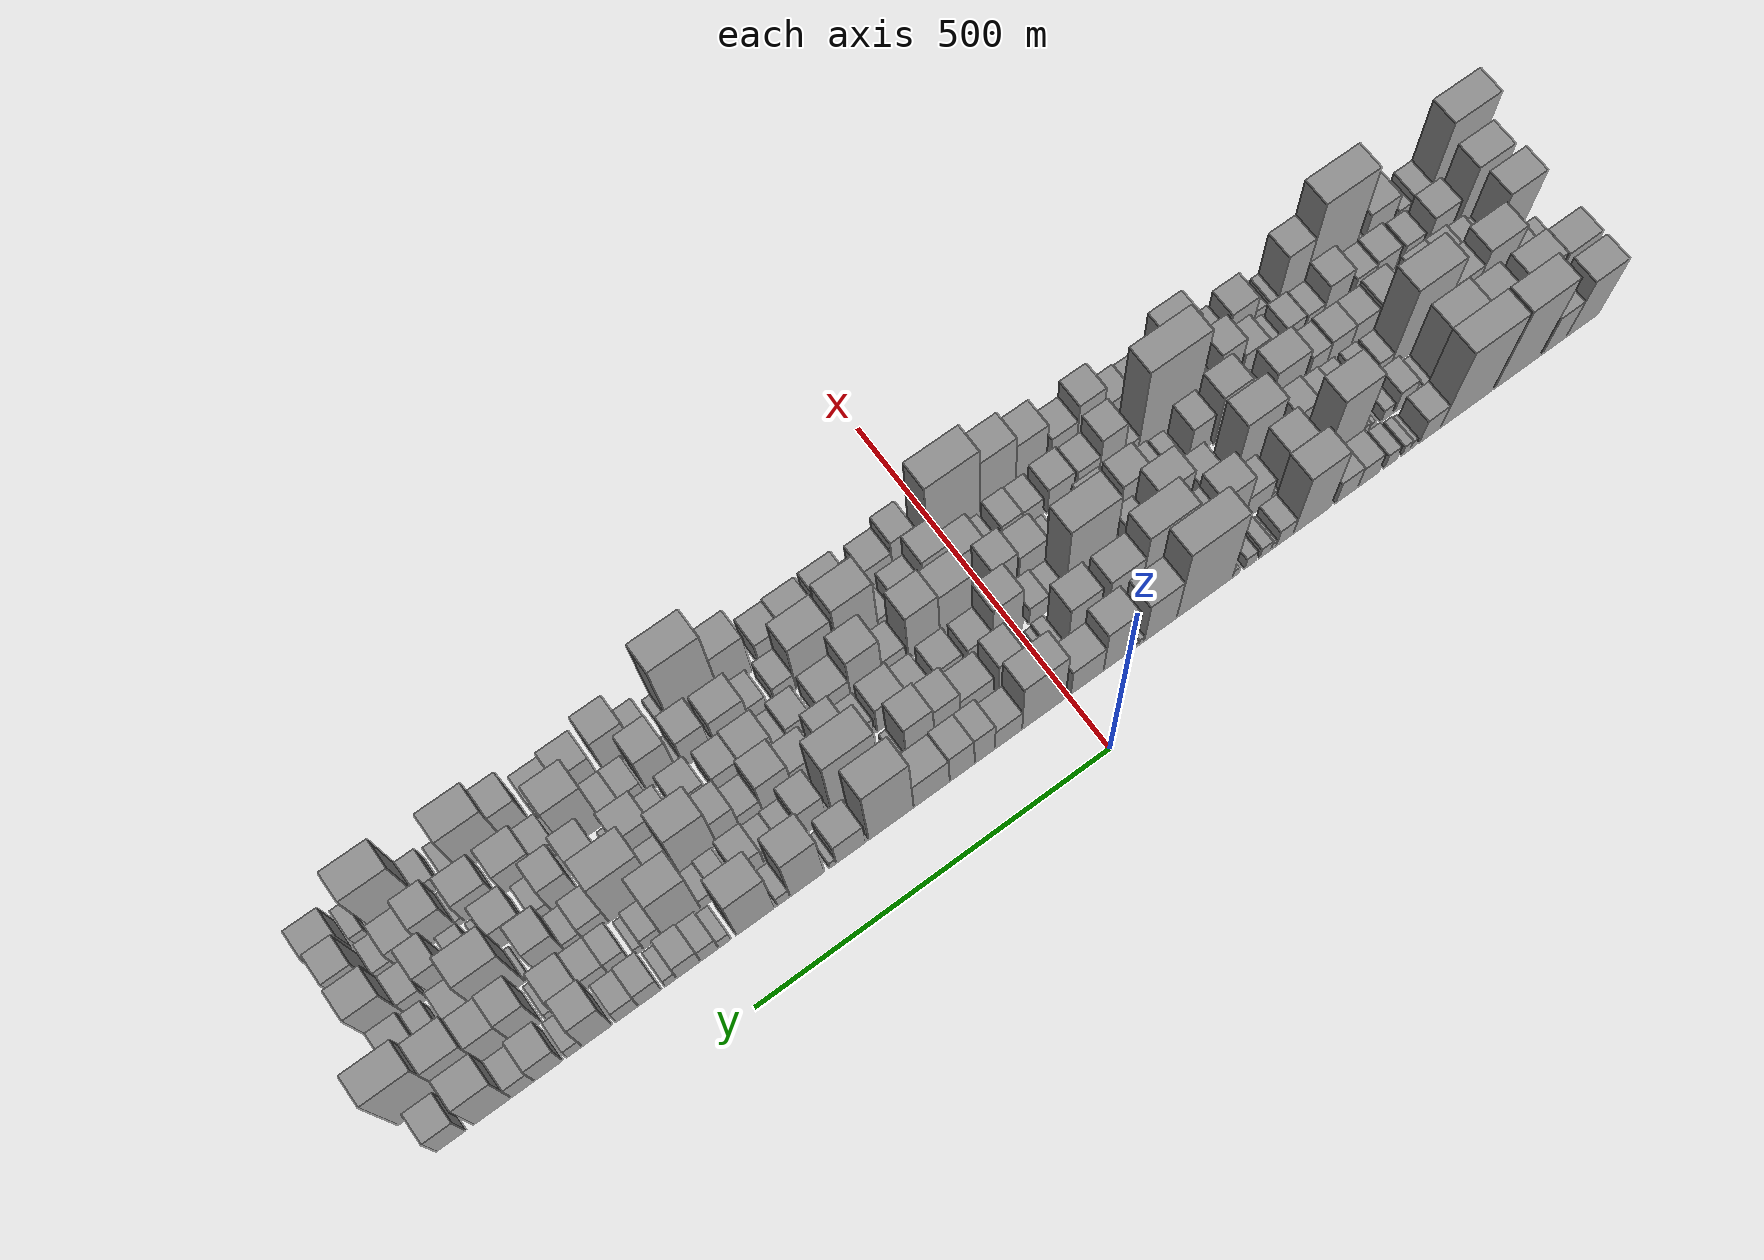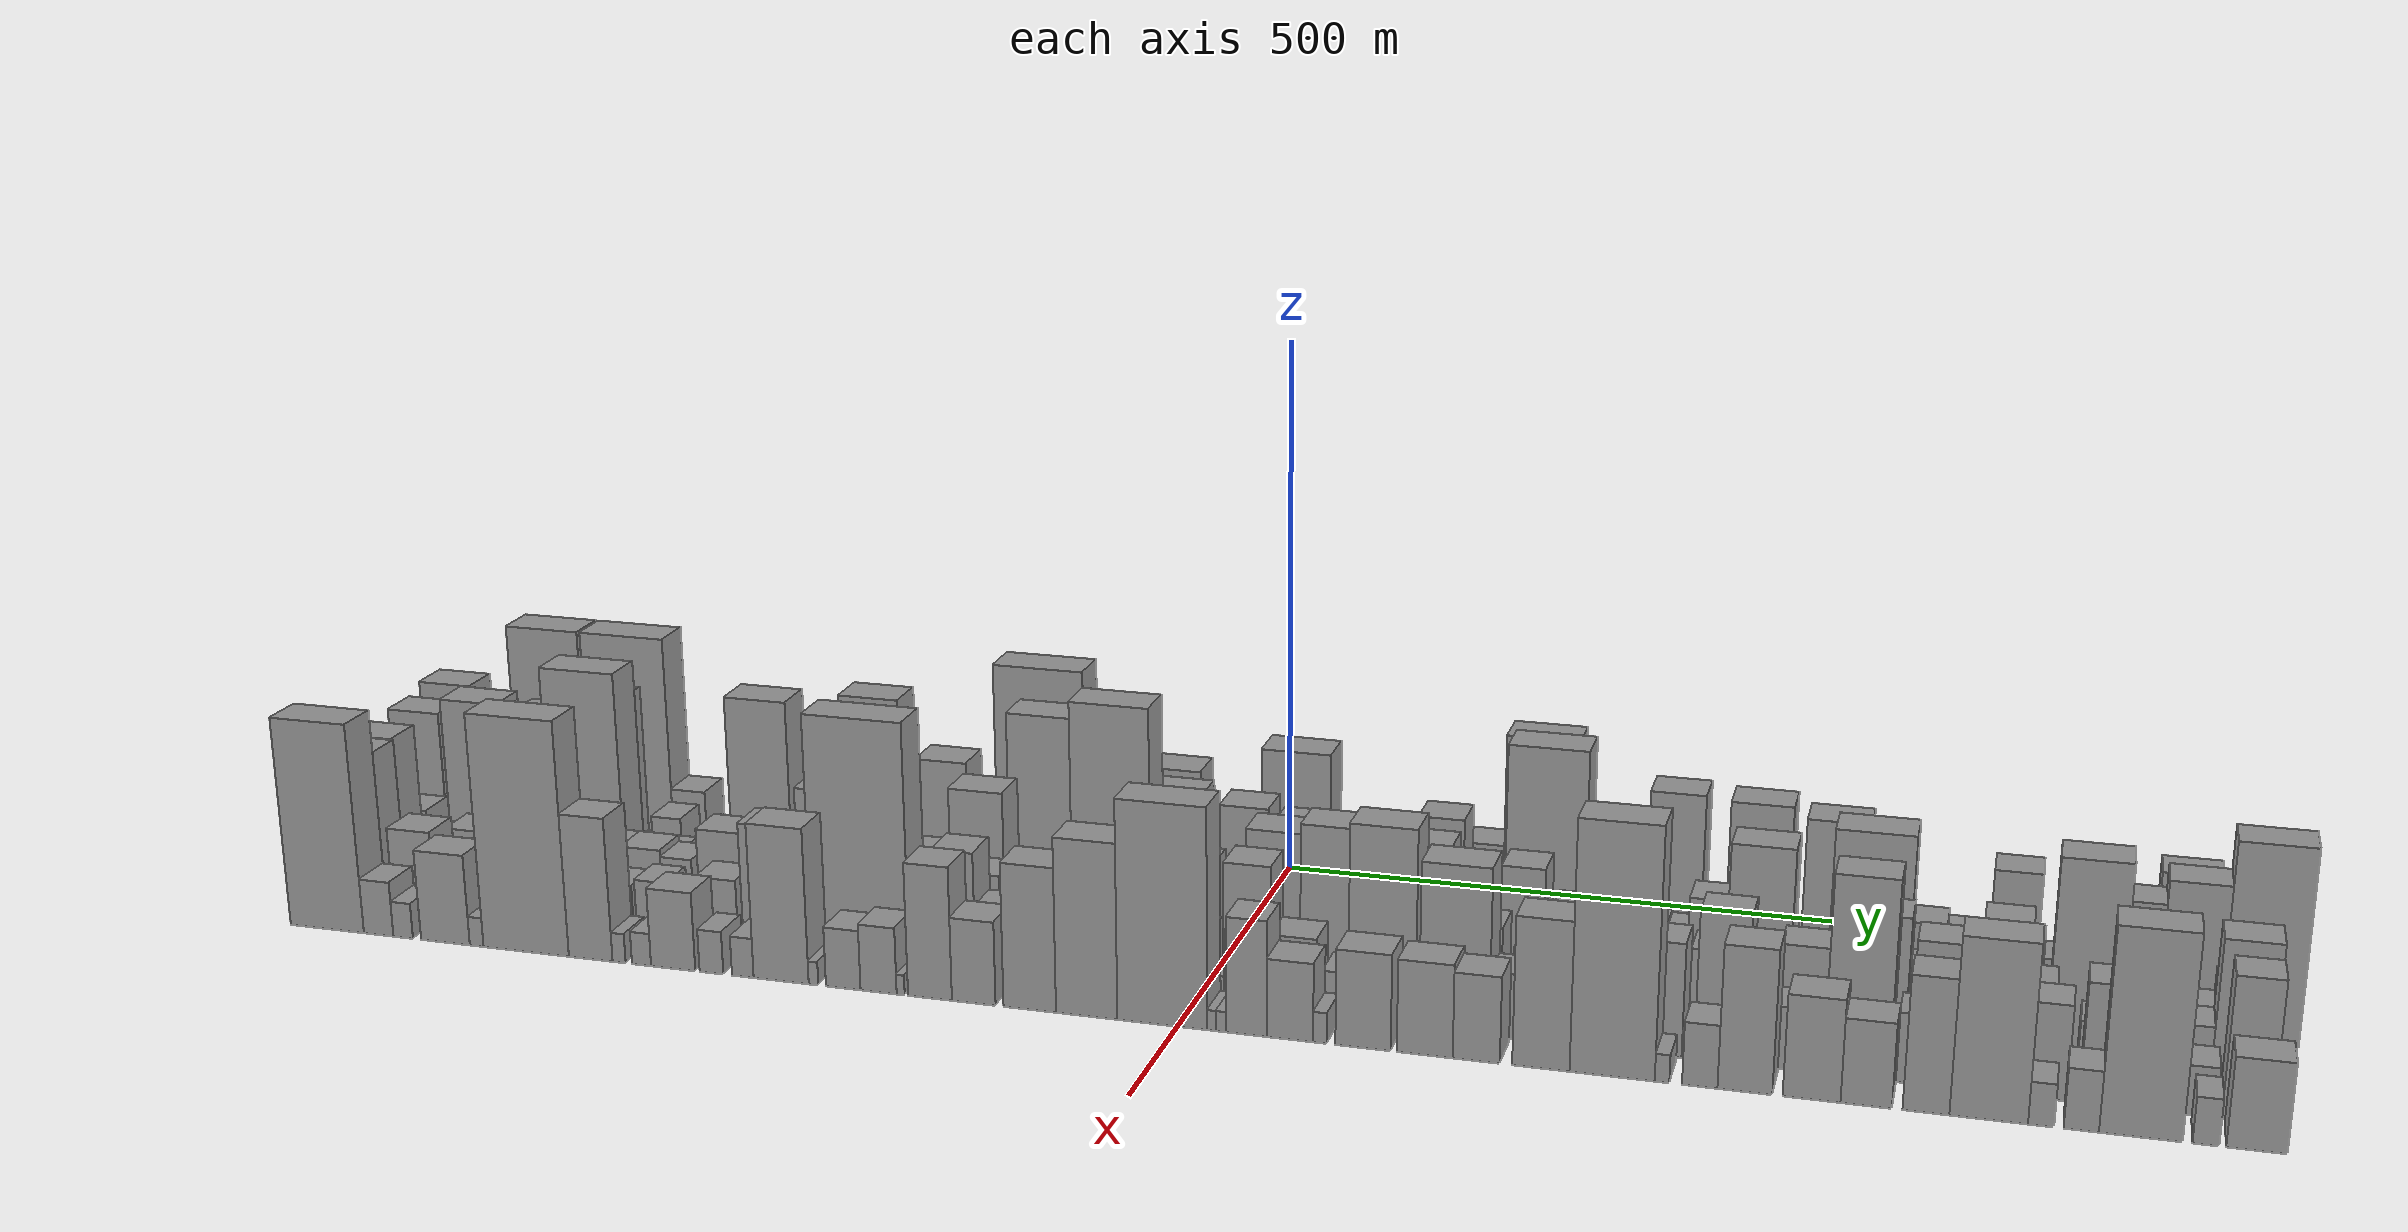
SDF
<sdf version="1.6">
 <world name="default">
  <scene>
   <sky><clouds><speed>12</speed></clouds></sky>
   <ambient>0.4 0.4 0.4 1</ambient>
   <background>0.7 0.7 0.7 1</background>
   <shadows>1</shadows>
  </scene>
  <gravity>0 0 -9.8066</gravity>
  <magnetic_field>6e-06 2.3e-05 -4.2e-05</magnetic_field>
  <physics default="0" name="default_physics" type="ode">
   <ode>
    <solver>
     <type>quick</type>
     <iters>10</iters>
     <sor>1.0</sor>
     <use_dynamic_moi_rescaling>0</use_dynamic_moi_rescaling>
    </solver>
    <constraints>
     <cfm>0</cfm>
     <erp>0.2</erp>
     <contact_max_correcting_vel>100</contact_max_correcting_vel>
     <contact_surface_layer>0.001</contact_surface_layer>
    </constraints>
   </ode>
   <max_step_size>0.004</max_step_size>
   <real_time_factor>1</real_time_factor>
   <real_time_update_rate>250</real_time_update_rate>
  </physics>
  <light name="sun" type="directional">
   <pose>0 0 10 0 0 0</pose>
   <diffuse>0.8 0.8 0.8 1</diffuse>
   <specular>0.2 0.2 0.2 1</specular>
   <attenuation>
    <range>1000</range>
    <constant>0.9</constant>
    <linear>0.01</linear>
    <quadratic>0.001</quadratic>
   </attenuation>
   <direction>-0.5 0.1 -0.9</direction>
  </light>
  <model name="building_1">
   <static>1</static>
   <pose>100.0000 -797.6599 0 0.000000 0.000000 0.000000</pose>
   <link name="link">
    <pose>0 0 75.00 0 0 0</pose>
    <collision name="collision"><geometry><box><size>40.0000 52.6803 150.0000</size></box></geometry></collision>
    <visual name="visual">
     <cast_shadows>0</cast_shadows>
     <geometry><box><size>40.0000 52.6803 150.0000</size></box></geometry>
     <material>
      <script>
       <uri>model://grey_wall/materials/scripts</uri>
       <uri>model://grey_wall/materials/textures</uri>
       <name>vrc/grey_wall</name>
      </script>
     </material>
    </visual>
   </link>
  </model>
  <model name="building_2">
   <static>1</static>
   <pose>100.0000 -752.0866 0 0.000000 0.000000 0.000000</pose>
   <link name="link">
    <pose>0 0 49.50 0 0 0</pose>
    <collision name="collision"><geometry><box><size>40.0000 38.4662 99.0000</size></box></geometry></collision>
    <visual name="visual">
     <cast_shadows>0</cast_shadows>
     <geometry><box><size>40.0000 38.4662 99.0000</size></box></geometry>
     <material>
      <script>
       <uri>model://grey_wall/materials/scripts</uri>
       <uri>model://grey_wall/materials/textures</uri>
       <name>vrc/grey_wall</name>
      </script>
     </material>
    </visual>
   </link>
  </model>
  <model name="building_3">
   <static>1</static>
   <pose>100.0000 -691.5177 0 0.000000 0.000000 0.000000</pose>
   <link name="link">
    <pose>0 0 106.50 0 0 0</pose>
    <collision name="collision"><geometry><box><size>40.0000 72.6717 213.0000</size></box></geometry></collision>
    <visual name="visual">
     <cast_shadows>0</cast_shadows>
     <geometry><box><size>40.0000 72.6717 213.0000</size></box></geometry>
     <material>
      <script>
       <uri>model://grey_wall/materials/scripts</uri>
       <uri>model://grey_wall/materials/textures</uri>
       <name>vrc/grey_wall</name>
      </script>
     </material>
    </visual>
   </link>
  </model>
  <model name="building_4">
   <static>1</static>
   <pose>100.0000 -610.3841 0 0.000000 0.000000 0.000000</pose>
   <link name="link">
    <pose>0 0 106.50 0 0 0</pose>
    <collision name="collision"><geometry><box><size>40.0000 83.5954 213.0000</size></box></geometry></collision>
    <visual name="visual">
     <cast_shadows>0</cast_shadows>
     <geometry><box><size>40.0000 83.5954 213.0000</size></box></geometry>
     <material>
      <script>
       <uri>model://grey_wall/materials/scripts</uri>
       <uri>model://grey_wall/materials/textures</uri>
       <name>vrc/grey_wall</name>
      </script>
     </material>
    </visual>
   </link>
  </model>
  <model name="building_5">
   <static>1</static>
   <pose>100.0000 -551.5495 0 0.000000 0.000000 0.000000</pose>
   <link name="link">
    <pose>0 0 33.00 0 0 0</pose>
    <collision name="collision"><geometry><box><size>40.0000 34.0738 66.0000</size></box></geometry></collision>
    <visual name="visual">
     <cast_shadows>0</cast_shadows>
     <geometry><box><size>40.0000 34.0738 66.0000</size></box></geometry>
     <material>
      <script>
       <uri>model://grey_wall/materials/scripts</uri>
       <uri>model://grey_wall/materials/textures</uri>
       <name>vrc/grey_wall</name>
      </script>
     </material>
    </visual>
   </link>
  </model>
  <model name="building_6">
   <static>1</static>
   <pose>100.0000 -525.0571 0 0.000000 0.000000 0.000000</pose>
   <link name="link">
    <pose>0 0 10.50 0 0 0</pose>
    <collision name="collision"><geometry><box><size>40.0000 8.9111 21.0000</size></box></geometry></collision>
    <visual name="visual">
     <cast_shadows>0</cast_shadows>
     <geometry><box><size>40.0000 8.9111 21.0000</size></box></geometry>
     <material>
      <script>
       <uri>model://grey_wall/materials/scripts</uri>
       <uri>model://grey_wall/materials/textures</uri>
       <name>vrc/grey_wall</name>
      </script>
     </material>
    </visual>
   </link>
  </model>
  <model name="building_7">
   <static>1</static>
   <pose>100.0000 -514.0190 0 0.000000 0.000000 0.000000</pose>
   <link name="link">
    <pose>0 0 13.50 0 0 0</pose>
    <collision name="collision"><geometry><box><size>40.0000 13.1650 27.0000</size></box></geometry></collision>
    <visual name="visual">
     <cast_shadows>0</cast_shadows>
     <geometry><box><size>40.0000 13.1650 27.0000</size></box></geometry>
     <material>
      <script>
       <uri>model://grey_wall/materials/scripts</uri>
       <uri>model://grey_wall/materials/textures</uri>
       <name>vrc/grey_wall</name>
      </script>
     </material>
    </visual>
   </link>
  </model>
  <model name="building_8">
   <static>1</static>
   <pose>100.0000 -489.5974 0 0.000000 0.000000 0.000000</pose>
   <link name="link">
    <pose>0 0 19.50 0 0 0</pose>
    <collision name="collision"><geometry><box><size>40.0000 19.6783 39.0000</size></box></geometry></collision>
    <visual name="visual">
     <cast_shadows>0</cast_shadows>
     <geometry><box><size>40.0000 19.6783 39.0000</size></box></geometry>
     <material>
      <script>
       <uri>model://grey_wall/materials/scripts</uri>
       <uri>model://grey_wall/materials/textures</uri>
       <name>vrc/grey_wall</name>
      </script>
     </material>
    </visual>
   </link>
  </model>
  <model name="building_9">
   <static>1</static>
   <pose>100.0000 -454.3965 0 0.000000 0.000000 0.000000</pose>
   <link name="link">
    <pose>0 0 28.50 0 0 0</pose>
    <collision name="collision"><geometry><box><size>40.0000 32.7235 57.0000</size></box></geometry></collision>
    <visual name="visual">
     <cast_shadows>0</cast_shadows>
     <geometry><box><size>40.0000 32.7235 57.0000</size></box></geometry>
     <material>
      <script>
       <uri>model://grey_wall/materials/scripts</uri>
       <uri>model://grey_wall/materials/textures</uri>
       <name>vrc/grey_wall</name>
      </script>
     </material>
    </visual>
   </link>
  </model>
  <model name="building_10">
   <static>1</static>
   <pose>100.0000 -420.7034 0 0.000000 0.000000 0.000000</pose>
   <link name="link">
    <pose>0 0 31.50 0 0 0</pose>
    <collision name="collision"><geometry><box><size>40.0000 34.6626 63.0000</size></box></geometry></collision>
    <visual name="visual">
     <cast_shadows>0</cast_shadows>
     <geometry><box><size>40.0000 34.6626 63.0000</size></box></geometry>
     <material>
      <script>
       <uri>model://grey_wall/materials/scripts</uri>
       <uri>model://grey_wall/materials/textures</uri>
       <name>vrc/grey_wall</name>
      </script>
     </material>
    </visual>
   </link>
  </model>
  <model name="building_11">
   <static>1</static>
   <pose>100.0000 -366.6551 0 0.000000 0.000000 0.000000</pose>
   <link name="link">
    <pose>0 0 87.00 0 0 0</pose>
    <collision name="collision"><geometry><box><size>40.0000 57.4342 174.0000</size></box></geometry></collision>
    <visual name="visual">
     <cast_shadows>0</cast_shadows>
     <geometry><box><size>40.0000 57.4342 174.0000</size></box></geometry>
     <material>
      <script>
       <uri>model://grey_wall/materials/scripts</uri>
       <uri>model://grey_wall/materials/textures</uri>
       <name>vrc/grey_wall</name>
      </script>
     </material>
    </visual>
   </link>
  </model>
  <model name="building_12">
   <static>1</static>
   <pose>100.0000 -324.9212 0 0.000000 0.000000 0.000000</pose>
   <link name="link">
    <pose>0 0 24.00 0 0 0</pose>
    <collision name="collision"><geometry><box><size>40.0000 26.0335 48.0000</size></box></geometry></collision>
    <visual name="visual">
     <cast_shadows>0</cast_shadows>
     <geometry><box><size>40.0000 26.0335 48.0000</size></box></geometry>
     <material>
      <script>
       <uri>model://grey_wall/materials/scripts</uri>
       <uri>model://grey_wall/materials/textures</uri>
       <name>vrc/grey_wall</name>
      </script>
     </material>
    </visual>
   </link>
  </model>
  <model name="building_13">
   <static>1</static>
   <pose>100.0000 -307.8725 0 0.000000 0.000000 0.000000</pose>
   <link name="link">
    <pose>0 0 9.00 0 0 0</pose>
    <collision name="collision"><geometry><box><size>40.0000 8.0638 18.0000</size></box></geometry></collision>
    <visual name="visual">
     <cast_shadows>0</cast_shadows>
     <geometry><box><size>40.0000 8.0638 18.0000</size></box></geometry>
     <material>
      <script>
       <uri>model://grey_wall/materials/scripts</uri>
       <uri>model://grey_wall/materials/textures</uri>
       <name>vrc/grey_wall</name>
      </script>
     </material>
    </visual>
   </link>
  </model>
  <model name="building_14">
   <static>1</static>
   <pose>100.0000 -295.1148 0 0.000000 0.000000 0.000000</pose>
   <link name="link">
    <pose>0 0 15.00 0 0 0</pose>
    <collision name="collision"><geometry><box><size>40.0000 17.4516 30.0000</size></box></geometry></collision>
    <visual name="visual">
     <cast_shadows>0</cast_shadows>
     <geometry><box><size>40.0000 17.4516 30.0000</size></box></geometry>
     <material>
      <script>
       <uri>model://grey_wall/materials/scripts</uri>
       <uri>model://grey_wall/materials/textures</uri>
       <name>vrc/grey_wall</name>
      </script>
     </material>
    </visual>
   </link>
  </model>
  <model name="building_15">
   <static>1</static>
   <pose>100.0000 -271.9981 0 0.000000 0.000000 0.000000</pose>
   <link name="link">
    <pose>0 0 16.50 0 0 0</pose>
    <collision name="collision"><geometry><box><size>40.0000 16.7818 33.0000</size></box></geometry></collision>
    <visual name="visual">
     <cast_shadows>0</cast_shadows>
     <geometry><box><size>40.0000 16.7818 33.0000</size></box></geometry>
     <material>
      <script>
       <uri>model://grey_wall/materials/scripts</uri>
       <uri>model://grey_wall/materials/textures</uri>
       <name>vrc/grey_wall</name>
      </script>
     </material>
    </visual>
   </link>
  </model>
  <model name="building_16">
   <static>1</static>
   <pose>100.0000 -249.7457 0 0.000000 0.000000 0.000000</pose>
   <link name="link">
    <pose>0 0 10.50 0 0 0</pose>
    <collision name="collision"><geometry><box><size>40.0000 9.7230 21.0000</size></box></geometry></collision>
    <visual name="visual">
     <cast_shadows>0</cast_shadows>
     <geometry><box><size>40.0000 9.7230 21.0000</size></box></geometry>
     <material>
      <script>
       <uri>model://grey_wall/materials/scripts</uri>
       <uri>model://grey_wall/materials/textures</uri>
       <name>vrc/grey_wall</name>
      </script>
     </material>
    </visual>
   </link>
  </model>
  <model name="building_17">
   <static>1</static>
   <pose>100.0000 -202.7161 0 0.000000 0.000000 0.000000</pose>
   <link name="link">
    <pose>0 0 108.00 0 0 0</pose>
    <collision name="collision"><geometry><box><size>40.0000 84.3361 216.0000</size></box></geometry></collision>
    <visual name="visual">
     <cast_shadows>0</cast_shadows>
     <geometry><box><size>40.0000 84.3361 216.0000</size></box></geometry>
     <material>
      <script>
       <uri>model://grey_wall/materials/scripts</uri>
       <uri>model://grey_wall/materials/textures</uri>
       <name>vrc/grey_wall</name>
      </script>
     </material>
    </visual>
   </link>
  </model>
  <model name="building_18">
   <static>1</static>
   <pose>100.0000 -136.1707 0 0.000000 0.000000 0.000000</pose>
   <link name="link">
    <pose>0 0 63.00 0 0 0</pose>
    <collision name="collision"><geometry><box><size>40.0000 48.7547 126.0000</size></box></geometry></collision>
    <visual name="visual">
     <cast_shadows>0</cast_shadows>
     <geometry><box><size>40.0000 48.7547 126.0000</size></box></geometry>
     <material>
      <script>
       <uri>model://grey_wall/materials/scripts</uri>
       <uri>model://grey_wall/materials/textures</uri>
       <name>vrc/grey_wall</name>
      </script>
     </material>
    </visual>
   </link>
  </model>
  <model name="building_19">
   <static>1</static>
   <pose>100.0000 -107.9350 0 0.000000 0.000000 0.000000</pose>
   <link name="link">
    <pose>0 0 9.00 0 0 0</pose>
    <collision name="collision"><geometry><box><size>40.0000 7.7166 18.0000</size></box></geometry></collision>
    <visual name="visual">
     <cast_shadows>0</cast_shadows>
     <geometry><box><size>40.0000 7.7166 18.0000</size></box></geometry>
     <material>
      <script>
       <uri>model://grey_wall/materials/scripts</uri>
       <uri>model://grey_wall/materials/textures</uri>
       <name>vrc/grey_wall</name>
      </script>
     </material>
    </visual>
   </link>
  </model>
  <model name="building_20">
   <static>1</static>
   <pose>100.0000 -101.0726 0 0.000000 0.000000 0.000000</pose>
   <link name="link">
    <pose>0 0 7.50 0 0 0</pose>
    <collision name="collision"><geometry><box><size>40.0000 6.0082 15.0000</size></box></geometry></collision>
    <visual name="visual">
     <cast_shadows>0</cast_shadows>
     <geometry><box><size>40.0000 6.0082 15.0000</size></box></geometry>
     <material>
      <script>
       <uri>model://grey_wall/materials/scripts</uri>
       <uri>model://grey_wall/materials/textures</uri>
       <name>vrc/grey_wall</name>
      </script>
     </material>
    </visual>
   </link>
  </model>
  <model name="building_21">
   <static>1</static>
   <pose>100.0000 -74.8214 0 0.000000 0.000000 0.000000</pose>
   <link name="link">
    <pose>0 0 66.00 0 0 0</pose>
    <collision name="collision"><geometry><box><size>40.0000 46.4943 132.0000</size></box></geometry></collision>
    <visual name="visual">
     <cast_shadows>0</cast_shadows>
     <geometry><box><size>40.0000 46.4943 132.0000</size></box></geometry>
     <material>
      <script>
       <uri>model://grey_wall/materials/scripts</uri>
       <uri>model://grey_wall/materials/textures</uri>
       <name>vrc/grey_wall</name>
      </script>
     </material>
    </visual>
   </link>
  </model>
  <model name="building_22">
   <static>1</static>
   <pose>100.0000 -27.4610 0 0.000000 0.000000 0.000000</pose>
   <link name="link">
    <pose>0 0 42.00 0 0 0</pose>
    <collision name="collision"><geometry><box><size>40.0000 48.2265 84.0000</size></box></geometry></collision>
    <visual name="visual">
     <cast_shadows>0</cast_shadows>
     <geometry><box><size>40.0000 48.2265 84.0000</size></box></geometry>
     <material>
      <script>
       <uri>model://grey_wall/materials/scripts</uri>
       <uri>model://grey_wall/materials/textures</uri>
       <name>vrc/grey_wall</name>
      </script>
     </material>
    </visual>
   </link>
  </model>
  <model name="building_23">
   <static>1</static>
   <pose>100.0000 36.1751 0 0.000000 0.000000 0.000000</pose>
   <link name="link">
    <pose>0 0 79.50 0 0 0</pose>
    <collision name="collision"><geometry><box><size>40.0000 63.0457 159.0000</size></box></geometry></collision>
    <visual name="visual">
     <cast_shadows>0</cast_shadows>
     <geometry><box><size>40.0000 63.0457 159.0000</size></box></geometry>
     <material>
      <script>
       <uri>model://grey_wall/materials/scripts</uri>
       <uri>model://grey_wall/materials/textures</uri>
       <name>vrc/grey_wall</name>
      </script>
     </material>
    </visual>
   </link>
  </model>
  <model name="building_24">
   <static>1</static>
   <pose>100.0000 87.2624 0 0.000000 0.000000 0.000000</pose>
   <link name="link">
    <pose>0 0 34.50 0 0 0</pose>
    <collision name="collision"><geometry><box><size>40.0000 39.1290 69.0000</size></box></geometry></collision>
    <visual name="visual">
     <cast_shadows>0</cast_shadows>
     <geometry><box><size>40.0000 39.1290 69.0000</size></box></geometry>
     <material>
      <script>
       <uri>model://grey_wall/materials/scripts</uri>
       <uri>model://grey_wall/materials/textures</uri>
       <name>vrc/grey_wall</name>
      </script>
     </material>
    </visual>
   </link>
  </model>
  <model name="building_25">
   <static>1</static>
   <pose>100.0000 121.6511 0 0.000000 0.000000 0.000000</pose>
   <link name="link">
    <pose>0 0 48.00 0 0 0</pose>
    <collision name="collision"><geometry><box><size>40.0000 29.6482 96.0000</size></box></geometry></collision>
    <visual name="visual">
     <cast_shadows>0</cast_shadows>
     <geometry><box><size>40.0000 29.6482 96.0000</size></box></geometry>
     <material>
      <script>
       <uri>model://grey_wall/materials/scripts</uri>
       <uri>model://grey_wall/materials/textures</uri>
       <name>vrc/grey_wall</name>
      </script>
     </material>
    </visual>
   </link>
  </model>
  <model name="building_26">
   <static>1</static>
   <pose>100.0000 154.2542 0 0.000000 0.000000 0.000000</pose>
   <link name="link">
    <pose>0 0 48.00 0 0 0</pose>
    <collision name="collision"><geometry><box><size>40.0000 35.5580 96.0000</size></box></geometry></collision>
    <visual name="visual">
     <cast_shadows>0</cast_shadows>
     <geometry><box><size>40.0000 35.5580 96.0000</size></box></geometry>
     <material>
      <script>
       <uri>model://grey_wall/materials/scripts</uri>
       <uri>model://grey_wall/materials/textures</uri>
       <name>vrc/grey_wall</name>
      </script>
     </material>
    </visual>
   </link>
  </model>
  <model name="building_27">
   <static>1</static>
   <pose>100.0000 197.6740 0 0.000000 0.000000 0.000000</pose>
   <link name="link">
    <pose>0 0 45.00 0 0 0</pose>
    <collision name="collision"><geometry><box><size>40.0000 51.2816 90.0000</size></box></geometry></collision>
    <visual name="visual">
     <cast_shadows>0</cast_shadows>
     <geometry><box><size>40.0000 51.2816 90.0000</size></box></geometry>
     <material>
      <script>
       <uri>model://grey_wall/materials/scripts</uri>
       <uri>model://grey_wall/materials/textures</uri>
       <name>vrc/grey_wall</name>
      </script>
     </material>
    </visual>
   </link>
  </model>
  <model name="building_28">
   <static>1</static>
   <pose>100.0000 255.1287 0 0.000000 0.000000 0.000000</pose>
   <link name="link">
    <pose>0 0 96.00 0 0 0</pose>
    <collision name="collision"><geometry><box><size>40.0000 63.6278 192.0000</size></box></geometry></collision>
    <visual name="visual">
     <cast_shadows>0</cast_shadows>
     <geometry><box><size>40.0000 63.6278 192.0000</size></box></geometry>
     <material>
      <script>
       <uri>model://grey_wall/materials/scripts</uri>
       <uri>model://grey_wall/materials/textures</uri>
       <name>vrc/grey_wall</name>
      </script>
     </material>
    </visual>
   </link>
  </model>
  <model name="building_29">
   <static>1</static>
   <pose>100.0000 311.7444 0 0.000000 0.000000 0.000000</pose>
   <link name="link">
    <pose>0 0 37.50 0 0 0</pose>
    <collision name="collision"><geometry><box><size>40.0000 41.6035 75.0000</size></box></geometry></collision>
    <visual name="visual">
     <cast_shadows>0</cast_shadows>
     <geometry><box><size>40.0000 41.6035 75.0000</size></box></geometry>
     <material>
      <script>
       <uri>model://grey_wall/materials/scripts</uri>
       <uri>model://grey_wall/materials/textures</uri>
       <name>vrc/grey_wall</name>
      </script>
     </material>
    </visual>
   </link>
  </model>
  <model name="building_30">
   <static>1</static>
   <pose>100.0000 337.1644 0 0.000000 0.000000 0.000000</pose>
   <link name="link">
    <pose>0 0 10.50 0 0 0</pose>
    <collision name="collision"><geometry><box><size>40.0000 9.2365 21.0000</size></box></geometry></collision>
    <visual name="visual">
     <cast_shadows>0</cast_shadows>
     <geometry><box><size>40.0000 9.2365 21.0000</size></box></geometry>
     <material>
      <script>
       <uri>model://grey_wall/materials/scripts</uri>
       <uri>model://grey_wall/materials/textures</uri>
       <name>vrc/grey_wall</name>
      </script>
     </material>
    </visual>
   </link>
  </model>
  <model name="building_31">
   <static>1</static>
   <pose>100.0000 372.6004 0 0.000000 0.000000 0.000000</pose>
   <link name="link">
    <pose>0 0 76.50 0 0 0</pose>
    <collision name="collision"><geometry><box><size>40.0000 47.6355 153.0000</size></box></geometry></collision>
    <visual name="visual">
     <cast_shadows>0</cast_shadows>
     <geometry><box><size>40.0000 47.6355 153.0000</size></box></geometry>
     <material>
      <script>
       <uri>model://grey_wall/materials/scripts</uri>
       <uri>model://grey_wall/materials/textures</uri>
       <name>vrc/grey_wall</name>
      </script>
     </material>
    </visual>
   </link>
  </model>
  <model name="building_32">
   <static>1</static>
   <pose>100.0000 405.4133 0 0.000000 0.000000 0.000000</pose>
   <link name="link">
    <pose>0 0 16.50 0 0 0</pose>
    <collision name="collision"><geometry><box><size>40.0000 17.9903 33.0000</size></box></geometry></collision>
    <visual name="visual">
     <cast_shadows>0</cast_shadows>
     <geometry><box><size>40.0000 17.9903 33.0000</size></box></geometry>
     <material>
      <script>
       <uri>model://grey_wall/materials/scripts</uri>
       <uri>model://grey_wall/materials/textures</uri>
       <name>vrc/grey_wall</name>
      </script>
     </material>
    </visual>
   </link>
  </model>
  <model name="building_33">
   <static>1</static>
   <pose>100.0000 444.0145 0 0.000000 0.000000 0.000000</pose>
   <link name="link">
    <pose>0 0 75.00 0 0 0</pose>
    <collision name="collision"><geometry><box><size>40.0000 53.2121 150.0000</size></box></geometry></collision>
    <visual name="visual">
     <cast_shadows>0</cast_shadows>
     <geometry><box><size>40.0000 53.2121 150.0000</size></box></geometry>
     <material>
      <script>
       <uri>model://grey_wall/materials/scripts</uri>
       <uri>model://grey_wall/materials/textures</uri>
       <name>vrc/grey_wall</name>
      </script>
     </material>
    </visual>
   </link>
  </model>
  <model name="building_34">
   <static>1</static>
   <pose>100.0000 486.1541 0 0.000000 0.000000 0.000000</pose>
   <link name="link">
    <pose>0 0 16.50 0 0 0</pose>
    <collision name="collision"><geometry><box><size>40.0000 17.0671 33.0000</size></box></geometry></collision>
    <visual name="visual">
     <cast_shadows>0</cast_shadows>
     <geometry><box><size>40.0000 17.0671 33.0000</size></box></geometry>
     <material>
      <script>
       <uri>model://grey_wall/materials/scripts</uri>
       <uri>model://grey_wall/materials/textures</uri>
       <name>vrc/grey_wall</name>
      </script>
     </material>
    </visual>
   </link>
  </model>
  <model name="building_35">
   <static>1</static>
   <pose>100.0000 506.9671 0 0.000000 0.000000 0.000000</pose>
   <link name="link">
    <pose>0 0 24.00 0 0 0</pose>
    <collision name="collision"><geometry><box><size>40.0000 24.5587 48.0000</size></box></geometry></collision>
    <visual name="visual">
     <cast_shadows>0</cast_shadows>
     <geometry><box><size>40.0000 24.5587 48.0000</size></box></geometry>
     <material>
      <script>
       <uri>model://grey_wall/materials/scripts</uri>
       <uri>model://grey_wall/materials/textures</uri>
       <name>vrc/grey_wall</name>
      </script>
     </material>
    </visual>
   </link>
  </model>
  <model name="building_36">
   <static>1</static>
   <pose>100.0000 535.3519 0 0.000000 0.000000 0.000000</pose>
   <link name="link">
    <pose>0 0 27.00 0 0 0</pose>
    <collision name="collision"><geometry><box><size>40.0000 32.2110 54.0000</size></box></geometry></collision>
    <visual name="visual">
     <cast_shadows>0</cast_shadows>
     <geometry><box><size>40.0000 32.2110 54.0000</size></box></geometry>
     <material>
      <script>
       <uri>model://grey_wall/materials/scripts</uri>
       <uri>model://grey_wall/materials/textures</uri>
       <name>vrc/grey_wall</name>
      </script>
     </material>
    </visual>
   </link>
  </model>
  <model name="building_37">
   <static>1</static>
   <pose>100.0000 559.2632 0 0.000000 0.000000 0.000000</pose>
   <link name="link">
    <pose>0 0 15.00 0 0 0</pose>
    <collision name="collision"><geometry><box><size>40.0000 15.6117 30.0000</size></box></geometry></collision>
    <visual name="visual">
     <cast_shadows>0</cast_shadows>
     <geometry><box><size>40.0000 15.6117 30.0000</size></box></geometry>
     <material>
      <script>
       <uri>model://grey_wall/materials/scripts</uri>
       <uri>model://grey_wall/materials/textures</uri>
       <name>vrc/grey_wall</name>
      </script>
     </material>
    </visual>
   </link>
  </model>
  <model name="building_38">
   <static>1</static>
   <pose>100.0000 587.5216 0 0.000000 0.000000 0.000000</pose>
   <link name="link">
    <pose>0 0 28.50 0 0 0</pose>
    <collision name="collision"><geometry><box><size>40.0000 30.9050 57.0000</size></box></geometry></collision>
    <visual name="visual">
     <cast_shadows>0</cast_shadows>
     <geometry><box><size>40.0000 30.9050 57.0000</size></box></geometry>
     <material>
      <script>
       <uri>model://grey_wall/materials/scripts</uri>
       <uri>model://grey_wall/materials/textures</uri>
       <name>vrc/grey_wall</name>
      </script>
     </material>
    </visual>
   </link>
  </model>
  <model name="building_39">
   <static>1</static>
   <pose>100.0000 618.0033 0 0.000000 0.000000 0.000000</pose>
   <link name="link">
    <pose>0 0 25.50 0 0 0</pose>
    <collision name="collision"><geometry><box><size>40.0000 30.0585 51.0000</size></box></geometry></collision>
    <visual name="visual">
     <cast_shadows>0</cast_shadows>
     <geometry><box><size>40.0000 30.0585 51.0000</size></box></geometry>
     <material>
      <script>
       <uri>model://grey_wall/materials/scripts</uri>
       <uri>model://grey_wall/materials/textures</uri>
       <name>vrc/grey_wall</name>
      </script>
     </material>
    </visual>
   </link>
  </model>
  <model name="building_40">
   <static>1</static>
   <pose>100.0000 657.9605 0 0.000000 0.000000 0.000000</pose>
   <link name="link">
    <pose>0 0 55.50 0 0 0</pose>
    <collision name="collision"><geometry><box><size>40.0000 39.8559 111.0000</size></box></geometry></collision>
    <visual name="visual">
     <cast_shadows>0</cast_shadows>
     <geometry><box><size>40.0000 39.8559 111.0000</size></box></geometry>
     <material>
      <script>
       <uri>model://grey_wall/materials/scripts</uri>
       <uri>model://grey_wall/materials/textures</uri>
       <name>vrc/grey_wall</name>
      </script>
     </material>
    </visual>
   </link>
  </model>
  <model name="building_41">
   <static>1</static>
   <pose>100.0000 688.1823 0 0.000000 0.000000 0.000000</pose>
   <link name="link">
    <pose>0 0 18.00 0 0 0</pose>
    <collision name="collision"><geometry><box><size>40.0000 20.5877 36.0000</size></box></geometry></collision>
    <visual name="visual">
     <cast_shadows>0</cast_shadows>
     <geometry><box><size>40.0000 20.5877 36.0000</size></box></geometry>
     <material>
      <script>
       <uri>model://grey_wall/materials/scripts</uri>
       <uri>model://grey_wall/materials/textures</uri>
       <name>vrc/grey_wall</name>
      </script>
     </material>
    </visual>
   </link>
  </model>
  <model name="building_42">
   <static>1</static>
   <pose>100.0000 722.3112 0 0.000000 0.000000 0.000000</pose>
   <link name="link">
    <pose>0 0 36.00 0 0 0</pose>
    <collision name="collision"><geometry><box><size>40.0000 37.6702 72.0000</size></box></geometry></collision>
    <visual name="visual">
     <cast_shadows>0</cast_shadows>
     <geometry><box><size>40.0000 37.6702 72.0000</size></box></geometry>
     <material>
      <script>
       <uri>model://grey_wall/materials/scripts</uri>
       <uri>model://grey_wall/materials/textures</uri>
       <name>vrc/grey_wall</name>
      </script>
     </material>
    </visual>
   </link>
  </model>
  <model name="building_43">
   <static>1</static>
   <pose>100.0000 756.2850 0 0.000000 0.000000 0.000000</pose>
   <link name="link">
    <pose>0 0 27.00 0 0 0</pose>
    <collision name="collision"><geometry><box><size>40.0000 30.2773 54.0000</size></box></geometry></collision>
    <visual name="visual">
     <cast_shadows>0</cast_shadows>
     <geometry><box><size>40.0000 30.2773 54.0000</size></box></geometry>
     <material>
      <script>
       <uri>model://grey_wall/materials/scripts</uri>
       <uri>model://grey_wall/materials/textures</uri>
       <name>vrc/grey_wall</name>
      </script>
     </material>
    </visual>
   </link>
  </model>
  <model name="building_44">
   <static>1</static>
   <pose>100.0000 795.8376 0 0.000000 0.000000 0.000000</pose>
   <link name="link">
    <pose>0 0 61.50 0 0 0</pose>
    <collision name="collision"><geometry><box><size>40.0000 48.8279 123.0000</size></box></geometry></collision>
    <visual name="visual">
     <cast_shadows>0</cast_shadows>
     <geometry><box><size>40.0000 48.8279 123.0000</size></box></geometry>
     <material>
      <script>
       <uri>model://grey_wall/materials/scripts</uri>
       <uri>model://grey_wall/materials/textures</uri>
       <name>vrc/grey_wall</name>
      </script>
     </material>
    </visual>
   </link>
  </model>
  <model name="building_45">
   <static>1</static>
   <pose>100.0000 849.3882 0 0.000000 0.000000 0.000000</pose>
   <link name="link">
    <pose>0 0 37.50 0 0 0</pose>
    <collision name="collision"><geometry><box><size>40.0000 38.2733 75.0000</size></box></geometry></collision>
    <visual name="visual">
     <cast_shadows>0</cast_shadows>
     <geometry><box><size>40.0000 38.2733 75.0000</size></box></geometry>
     <material>
      <script>
       <uri>model://grey_wall/materials/scripts</uri>
       <uri>model://grey_wall/materials/textures</uri>
       <name>vrc/grey_wall</name>
      </script>
     </material>
    </visual>
   </link>
  </model>
  <model name="building_46">
   <static>1</static>
   <pose>149.0000 -803.9042 0 0.000000 0.000000 0.000000</pose>
   <link name="link">
    <pose>0 0 69.00 0 0 0</pose>
    <collision name="collision"><geometry><box><size>40.0000 52.1916 138.0000</size></box></geometry></collision>
    <visual name="visual">
     <cast_shadows>0</cast_shadows>
     <geometry><box><size>40.0000 52.1916 138.0000</size></box></geometry>
     <material>
      <script>
       <uri>model://grey_wall/materials/scripts</uri>
       <uri>model://grey_wall/materials/textures</uri>
       <name>vrc/grey_wall</name>
      </script>
     </material>
    </visual>
   </link>
  </model>
  <model name="building_47">
   <static>1</static>
   <pose>149.0000 -744.8773 0 0.000000 0.000000 0.000000</pose>
   <link name="link">
    <pose>0 0 73.50 0 0 0</pose>
    <collision name="collision"><geometry><box><size>40.0000 55.8622 147.0000</size></box></geometry></collision>
    <visual name="visual">
     <cast_shadows>0</cast_shadows>
     <geometry><box><size>40.0000 55.8622 147.0000</size></box></geometry>
     <material>
      <script>
       <uri>model://grey_wall/materials/scripts</uri>
       <uri>model://grey_wall/materials/textures</uri>
       <name>vrc/grey_wall</name>
      </script>
     </material>
    </visual>
   </link>
  </model>
  <model name="building_48">
   <static>1</static>
   <pose>149.0000 -708.6220 0 0.000000 0.000000 0.000000</pose>
   <link name="link">
    <pose>0 0 15.00 0 0 0</pose>
    <collision name="collision"><geometry><box><size>40.0000 16.6484 30.0000</size></box></geometry></collision>
    <visual name="visual">
     <cast_shadows>0</cast_shadows>
     <geometry><box><size>40.0000 16.6484 30.0000</size></box></geometry>
     <material>
      <script>
       <uri>model://grey_wall/materials/scripts</uri>
       <uri>model://grey_wall/materials/textures</uri>
       <name>vrc/grey_wall</name>
      </script>
     </material>
    </visual>
   </link>
  </model>
  <model name="building_49">
   <static>1</static>
   <pose>149.0000 -674.1054 0 0.000000 0.000000 0.000000</pose>
   <link name="link">
    <pose>0 0 73.50 0 0 0</pose>
    <collision name="collision"><geometry><box><size>40.0000 52.3848 147.0000</size></box></geometry></collision>
    <visual name="visual">
     <cast_shadows>0</cast_shadows>
     <geometry><box><size>40.0000 52.3848 147.0000</size></box></geometry>
     <material>
      <script>
       <uri>model://grey_wall/materials/scripts</uri>
       <uri>model://grey_wall/materials/textures</uri>
       <name>vrc/grey_wall</name>
      </script>
     </material>
    </visual>
   </link>
  </model>
  <model name="building_50">
   <static>1</static>
   <pose>149.0000 -618.6247 0 0.000000 0.000000 0.000000</pose>
   <link name="link">
    <pose>0 0 84.00 0 0 0</pose>
    <collision name="collision"><geometry><box><size>40.0000 58.5766 168.0000</size></box></geometry></collision>
    <visual name="visual">
     <cast_shadows>0</cast_shadows>
     <geometry><box><size>40.0000 58.5766 168.0000</size></box></geometry>
     <material>
      <script>
       <uri>model://grey_wall/materials/scripts</uri>
       <uri>model://grey_wall/materials/textures</uri>
       <name>vrc/grey_wall</name>
      </script>
     </material>
    </visual>
   </link>
  </model>
  <model name="building_51">
   <static>1</static>
   <pose>149.0000 -583.2388 0 0.000000 0.000000 0.000000</pose>
   <link name="link">
    <pose>0 0 13.50 0 0 0</pose>
    <collision name="collision"><geometry><box><size>40.0000 12.1953 27.0000</size></box></geometry></collision>
    <visual name="visual">
     <cast_shadows>0</cast_shadows>
     <geometry><box><size>40.0000 12.1953 27.0000</size></box></geometry>
     <material>
      <script>
       <uri>model://grey_wall/materials/scripts</uri>
       <uri>model://grey_wall/materials/textures</uri>
       <name>vrc/grey_wall</name>
      </script>
     </material>
    </visual>
   </link>
  </model>
  <model name="building_52">
   <static>1</static>
   <pose>149.0000 -571.4134 0 0.000000 0.000000 0.000000</pose>
   <link name="link">
    <pose>0 0 12.00 0 0 0</pose>
    <collision name="collision"><geometry><box><size>40.0000 11.4554 24.0000</size></box></geometry></collision>
    <visual name="visual">
     <cast_shadows>0</cast_shadows>
     <geometry><box><size>40.0000 11.4554 24.0000</size></box></geometry>
     <material>
      <script>
       <uri>model://grey_wall/materials/scripts</uri>
       <uri>model://grey_wall/materials/textures</uri>
       <name>vrc/grey_wall</name>
      </script>
     </material>
    </visual>
   </link>
  </model>
  <model name="building_53">
   <static>1</static>
   <pose>149.0000 -551.0473 0 0.000000 0.000000 0.000000</pose>
   <link name="link">
    <pose>0 0 28.50 0 0 0</pose>
    <collision name="collision"><geometry><box><size>40.0000 29.2768 57.0000</size></box></geometry></collision>
    <visual name="visual">
     <cast_shadows>0</cast_shadows>
     <geometry><box><size>40.0000 29.2768 57.0000</size></box></geometry>
     <material>
      <script>
       <uri>model://grey_wall/materials/scripts</uri>
       <uri>model://grey_wall/materials/textures</uri>
       <name>vrc/grey_wall</name>
      </script>
     </material>
    </visual>
   </link>
  </model>
  <model name="building_54">
   <static>1</static>
   <pose>149.0000 -523.7265 0 0.000000 0.000000 0.000000</pose>
   <link name="link">
    <pose>0 0 16.50 0 0 0</pose>
    <collision name="collision"><geometry><box><size>40.0000 17.3649 33.0000</size></box></geometry></collision>
    <visual name="visual">
     <cast_shadows>0</cast_shadows>
     <geometry><box><size>40.0000 17.3649 33.0000</size></box></geometry>
     <material>
      <script>
       <uri>model://grey_wall/materials/scripts</uri>
       <uri>model://grey_wall/materials/textures</uri>
       <name>vrc/grey_wall</name>
      </script>
     </material>
    </visual>
   </link>
  </model>
  <model name="building_55">
   <static>1</static>
   <pose>149.0000 -500.5472 0 0.000000 0.000000 0.000000</pose>
   <link name="link">
    <pose>0 0 9.00 0 0 0</pose>
    <collision name="collision"><geometry><box><size>40.0000 8.9937 18.0000</size></box></geometry></collision>
    <visual name="visual">
     <cast_shadows>0</cast_shadows>
     <geometry><box><size>40.0000 8.9937 18.0000</size></box></geometry>
     <material>
      <script>
       <uri>model://grey_wall/materials/scripts</uri>
       <uri>model://grey_wall/materials/textures</uri>
       <name>vrc/grey_wall</name>
      </script>
     </material>
    </visual>
   </link>
  </model>
  <model name="building_56">
   <static>1</static>
   <pose>149.0000 -491.0461 0 0.000000 0.000000 0.000000</pose>
   <link name="link">
    <pose>0 0 12.00 0 0 0</pose>
    <collision name="collision"><geometry><box><size>40.0000 10.0085 24.0000</size></box></geometry></collision>
    <visual name="visual">
     <cast_shadows>0</cast_shadows>
     <geometry><box><size>40.0000 10.0085 24.0000</size></box></geometry>
     <material>
      <script>
       <uri>model://grey_wall/materials/scripts</uri>
       <uri>model://grey_wall/materials/textures</uri>
       <name>vrc/grey_wall</name>
      </script>
     </material>
    </visual>
   </link>
  </model>
  <model name="building_57">
   <static>1</static>
   <pose>149.0000 -456.3584 0 0.000000 0.000000 0.000000</pose>
   <link name="link">
    <pose>0 0 90.00 0 0 0</pose>
    <collision name="collision"><geometry><box><size>40.0000 59.3669 180.0000</size></box></geometry></collision>
    <visual name="visual">
     <cast_shadows>0</cast_shadows>
     <geometry><box><size>40.0000 59.3669 180.0000</size></box></geometry>
     <material>
      <script>
       <uri>model://grey_wall/materials/scripts</uri>
       <uri>model://grey_wall/materials/textures</uri>
       <name>vrc/grey_wall</name>
      </script>
     </material>
    </visual>
   </link>
  </model>
  <model name="building_58">
   <static>1</static>
   <pose>149.0000 -422.5458 0 0.000000 0.000000 0.000000</pose>
   <link name="link">
    <pose>0 0 9.00 0 0 0</pose>
    <collision name="collision"><geometry><box><size>40.0000 8.2582 18.0000</size></box></geometry></collision>
    <visual name="visual">
     <cast_shadows>0</cast_shadows>
     <geometry><box><size>40.0000 8.2582 18.0000</size></box></geometry>
     <material>
      <script>
       <uri>model://grey_wall/materials/scripts</uri>
       <uri>model://grey_wall/materials/textures</uri>
       <name>vrc/grey_wall</name>
      </script>
     </material>
    </visual>
   </link>
  </model>
  <model name="building_59">
   <static>1</static>
   <pose>149.0000 -406.9824 0 0.000000 0.000000 0.000000</pose>
   <link name="link">
    <pose>0 0 22.50 0 0 0</pose>
    <collision name="collision"><geometry><box><size>40.0000 22.8685 45.0000</size></box></geometry></collision>
    <visual name="visual">
     <cast_shadows>0</cast_shadows>
     <geometry><box><size>40.0000 22.8685 45.0000</size></box></geometry>
     <material>
      <script>
       <uri>model://grey_wall/materials/scripts</uri>
       <uri>model://grey_wall/materials/textures</uri>
       <name>vrc/grey_wall</name>
      </script>
     </material>
    </visual>
   </link>
  </model>
  <model name="building_60">
   <static>1</static>
   <pose>149.0000 -373.7912 0 0.000000 0.000000 0.000000</pose>
   <link name="link">
    <pose>0 0 69.00 0 0 0</pose>
    <collision name="collision"><geometry><box><size>40.0000 43.5139 138.0000</size></box></geometry></collision>
    <visual name="visual">
     <cast_shadows>0</cast_shadows>
     <geometry><box><size>40.0000 43.5139 138.0000</size></box></geometry>
     <material>
      <script>
       <uri>model://grey_wall/materials/scripts</uri>
       <uri>model://grey_wall/materials/textures</uri>
       <name>vrc/grey_wall</name>
      </script>
     </material>
    </visual>
   </link>
  </model>
  <model name="building_61">
   <static>1</static>
   <pose>149.0000 -347.4474 0 0.000000 0.000000 0.000000</pose>
   <link name="link">
    <pose>0 0 10.50 0 0 0</pose>
    <collision name="collision"><geometry><box><size>40.0000 9.1737 21.0000</size></box></geometry></collision>
    <visual name="visual">
     <cast_shadows>0</cast_shadows>
     <geometry><box><size>40.0000 9.1737 21.0000</size></box></geometry>
     <material>
      <script>
       <uri>model://grey_wall/materials/scripts</uri>
       <uri>model://grey_wall/materials/textures</uri>
       <name>vrc/grey_wall</name>
      </script>
     </material>
    </visual>
   </link>
  </model>
  <model name="building_62">
   <static>1</static>
   <pose>149.0000 -322.5647 0 0.000000 0.000000 0.000000</pose>
   <link name="link">
    <pose>0 0 34.50 0 0 0</pose>
    <collision name="collision"><geometry><box><size>40.0000 40.5917 69.0000</size></box></geometry></collision>
    <visual name="visual">
     <cast_shadows>0</cast_shadows>
     <geometry><box><size>40.0000 40.5917 69.0000</size></box></geometry>
     <material>
      <script>
       <uri>model://grey_wall/materials/scripts</uri>
       <uri>model://grey_wall/materials/textures</uri>
       <name>vrc/grey_wall</name>
      </script>
     </material>
    </visual>
   </link>
  </model>
  <model name="building_63">
   <static>1</static>
   <pose>149.0000 -278.4743 0 0.000000 0.000000 0.000000</pose>
   <link name="link">
    <pose>0 0 69.00 0 0 0</pose>
    <collision name="collision"><geometry><box><size>40.0000 47.5891 138.0000</size></box></geometry></collision>
    <visual name="visual">
     <cast_shadows>0</cast_shadows>
     <geometry><box><size>40.0000 47.5891 138.0000</size></box></geometry>
     <material>
      <script>
       <uri>model://grey_wall/materials/scripts</uri>
       <uri>model://grey_wall/materials/textures</uri>
       <name>vrc/grey_wall</name>
      </script>
     </material>
    </visual>
   </link>
  </model>
  <model name="building_64">
   <static>1</static>
   <pose>149.0000 -235.1971 0 0.000000 0.000000 0.000000</pose>
   <link name="link">
    <pose>0 0 49.50 0 0 0</pose>
    <collision name="collision"><geometry><box><size>40.0000 38.9654 99.0000</size></box></geometry></collision>
    <visual name="visual">
     <cast_shadows>0</cast_shadows>
     <geometry><box><size>40.0000 38.9654 99.0000</size></box></geometry>
     <material>
      <script>
       <uri>model://grey_wall/materials/scripts</uri>
       <uri>model://grey_wall/materials/textures</uri>
       <name>vrc/grey_wall</name>
      </script>
     </material>
    </visual>
   </link>
  </model>
  <model name="building_65">
   <static>1</static>
   <pose>149.0000 -179.7272 0 0.000000 0.000000 0.000000</pose>
   <link name="link">
    <pose>0 0 94.50 0 0 0</pose>
    <collision name="collision"><geometry><box><size>40.0000 71.9743 189.0000</size></box></geometry></collision>
    <visual name="visual">
     <cast_shadows>0</cast_shadows>
     <geometry><box><size>40.0000 71.9743 189.0000</size></box></geometry>
     <material>
      <script>
       <uri>model://grey_wall/materials/scripts</uri>
       <uri>model://grey_wall/materials/textures</uri>
       <name>vrc/grey_wall</name>
      </script>
     </material>
    </visual>
   </link>
  </model>
  <model name="building_66">
   <static>1</static>
   <pose>149.0000 -118.8630 0 0.000000 0.000000 0.000000</pose>
   <link name="link">
    <pose>0 0 63.00 0 0 0</pose>
    <collision name="collision"><geometry><box><size>40.0000 49.7541 126.0000</size></box></geometry></collision>
    <visual name="visual">
     <cast_shadows>0</cast_shadows>
     <geometry><box><size>40.0000 49.7541 126.0000</size></box></geometry>
     <material>
      <script>
       <uri>model://grey_wall/materials/scripts</uri>
       <uri>model://grey_wall/materials/textures</uri>
       <name>vrc/grey_wall</name>
      </script>
     </material>
    </visual>
   </link>
  </model>
  <model name="building_67">
   <static>1</static>
   <pose>149.0000 -88.0006 0 0.000000 0.000000 0.000000</pose>
   <link name="link">
    <pose>0 0 12.00 0 0 0</pose>
    <collision name="collision"><geometry><box><size>40.0000 11.9706 24.0000</size></box></geometry></collision>
    <visual name="visual">
     <cast_shadows>0</cast_shadows>
     <geometry><box><size>40.0000 11.9706 24.0000</size></box></geometry>
     <material>
      <script>
       <uri>model://grey_wall/materials/scripts</uri>
       <uri>model://grey_wall/materials/textures</uri>
       <name>vrc/grey_wall</name>
      </script>
     </material>
    </visual>
   </link>
  </model>
  <model name="building_68">
   <static>1</static>
   <pose>149.0000 -59.0930 0 0.000000 0.000000 0.000000</pose>
   <link name="link">
    <pose>0 0 64.50 0 0 0</pose>
    <collision name="collision"><geometry><box><size>40.0000 45.8446 129.0000</size></box></geometry></collision>
    <visual name="visual">
     <cast_shadows>0</cast_shadows>
     <geometry><box><size>40.0000 45.8446 129.0000</size></box></geometry>
     <material>
      <script>
       <uri>model://grey_wall/materials/scripts</uri>
       <uri>model://grey_wall/materials/textures</uri>
       <name>vrc/grey_wall</name>
      </script>
     </material>
    </visual>
   </link>
  </model>
  <model name="building_69">
   <static>1</static>
   <pose>149.0000 -20.2606 0 0.000000 0.000000 0.000000</pose>
   <link name="link">
    <pose>0 0 16.50 0 0 0</pose>
    <collision name="collision"><geometry><box><size>40.0000 17.8203 33.0000</size></box></geometry></collision>
    <visual name="visual">
     <cast_shadows>0</cast_shadows>
     <geometry><box><size>40.0000 17.8203 33.0000</size></box></geometry>
     <material>
      <script>
       <uri>model://grey_wall/materials/scripts</uri>
       <uri>model://grey_wall/materials/textures</uri>
       <name>vrc/grey_wall</name>
      </script>
     </material>
    </visual>
   </link>
  </model>
  <model name="building_70">
   <static>1</static>
   <pose>149.0000 -6.4971 0 0.000000 0.000000 0.000000</pose>
   <link name="link">
    <pose>0 0 10.50 0 0 0</pose>
    <collision name="collision"><geometry><box><size>40.0000 9.7068 21.0000</size></box></geometry></collision>
    <visual name="visual">
     <cast_shadows>0</cast_shadows>
     <geometry><box><size>40.0000 9.7068 21.0000</size></box></geometry>
     <material>
      <script>
       <uri>model://grey_wall/materials/scripts</uri>
       <uri>model://grey_wall/materials/textures</uri>
       <name>vrc/grey_wall</name>
      </script>
     </material>
    </visual>
   </link>
  </model>
  <model name="building_71">
   <static>1</static>
   <pose>149.0000 18.7210 0 0.000000 0.000000 0.000000</pose>
   <link name="link">
    <pose>0 0 18.00 0 0 0</pose>
    <collision name="collision"><geometry><box><size>40.0000 20.7294 36.0000</size></box></geometry></collision>
    <visual name="visual">
     <cast_shadows>0</cast_shadows>
     <geometry><box><size>40.0000 20.7294 36.0000</size></box></geometry>
     <material>
      <script>
       <uri>model://grey_wall/materials/scripts</uri>
       <uri>model://grey_wall/materials/textures</uri>
       <name>vrc/grey_wall</name>
      </script>
     </material>
    </visual>
   </link>
  </model>
  <model name="building_72">
   <static>1</static>
   <pose>149.0000 47.0269 0 0.000000 0.000000 0.000000</pose>
   <link name="link">
    <pose>0 0 55.50 0 0 0</pose>
    <collision name="collision"><geometry><box><size>40.0000 35.8823 111.0000</size></box></geometry></collision>
    <visual name="visual">
     <cast_shadows>0</cast_shadows>
     <geometry><box><size>40.0000 35.8823 111.0000</size></box></geometry>
     <material>
      <script>
       <uri>model://grey_wall/materials/scripts</uri>
       <uri>model://grey_wall/materials/textures</uri>
       <name>vrc/grey_wall</name>
      </script>
     </material>
    </visual>
   </link>
  </model>
  <model name="building_73">
   <static>1</static>
   <pose>149.0000 95.9971 0 0.000000 0.000000 0.000000</pose>
   <link name="link">
    <pose>0 0 42.00 0 0 0</pose>
    <collision name="collision"><geometry><box><size>40.0000 48.0582 84.0000</size></box></geometry></collision>
    <visual name="visual">
     <cast_shadows>0</cast_shadows>
     <geometry><box><size>40.0000 48.0582 84.0000</size></box></geometry>
     <material>
      <script>
       <uri>model://grey_wall/materials/scripts</uri>
       <uri>model://grey_wall/materials/textures</uri>
       <name>vrc/grey_wall</name>
      </script>
     </material>
    </visual>
   </link>
  </model>
  <model name="building_74">
   <static>1</static>
   <pose>149.0000 138.6217 0 0.000000 0.000000 0.000000</pose>
   <link name="link">
    <pose>0 0 58.50 0 0 0</pose>
    <collision name="collision"><geometry><box><size>40.0000 37.1909 117.0000</size></box></geometry></collision>
    <visual name="visual">
     <cast_shadows>0</cast_shadows>
     <geometry><box><size>40.0000 37.1909 117.0000</size></box></geometry>
     <material>
      <script>
       <uri>model://grey_wall/materials/scripts</uri>
       <uri>model://grey_wall/materials/textures</uri>
       <name>vrc/grey_wall</name>
      </script>
     </material>
    </visual>
   </link>
  </model>
  <model name="building_75">
   <static>1</static>
   <pose>149.0000 177.3120 0 0.000000 0.000000 0.000000</pose>
   <link name="link">
    <pose>0 0 64.50 0 0 0</pose>
    <collision name="collision"><geometry><box><size>40.0000 40.1896 129.0000</size></box></geometry></collision>
    <visual name="visual">
     <cast_shadows>0</cast_shadows>
     <geometry><box><size>40.0000 40.1896 129.0000</size></box></geometry>
     <material>
      <script>
       <uri>model://grey_wall/materials/scripts</uri>
       <uri>model://grey_wall/materials/textures</uri>
       <name>vrc/grey_wall</name>
      </script>
     </material>
    </visual>
   </link>
  </model>
  <model name="building_76">
   <static>1</static>
   <pose>149.0000 202.5892 0 0.000000 0.000000 0.000000</pose>
   <link name="link">
    <pose>0 0 10.50 0 0 0</pose>
    <collision name="collision"><geometry><box><size>40.0000 10.3649 21.0000</size></box></geometry></collision>
    <visual name="visual">
     <cast_shadows>0</cast_shadows>
     <geometry><box><size>40.0000 10.3649 21.0000</size></box></geometry>
     <material>
      <script>
       <uri>model://grey_wall/materials/scripts</uri>
       <uri>model://grey_wall/materials/textures</uri>
       <name>vrc/grey_wall</name>
      </script>
     </material>
    </visual>
   </link>
  </model>
  <model name="building_77">
   <static>1</static>
   <pose>149.0000 222.6302 0 0.000000 0.000000 0.000000</pose>
   <link name="link">
    <pose>0 0 10.50 0 0 0</pose>
    <collision name="collision"><geometry><box><size>40.0000 9.7170 21.0000</size></box></geometry></collision>
    <visual name="visual">
     <cast_shadows>0</cast_shadows>
     <geometry><box><size>40.0000 9.7170 21.0000</size></box></geometry>
     <material>
      <script>
       <uri>model://grey_wall/materials/scripts</uri>
       <uri>model://grey_wall/materials/textures</uri>
       <name>vrc/grey_wall</name>
      </script>
     </material>
    </visual>
   </link>
  </model>
  <model name="building_78">
   <static>1</static>
   <pose>149.0000 268.1921 0 0.000000 0.000000 0.000000</pose>
   <link name="link">
    <pose>0 0 100.50 0 0 0</pose>
    <collision name="collision"><geometry><box><size>40.0000 69.4068 201.0000</size></box></geometry></collision>
    <visual name="visual">
     <cast_shadows>0</cast_shadows>
     <geometry><box><size>40.0000 69.4068 201.0000</size></box></geometry>
     <material>
      <script>
       <uri>model://grey_wall/materials/scripts</uri>
       <uri>model://grey_wall/materials/textures</uri>
       <name>vrc/grey_wall</name>
      </script>
     </material>
    </visual>
   </link>
  </model>
  <model name="building_79">
   <static>1</static>
   <pose>149.0000 328.3466 0 0.000000 0.000000 0.000000</pose>
   <link name="link">
    <pose>0 0 49.50 0 0 0</pose>
    <collision name="collision"><geometry><box><size>40.0000 36.9022 99.0000</size></box></geometry></collision>
    <visual name="visual">
     <cast_shadows>0</cast_shadows>
     <geometry><box><size>40.0000 36.9022 99.0000</size></box></geometry>
     <material>
      <script>
       <uri>model://grey_wall/materials/scripts</uri>
       <uri>model://grey_wall/materials/textures</uri>
       <name>vrc/grey_wall</name>
      </script>
     </material>
    </visual>
   </link>
  </model>
  <model name="building_80">
   <static>1</static>
   <pose>149.0000 359.9173 0 0.000000 0.000000 0.000000</pose>
   <link name="link">
    <pose>0 0 25.50 0 0 0</pose>
    <collision name="collision"><geometry><box><size>40.0000 26.2390 51.0000</size></box></geometry></collision>
    <visual name="visual">
     <cast_shadows>0</cast_shadows>
     <geometry><box><size>40.0000 26.2390 51.0000</size></box></geometry>
     <material>
      <script>
       <uri>model://grey_wall/materials/scripts</uri>
       <uri>model://grey_wall/materials/textures</uri>
       <name>vrc/grey_wall</name>
      </script>
     </material>
    </visual>
   </link>
  </model>
  <model name="building_81">
   <static>1</static>
   <pose>149.0000 385.5031 0 0.000000 0.000000 0.000000</pose>
   <link name="link">
    <pose>0 0 24.00 0 0 0</pose>
    <collision name="collision"><geometry><box><size>40.0000 24.9328 48.0000</size></box></geometry></collision>
    <visual name="visual">
     <cast_shadows>0</cast_shadows>
     <geometry><box><size>40.0000 24.9328 48.0000</size></box></geometry>
     <material>
      <script>
       <uri>model://grey_wall/materials/scripts</uri>
       <uri>model://grey_wall/materials/textures</uri>
       <name>vrc/grey_wall</name>
      </script>
     </material>
    </visual>
   </link>
  </model>
  <model name="building_82">
   <static>1</static>
   <pose>149.0000 415.9388 0 0.000000 0.000000 0.000000</pose>
   <link name="link">
    <pose>0 0 31.50 0 0 0</pose>
    <collision name="collision"><geometry><box><size>40.0000 35.9385 63.0000</size></box></geometry></collision>
    <visual name="visual">
     <cast_shadows>0</cast_shadows>
     <geometry><box><size>40.0000 35.9385 63.0000</size></box></geometry>
     <material>
      <script>
       <uri>model://grey_wall/materials/scripts</uri>
       <uri>model://grey_wall/materials/textures</uri>
       <name>vrc/grey_wall</name>
      </script>
     </material>
    </visual>
   </link>
  </model>
  <model name="building_83">
   <static>1</static>
   <pose>149.0000 451.2249 0 0.000000 0.000000 0.000000</pose>
   <link name="link">
    <pose>0 0 22.50 0 0 0</pose>
    <collision name="collision"><geometry><box><size>40.0000 26.6337 45.0000</size></box></geometry></collision>
    <visual name="visual">
     <cast_shadows>0</cast_shadows>
     <geometry><box><size>40.0000 26.6337 45.0000</size></box></geometry>
     <material>
      <script>
       <uri>model://grey_wall/materials/scripts</uri>
       <uri>model://grey_wall/materials/textures</uri>
       <name>vrc/grey_wall</name>
      </script>
     </material>
    </visual>
   </link>
  </model>
  <model name="building_84">
   <static>1</static>
   <pose>149.0000 474.9563 0 0.000000 0.000000 0.000000</pose>
   <link name="link">
    <pose>0 0 18.00 0 0 0</pose>
    <collision name="collision"><geometry><box><size>40.0000 20.8291 36.0000</size></box></geometry></collision>
    <visual name="visual">
     <cast_shadows>0</cast_shadows>
     <geometry><box><size>40.0000 20.8291 36.0000</size></box></geometry>
     <material>
      <script>
       <uri>model://grey_wall/materials/scripts</uri>
       <uri>model://grey_wall/materials/textures</uri>
       <name>vrc/grey_wall</name>
      </script>
     </material>
    </visual>
   </link>
  </model>
  <model name="building_85">
   <static>1</static>
   <pose>149.0000 511.5533 0 0.000000 0.000000 0.000000</pose>
   <link name="link">
    <pose>0 0 79.50 0 0 0</pose>
    <collision name="collision"><geometry><box><size>40.0000 52.3647 159.0000</size></box></geometry></collision>
    <visual name="visual">
     <cast_shadows>0</cast_shadows>
     <geometry><box><size>40.0000 52.3647 159.0000</size></box></geometry>
     <material>
      <script>
       <uri>model://grey_wall/materials/scripts</uri>
       <uri>model://grey_wall/materials/textures</uri>
       <name>vrc/grey_wall</name>
      </script>
     </material>
    </visual>
   </link>
  </model>
  <model name="building_86">
   <static>1</static>
   <pose>149.0000 550.3458 0 0.000000 0.000000 0.000000</pose>
   <link name="link">
    <pose>0 0 22.50 0 0 0</pose>
    <collision name="collision"><geometry><box><size>40.0000 25.2205 45.0000</size></box></geometry></collision>
    <visual name="visual">
     <cast_shadows>0</cast_shadows>
     <geometry><box><size>40.0000 25.2205 45.0000</size></box></geometry>
     <material>
      <script>
       <uri>model://grey_wall/materials/scripts</uri>
       <uri>model://grey_wall/materials/textures</uri>
       <name>vrc/grey_wall</name>
      </script>
     </material>
    </visual>
   </link>
  </model>
  <model name="building_87">
   <static>1</static>
   <pose>149.0000 568.5359 0 0.000000 0.000000 0.000000</pose>
   <link name="link">
    <pose>0 0 13.50 0 0 0</pose>
    <collision name="collision"><geometry><box><size>40.0000 11.1596 27.0000</size></box></geometry></collision>
    <visual name="visual">
     <cast_shadows>0</cast_shadows>
     <geometry><box><size>40.0000 11.1596 27.0000</size></box></geometry>
     <material>
      <script>
       <uri>model://grey_wall/materials/scripts</uri>
       <uri>model://grey_wall/materials/textures</uri>
       <name>vrc/grey_wall</name>
      </script>
     </material>
    </visual>
   </link>
  </model>
  <model name="building_88">
   <static>1</static>
   <pose>149.0000 595.9798 0 0.000000 0.000000 0.000000</pose>
   <link name="link">
    <pose>0 0 27.00 0 0 0</pose>
    <collision name="collision"><geometry><box><size>40.0000 27.7284 54.0000</size></box></geometry></collision>
    <visual name="visual">
     <cast_shadows>0</cast_shadows>
     <geometry><box><size>40.0000 27.7284 54.0000</size></box></geometry>
     <material>
      <script>
       <uri>model://grey_wall/materials/scripts</uri>
       <uri>model://grey_wall/materials/textures</uri>
       <name>vrc/grey_wall</name>
      </script>
     </material>
    </visual>
   </link>
  </model>
  <model name="building_89">
   <static>1</static>
   <pose>149.0000 626.0319 0 0.000000 0.000000 0.000000</pose>
   <link name="link">
    <pose>0 0 27.00 0 0 0</pose>
    <collision name="collision"><geometry><box><size>40.0000 32.3757 54.0000</size></box></geometry></collision>
    <visual name="visual">
     <cast_shadows>0</cast_shadows>
     <geometry><box><size>40.0000 32.3757 54.0000</size></box></geometry>
     <material>
      <script>
       <uri>model://grey_wall/materials/scripts</uri>
       <uri>model://grey_wall/materials/textures</uri>
       <name>vrc/grey_wall</name>
      </script>
     </material>
    </visual>
   </link>
  </model>
  <model name="building_90">
   <static>1</static>
   <pose>149.0000 662.5540 0 0.000000 0.000000 0.000000</pose>
   <link name="link">
    <pose>0 0 34.50 0 0 0</pose>
    <collision name="collision"><geometry><box><size>40.0000 40.6685 69.0000</size></box></geometry></collision>
    <visual name="visual">
     <cast_shadows>0</cast_shadows>
     <geometry><box><size>40.0000 40.6685 69.0000</size></box></geometry>
     <material>
      <script>
       <uri>model://grey_wall/materials/scripts</uri>
       <uri>model://grey_wall/materials/textures</uri>
       <name>vrc/grey_wall</name>
      </script>
     </material>
    </visual>
   </link>
  </model>
  <model name="building_91">
   <static>1</static>
   <pose>149.0000 688.4616 0 0.000000 0.000000 0.000000</pose>
   <link name="link">
    <pose>0 0 12.00 0 0 0</pose>
    <collision name="collision"><geometry><box><size>40.0000 11.1467 24.0000</size></box></geometry></collision>
    <visual name="visual">
     <cast_shadows>0</cast_shadows>
     <geometry><box><size>40.0000 11.1467 24.0000</size></box></geometry>
     <material>
      <script>
       <uri>model://grey_wall/materials/scripts</uri>
       <uri>model://grey_wall/materials/textures</uri>
       <name>vrc/grey_wall</name>
      </script>
     </material>
    </visual>
   </link>
  </model>
  <model name="building_92">
   <static>1</static>
   <pose>149.0000 717.9925 0 0.000000 0.000000 0.000000</pose>
   <link name="link">
    <pose>0 0 60.00 0 0 0</pose>
    <collision name="collision"><geometry><box><size>40.0000 37.9150 120.0000</size></box></geometry></collision>
    <visual name="visual">
     <cast_shadows>0</cast_shadows>
     <geometry><box><size>40.0000 37.9150 120.0000</size></box></geometry>
     <material>
      <script>
       <uri>model://grey_wall/materials/scripts</uri>
       <uri>model://grey_wall/materials/textures</uri>
       <name>vrc/grey_wall</name>
      </script>
     </material>
    </visual>
   </link>
  </model>
  <model name="building_93">
   <static>1</static>
   <pose>149.0000 756.2262 0 0.000000 0.000000 0.000000</pose>
   <link name="link">
    <pose>0 0 57.00 0 0 0</pose>
    <collision name="collision"><geometry><box><size>40.0000 38.5523 114.0000</size></box></geometry></collision>
    <visual name="visual">
     <cast_shadows>0</cast_shadows>
     <geometry><box><size>40.0000 38.5523 114.0000</size></box></geometry>
     <material>
      <script>
       <uri>model://grey_wall/materials/scripts</uri>
       <uri>model://grey_wall/materials/textures</uri>
       <name>vrc/grey_wall</name>
      </script>
     </material>
    </visual>
   </link>
  </model>
  <model name="building_94">
   <static>1</static>
   <pose>149.0000 800.0912 0 0.000000 0.000000 0.000000</pose>
   <link name="link">
    <pose>0 0 67.50 0 0 0</pose>
    <collision name="collision"><geometry><box><size>40.0000 49.1777 135.0000</size></box></geometry></collision>
    <visual name="visual">
     <cast_shadows>0</cast_shadows>
     <geometry><box><size>40.0000 49.1777 135.0000</size></box></geometry>
     <material>
      <script>
       <uri>model://grey_wall/materials/scripts</uri>
       <uri>model://grey_wall/materials/textures</uri>
       <name>vrc/grey_wall</name>
      </script>
     </material>
    </visual>
   </link>
  </model>
  <model name="building_95">
   <static>1</static>
   <pose>149.0000 855.8932 0 0.000000 0.000000 0.000000</pose>
   <link name="link">
    <pose>0 0 87.00 0 0 0</pose>
    <collision name="collision"><geometry><box><size>40.0000 62.4264 174.0000</size></box></geometry></collision>
    <visual name="visual">
     <cast_shadows>0</cast_shadows>
     <geometry><box><size>40.0000 62.4264 174.0000</size></box></geometry>
     <material>
      <script>
       <uri>model://grey_wall/materials/scripts</uri>
       <uri>model://grey_wall/materials/textures</uri>
       <name>vrc/grey_wall</name>
      </script>
     </material>
    </visual>
   </link>
  </model>
  <model name="building_96">
   <static>1</static>
   <pose>198.0000 -818.8767 0 0.000000 0.000000 0.000000</pose>
   <link name="link">
    <pose>0 0 19.50 0 0 0</pose>
    <collision name="collision"><geometry><box><size>40.0000 22.2465 39.0000</size></box></geometry></collision>
    <visual name="visual">
     <cast_shadows>0</cast_shadows>
     <geometry><box><size>40.0000 22.2465 39.0000</size></box></geometry>
     <material>
      <script>
       <uri>model://grey_wall/materials/scripts</uri>
       <uri>model://grey_wall/materials/textures</uri>
       <name>vrc/grey_wall</name>
      </script>
     </material>
    </visual>
   </link>
  </model>
  <model name="building_97">
   <static>1</static>
   <pose>198.0000 -785.5520 0 0.000000 0.000000 0.000000</pose>
   <link name="link">
    <pose>0 0 30.00 0 0 0</pose>
    <collision name="collision"><geometry><box><size>40.0000 32.4029 60.0000</size></box></geometry></collision>
    <visual name="visual">
     <cast_shadows>0</cast_shadows>
     <geometry><box><size>40.0000 32.4029 60.0000</size></box></geometry>
     <material>
      <script>
       <uri>model://grey_wall/materials/scripts</uri>
       <uri>model://grey_wall/materials/textures</uri>
       <name>vrc/grey_wall</name>
      </script>
     </material>
    </visual>
   </link>
  </model>
  <model name="building_98">
   <static>1</static>
   <pose>198.0000 -763.4886 0 0.000000 0.000000 0.000000</pose>
   <link name="link">
    <pose>0 0 13.50 0 0 0</pose>
    <collision name="collision"><geometry><box><size>40.0000 11.7238 27.0000</size></box></geometry></collision>
    <visual name="visual">
     <cast_shadows>0</cast_shadows>
     <geometry><box><size>40.0000 11.7238 27.0000</size></box></geometry>
     <material>
      <script>
       <uri>model://grey_wall/materials/scripts</uri>
       <uri>model://grey_wall/materials/textures</uri>
       <name>vrc/grey_wall</name>
      </script>
     </material>
    </visual>
   </link>
  </model>
  <model name="building_99">
   <static>1</static>
   <pose>198.0000 -751.4270 0 0.000000 0.000000 0.000000</pose>
   <link name="link">
    <pose>0 0 13.50 0 0 0</pose>
    <collision name="collision"><geometry><box><size>40.0000 12.3993 27.0000</size></box></geometry></collision>
    <visual name="visual">
     <cast_shadows>0</cast_shadows>
     <geometry><box><size>40.0000 12.3993 27.0000</size></box></geometry>
     <material>
      <script>
       <uri>model://grey_wall/materials/scripts</uri>
       <uri>model://grey_wall/materials/textures</uri>
       <name>vrc/grey_wall</name>
      </script>
     </material>
    </visual>
   </link>
  </model>
  <model name="building_100">
   <static>1</static>
   <pose>198.0000 -716.9110 0 0.000000 0.000000 0.000000</pose>
   <link name="link">
    <pose>0 0 85.50 0 0 0</pose>
    <collision name="collision"><geometry><box><size>40.0000 56.6328 171.0000</size></box></geometry></collision>
    <visual name="visual">
     <cast_shadows>0</cast_shadows>
     <geometry><box><size>40.0000 56.6328 171.0000</size></box></geometry>
     <material>
      <script>
       <uri>model://grey_wall/materials/scripts</uri>
       <uri>model://grey_wall/materials/textures</uri>
       <name>vrc/grey_wall</name>
      </script>
     </material>
    </visual>
   </link>
  </model>
  <model name="building_101">
   <static>1</static>
   <pose>198.0000 -665.5616 0 0.000000 0.000000 0.000000</pose>
   <link name="link">
    <pose>0 0 67.50 0 0 0</pose>
    <collision name="collision"><geometry><box><size>40.0000 46.0659 135.0000</size></box></geometry></collision>
    <visual name="visual">
     <cast_shadows>0</cast_shadows>
     <geometry><box><size>40.0000 46.0659 135.0000</size></box></geometry>
     <material>
      <script>
       <uri>model://grey_wall/materials/scripts</uri>
       <uri>model://grey_wall/materials/textures</uri>
       <name>vrc/grey_wall</name>
      </script>
     </material>
    </visual>
   </link>
  </model>
  <model name="building_102">
   <static>1</static>
   <pose>198.0000 -606.2586 0 0.000000 0.000000 0.000000</pose>
   <link name="link">
    <pose>0 0 105.00 0 0 0</pose>
    <collision name="collision"><geometry><box><size>40.0000 72.5401 210.0000</size></box></geometry></collision>
    <visual name="visual">
     <cast_shadows>0</cast_shadows>
     <geometry><box><size>40.0000 72.5401 210.0000</size></box></geometry>
     <material>
      <script>
       <uri>model://grey_wall/materials/scripts</uri>
       <uri>model://grey_wall/materials/textures</uri>
       <name>vrc/grey_wall</name>
      </script>
     </material>
    </visual>
   </link>
  </model>
  <model name="building_103">
   <static>1</static>
   <pose>198.0000 -558.4354 0 0.000000 0.000000 0.000000</pose>
   <link name="link">
    <pose>0 0 21.00 0 0 0</pose>
    <collision name="collision"><geometry><box><size>40.0000 23.1064 42.0000</size></box></geometry></collision>
    <visual name="visual">
     <cast_shadows>0</cast_shadows>
     <geometry><box><size>40.0000 23.1064 42.0000</size></box></geometry>
     <material>
      <script>
       <uri>model://grey_wall/materials/scripts</uri>
       <uri>model://grey_wall/materials/textures</uri>
       <name>vrc/grey_wall</name>
      </script>
     </material>
    </visual>
   </link>
  </model>
  <model name="building_104">
   <static>1</static>
   <pose>198.0000 -528.6116 0 0.000000 0.000000 0.000000</pose>
   <link name="link">
    <pose>0 0 22.50 0 0 0</pose>
    <collision name="collision"><geometry><box><size>40.0000 26.5411 45.0000</size></box></geometry></collision>
    <visual name="visual">
     <cast_shadows>0</cast_shadows>
     <geometry><box><size>40.0000 26.5411 45.0000</size></box></geometry>
     <material>
      <script>
       <uri>model://grey_wall/materials/scripts</uri>
       <uri>model://grey_wall/materials/textures</uri>
       <name>vrc/grey_wall</name>
      </script>
     </material>
    </visual>
   </link>
  </model>
  <model name="building_105">
   <static>1</static>
   <pose>198.0000 -493.9260 0 0.000000 0.000000 0.000000</pose>
   <link name="link">
    <pose>0 0 22.50 0 0 0</pose>
    <collision name="collision"><geometry><box><size>40.0000 26.8301 45.0000</size></box></geometry></collision>
    <visual name="visual">
     <cast_shadows>0</cast_shadows>
     <geometry><box><size>40.0000 26.8301 45.0000</size></box></geometry>
     <material>
      <script>
       <uri>model://grey_wall/materials/scripts</uri>
       <uri>model://grey_wall/materials/textures</uri>
       <name>vrc/grey_wall</name>
      </script>
     </material>
    </visual>
   </link>
  </model>
  <model name="building_106">
   <static>1</static>
   <pose>198.0000 -466.1054 0 0.000000 0.000000 0.000000</pose>
   <link name="link">
    <pose>0 0 25.50 0 0 0</pose>
    <collision name="collision"><geometry><box><size>40.0000 28.8110 51.0000</size></box></geometry></collision>
    <visual name="visual">
     <cast_shadows>0</cast_shadows>
     <geometry><box><size>40.0000 28.8110 51.0000</size></box></geometry>
     <material>
      <script>
       <uri>model://grey_wall/materials/scripts</uri>
       <uri>model://grey_wall/materials/textures</uri>
       <name>vrc/grey_wall</name>
      </script>
     </material>
    </visual>
   </link>
  </model>
  <model name="building_107">
   <static>1</static>
   <pose>198.0000 -434.6857 0 0.000000 0.000000 0.000000</pose>
   <link name="link">
    <pose>0 0 31.50 0 0 0</pose>
    <collision name="collision"><geometry><box><size>40.0000 34.0284 63.0000</size></box></geometry></collision>
    <visual name="visual">
     <cast_shadows>0</cast_shadows>
     <geometry><box><size>40.0000 34.0284 63.0000</size></box></geometry>
     <material>
      <script>
       <uri>model://grey_wall/materials/scripts</uri>
       <uri>model://grey_wall/materials/textures</uri>
       <name>vrc/grey_wall</name>
      </script>
     </material>
    </visual>
   </link>
  </model>
  <model name="building_108">
   <static>1</static>
   <pose>198.0000 -404.3457 0 0.000000 0.000000 0.000000</pose>
   <link name="link">
    <pose>0 0 16.50 0 0 0</pose>
    <collision name="collision"><geometry><box><size>40.0000 18.6517 33.0000</size></box></geometry></collision>
    <visual name="visual">
     <cast_shadows>0</cast_shadows>
     <geometry><box><size>40.0000 18.6517 33.0000</size></box></geometry>
     <material>
      <script>
       <uri>model://grey_wall/materials/scripts</uri>
       <uri>model://grey_wall/materials/textures</uri>
       <name>vrc/grey_wall</name>
      </script>
     </material>
    </visual>
   </link>
  </model>
  <model name="building_109">
   <static>1</static>
   <pose>198.0000 -390.5286 0 0.000000 0.000000 0.000000</pose>
   <link name="link">
    <pose>0 0 9.00 0 0 0</pose>
    <collision name="collision"><geometry><box><size>40.0000 8.9823 18.0000</size></box></geometry></collision>
    <visual name="visual">
     <cast_shadows>0</cast_shadows>
     <geometry><box><size>40.0000 8.9823 18.0000</size></box></geometry>
     <material>
      <script>
       <uri>model://grey_wall/materials/scripts</uri>
       <uri>model://grey_wall/materials/textures</uri>
       <name>vrc/grey_wall</name>
      </script>
     </material>
    </visual>
   </link>
  </model>
  <model name="building_110">
   <static>1</static>
   <pose>198.0000 -356.4612 0 0.000000 0.000000 0.000000</pose>
   <link name="link">
    <pose>0 0 79.50 0 0 0</pose>
    <collision name="collision"><geometry><box><size>40.0000 59.1525 159.0000</size></box></geometry></collision>
    <visual name="visual">
     <cast_shadows>0</cast_shadows>
     <geometry><box><size>40.0000 59.1525 159.0000</size></box></geometry>
     <material>
      <script>
       <uri>model://grey_wall/materials/scripts</uri>
       <uri>model://grey_wall/materials/textures</uri>
       <name>vrc/grey_wall</name>
      </script>
     </material>
    </visual>
   </link>
  </model>
  <model name="building_111">
   <static>1</static>
   <pose>198.0000 -310.3316 0 0.000000 0.000000 0.000000</pose>
   <link name="link">
    <pose>0 0 13.50 0 0 0</pose>
    <collision name="collision"><geometry><box><size>40.0000 13.1068 27.0000</size></box></geometry></collision>
    <visual name="visual">
     <cast_shadows>0</cast_shadows>
     <geometry><box><size>40.0000 13.1068 27.0000</size></box></geometry>
     <material>
      <script>
       <uri>model://grey_wall/materials/scripts</uri>
       <uri>model://grey_wall/materials/textures</uri>
       <name>vrc/grey_wall</name>
      </script>
     </material>
    </visual>
   </link>
  </model>
  <model name="building_112">
   <static>1</static>
   <pose>198.0000 -285.1977 0 0.000000 0.000000 0.000000</pose>
   <link name="link">
    <pose>0 0 34.50 0 0 0</pose>
    <collision name="collision"><geometry><box><size>40.0000 37.1611 69.0000</size></box></geometry></collision>
    <visual name="visual">
     <cast_shadows>0</cast_shadows>
     <geometry><box><size>40.0000 37.1611 69.0000</size></box></geometry>
     <material>
      <script>
       <uri>model://grey_wall/materials/scripts</uri>
       <uri>model://grey_wall/materials/textures</uri>
       <name>vrc/grey_wall</name>
      </script>
     </material>
    </visual>
   </link>
  </model>
  <model name="building_113">
   <static>1</static>
   <pose>198.0000 -259.9781 0 0.000000 0.000000 0.000000</pose>
   <link name="link">
    <pose>0 0 13.50 0 0 0</pose>
    <collision name="collision"><geometry><box><size>40.0000 13.2782 27.0000</size></box></geometry></collision>
    <visual name="visual">
     <cast_shadows>0</cast_shadows>
     <geometry><box><size>40.0000 13.2782 27.0000</size></box></geometry>
     <material>
      <script>
       <uri>model://grey_wall/materials/scripts</uri>
       <uri>model://grey_wall/materials/textures</uri>
       <name>vrc/grey_wall</name>
      </script>
     </material>
    </visual>
   </link>
  </model>
  <model name="building_114">
   <static>1</static>
   <pose>198.0000 -228.3812 0 0.000000 0.000000 0.000000</pose>
   <link name="link">
    <pose>0 0 66.00 0 0 0</pose>
    <collision name="collision"><geometry><box><size>40.0000 49.9155 132.0000</size></box></geometry></collision>
    <visual name="visual">
     <cast_shadows>0</cast_shadows>
     <geometry><box><size>40.0000 49.9155 132.0000</size></box></geometry>
     <material>
      <script>
       <uri>model://grey_wall/materials/scripts</uri>
       <uri>model://grey_wall/materials/textures</uri>
       <name>vrc/grey_wall</name>
      </script>
     </material>
    </visual>
   </link>
  </model>
  <model name="building_115">
   <static>1</static>
   <pose>198.0000 -182.8052 0 0.000000 0.000000 0.000000</pose>
   <link name="link">
    <pose>0 0 28.50 0 0 0</pose>
    <collision name="collision"><geometry><box><size>40.0000 29.2365 57.0000</size></box></geometry></collision>
    <visual name="visual">
     <cast_shadows>0</cast_shadows>
     <geometry><box><size>40.0000 29.2365 57.0000</size></box></geometry>
     <material>
      <script>
       <uri>model://grey_wall/materials/scripts</uri>
       <uri>model://grey_wall/materials/textures</uri>
       <name>vrc/grey_wall</name>
      </script>
     </material>
    </visual>
   </link>
  </model>
  <model name="building_116">
   <static>1</static>
   <pose>198.0000 -149.9096 0 0.000000 0.000000 0.000000</pose>
   <link name="link">
    <pose>0 0 18.00 0 0 0</pose>
    <collision name="collision"><geometry><box><size>40.0000 18.5547 36.0000</size></box></geometry></collision>
    <visual name="visual">
     <cast_shadows>0</cast_shadows>
     <geometry><box><size>40.0000 18.5547 36.0000</size></box></geometry>
     <material>
      <script>
       <uri>model://grey_wall/materials/scripts</uri>
       <uri>model://grey_wall/materials/textures</uri>
       <name>vrc/grey_wall</name>
      </script>
     </material>
    </visual>
   </link>
  </model>
  <model name="building_117">
   <static>1</static>
   <pose>198.0000 -104.8981 0 0.000000 0.000000 0.000000</pose>
   <link name="link">
    <pose>0 0 111.00 0 0 0</pose>
    <collision name="collision"><geometry><box><size>40.0000 71.4684 222.0000</size></box></geometry></collision>
    <visual name="visual">
     <cast_shadows>0</cast_shadows>
     <geometry><box><size>40.0000 71.4684 222.0000</size></box></geometry>
     <material>
      <script>
       <uri>model://grey_wall/materials/scripts</uri>
       <uri>model://grey_wall/materials/textures</uri>
       <name>vrc/grey_wall</name>
      </script>
     </material>
    </visual>
   </link>
  </model>
  <model name="building_118">
   <static>1</static>
   <pose>198.0000 -57.1435 0 0.000000 0.000000 0.000000</pose>
   <link name="link">
    <pose>0 0 22.50 0 0 0</pose>
    <collision name="collision"><geometry><box><size>40.0000 24.0407 45.0000</size></box></geometry></collision>
    <visual name="visual">
     <cast_shadows>0</cast_shadows>
     <geometry><box><size>40.0000 24.0407 45.0000</size></box></geometry>
     <material>
      <script>
       <uri>model://grey_wall/materials/scripts</uri>
       <uri>model://grey_wall/materials/textures</uri>
       <name>vrc/grey_wall</name>
      </script>
     </material>
    </visual>
   </link>
  </model>
  <model name="building_119">
   <static>1</static>
   <pose>198.0000 -30.6339 0 0.000000 0.000000 0.000000</pose>
   <link name="link">
    <pose>0 0 27.00 0 0 0</pose>
    <collision name="collision"><geometry><box><size>40.0000 28.9785 54.0000</size></box></geometry></collision>
    <visual name="visual">
     <cast_shadows>0</cast_shadows>
     <geometry><box><size>40.0000 28.9785 54.0000</size></box></geometry>
     <material>
      <script>
       <uri>model://grey_wall/materials/scripts</uri>
       <uri>model://grey_wall/materials/textures</uri>
       <name>vrc/grey_wall</name>
      </script>
     </material>
    </visual>
   </link>
  </model>
  <model name="building_120">
   <static>1</static>
   <pose>198.0000 15.4298 0 0.000000 0.000000 0.000000</pose>
   <link name="link">
    <pose>0 0 70.50 0 0 0</pose>
    <collision name="collision"><geometry><box><size>40.0000 43.1489 141.0000</size></box></geometry></collision>
    <visual name="visual">
     <cast_shadows>0</cast_shadows>
     <geometry><box><size>40.0000 43.1489 141.0000</size></box></geometry>
     <material>
      <script>
       <uri>model://grey_wall/materials/scripts</uri>
       <uri>model://grey_wall/materials/textures</uri>
       <name>vrc/grey_wall</name>
      </script>
     </material>
    </visual>
   </link>
  </model>
  <model name="building_121">
   <static>1</static>
   <pose>198.0000 54.9198 0 0.000000 0.000000 0.000000</pose>
   <link name="link">
    <pose>0 0 31.50 0 0 0</pose>
    <collision name="collision"><geometry><box><size>40.0000 35.8312 63.0000</size></box></geometry></collision>
    <visual name="visual">
     <cast_shadows>0</cast_shadows>
     <geometry><box><size>40.0000 35.8312 63.0000</size></box></geometry>
     <material>
      <script>
       <uri>model://grey_wall/materials/scripts</uri>
       <uri>model://grey_wall/materials/textures</uri>
       <name>vrc/grey_wall</name>
      </script>
     </material>
    </visual>
   </link>
  </model>
  <model name="building_122">
   <static>1</static>
   <pose>198.0000 100.0027 0 0.000000 0.000000 0.000000</pose>
   <link name="link">
    <pose>0 0 33.00 0 0 0</pose>
    <collision name="collision"><geometry><box><size>40.0000 38.3345 66.0000</size></box></geometry></collision>
    <visual name="visual">
     <cast_shadows>0</cast_shadows>
     <geometry><box><size>40.0000 38.3345 66.0000</size></box></geometry>
     <material>
      <script>
       <uri>model://grey_wall/materials/scripts</uri>
       <uri>model://grey_wall/materials/textures</uri>
       <name>vrc/grey_wall</name>
      </script>
     </material>
    </visual>
   </link>
  </model>
  <model name="building_123">
   <static>1</static>
   <pose>198.0000 143.9667 0 0.000000 0.000000 0.000000</pose>
   <link name="link">
    <pose>0 0 28.50 0 0 0</pose>
    <collision name="collision"><geometry><box><size>40.0000 33.5934 57.0000</size></box></geometry></collision>
    <visual name="visual">
     <cast_shadows>0</cast_shadows>
     <geometry><box><size>40.0000 33.5934 57.0000</size></box></geometry>
     <material>
      <script>
       <uri>model://grey_wall/materials/scripts</uri>
       <uri>model://grey_wall/materials/textures</uri>
       <name>vrc/grey_wall</name>
      </script>
     </material>
    </visual>
   </link>
  </model>
  <model name="building_124">
   <static>1</static>
   <pose>198.0000 182.4248 0 0.000000 0.000000 0.000000</pose>
   <link name="link">
    <pose>0 0 42.00 0 0 0</pose>
    <collision name="collision"><geometry><box><size>40.0000 43.3229 84.0000</size></box></geometry></collision>
    <visual name="visual">
     <cast_shadows>0</cast_shadows>
     <geometry><box><size>40.0000 43.3229 84.0000</size></box></geometry>
     <material>
      <script>
       <uri>model://grey_wall/materials/scripts</uri>
       <uri>model://grey_wall/materials/textures</uri>
       <name>vrc/grey_wall</name>
      </script>
     </material>
    </visual>
   </link>
  </model>
  <model name="building_125">
   <static>1</static>
   <pose>198.0000 223.7413 0 0.000000 0.000000 0.000000</pose>
   <link name="link">
    <pose>0 0 30.00 0 0 0</pose>
    <collision name="collision"><geometry><box><size>40.0000 31.3101 60.0000</size></box></geometry></collision>
    <visual name="visual">
     <cast_shadows>0</cast_shadows>
     <geometry><box><size>40.0000 31.3101 60.0000</size></box></geometry>
     <material>
      <script>
       <uri>model://grey_wall/materials/scripts</uri>
       <uri>model://grey_wall/materials/textures</uri>
       <name>vrc/grey_wall</name>
      </script>
     </material>
    </visual>
   </link>
  </model>
  <model name="building_126">
   <static>1</static>
   <pose>198.0000 258.0294 0 0.000000 0.000000 0.000000</pose>
   <link name="link">
    <pose>0 0 55.50 0 0 0</pose>
    <collision name="collision"><geometry><box><size>40.0000 37.2662 111.0000</size></box></geometry></collision>
    <visual name="visual">
     <cast_shadows>0</cast_shadows>
     <geometry><box><size>40.0000 37.2662 111.0000</size></box></geometry>
     <material>
      <script>
       <uri>model://grey_wall/materials/scripts</uri>
       <uri>model://grey_wall/materials/textures</uri>
       <name>vrc/grey_wall</name>
      </script>
     </material>
    </visual>
   </link>
  </model>
  <model name="building_127">
   <static>1</static>
   <pose>198.0000 302.6529 0 0.000000 0.000000 0.000000</pose>
   <link name="link">
    <pose>0 0 39.00 0 0 0</pose>
    <collision name="collision"><geometry><box><size>40.0000 39.9807 78.0000</size></box></geometry></collision>
    <visual name="visual">
     <cast_shadows>0</cast_shadows>
     <geometry><box><size>40.0000 39.9807 78.0000</size></box></geometry>
     <material>
      <script>
       <uri>model://grey_wall/materials/scripts</uri>
       <uri>model://grey_wall/materials/textures</uri>
       <name>vrc/grey_wall</name>
      </script>
     </material>
    </visual>
   </link>
  </model>
  <model name="building_128">
   <static>1</static>
   <pose>198.0000 344.0075 0 0.000000 0.000000 0.000000</pose>
   <link name="link">
    <pose>0 0 55.50 0 0 0</pose>
    <collision name="collision"><geometry><box><size>40.0000 42.7285 111.0000</size></box></geometry></collision>
    <visual name="visual">
     <cast_shadows>0</cast_shadows>
     <geometry><box><size>40.0000 42.7285 111.0000</size></box></geometry>
     <material>
      <script>
       <uri>model://grey_wall/materials/scripts</uri>
       <uri>model://grey_wall/materials/textures</uri>
       <name>vrc/grey_wall</name>
      </script>
     </material>
    </visual>
   </link>
  </model>
  <model name="building_129">
   <static>1</static>
   <pose>198.0000 381.1588 0 0.000000 0.000000 0.000000</pose>
   <link name="link">
    <pose>0 0 27.00 0 0 0</pose>
    <collision name="collision"><geometry><box><size>40.0000 31.5741 54.0000</size></box></geometry></collision>
    <visual name="visual">
     <cast_shadows>0</cast_shadows>
     <geometry><box><size>40.0000 31.5741 54.0000</size></box></geometry>
     <material>
      <script>
       <uri>model://grey_wall/materials/scripts</uri>
       <uri>model://grey_wall/materials/textures</uri>
       <name>vrc/grey_wall</name>
      </script>
     </material>
    </visual>
   </link>
  </model>
  <model name="building_130">
   <static>1</static>
   <pose>198.0000 412.9474 0 0.000000 0.000000 0.000000</pose>
   <link name="link">
    <pose>0 0 49.50 0 0 0</pose>
    <collision name="collision"><geometry><box><size>40.0000 32.0030 99.0000</size></box></geometry></collision>
    <visual name="visual">
     <cast_shadows>0</cast_shadows>
     <geometry><box><size>40.0000 32.0030 99.0000</size></box></geometry>
     <material>
      <script>
       <uri>model://grey_wall/materials/scripts</uri>
       <uri>model://grey_wall/materials/textures</uri>
       <name>vrc/grey_wall</name>
      </script>
     </material>
    </visual>
   </link>
  </model>
  <model name="building_131">
   <static>1</static>
   <pose>198.0000 455.5436 0 0.000000 0.000000 0.000000</pose>
   <link name="link">
    <pose>0 0 75.00 0 0 0</pose>
    <collision name="collision"><geometry><box><size>40.0000 53.1893 150.0000</size></box></geometry></collision>
    <visual name="visual">
     <cast_shadows>0</cast_shadows>
     <geometry><box><size>40.0000 53.1893 150.0000</size></box></geometry>
     <material>
      <script>
       <uri>model://grey_wall/materials/scripts</uri>
       <uri>model://grey_wall/materials/textures</uri>
       <name>vrc/grey_wall</name>
      </script>
     </material>
    </visual>
   </link>
  </model>
  <model name="building_132">
   <static>1</static>
   <pose>198.0000 497.0287 0 0.000000 0.000000 0.000000</pose>
   <link name="link">
    <pose>0 0 25.50 0 0 0</pose>
    <collision name="collision"><geometry><box><size>40.0000 29.7809 51.0000</size></box></geometry></collision>
    <visual name="visual">
     <cast_shadows>0</cast_shadows>
     <geometry><box><size>40.0000 29.7809 51.0000</size></box></geometry>
     <material>
      <script>
       <uri>model://grey_wall/materials/scripts</uri>
       <uri>model://grey_wall/materials/textures</uri>
       <name>vrc/grey_wall</name>
      </script>
     </material>
    </visual>
   </link>
  </model>
  <model name="building_133">
   <static>1</static>
   <pose>198.0000 544.5320 0 0.000000 0.000000 0.000000</pose>
   <link name="link">
    <pose>0 0 85.50 0 0 0</pose>
    <collision name="collision"><geometry><box><size>40.0000 65.2258 171.0000</size></box></geometry></collision>
    <visual name="visual">
     <cast_shadows>0</cast_shadows>
     <geometry><box><size>40.0000 65.2258 171.0000</size></box></geometry>
     <material>
      <script>
       <uri>model://grey_wall/materials/scripts</uri>
       <uri>model://grey_wall/materials/textures</uri>
       <name>vrc/grey_wall</name>
      </script>
     </material>
    </visual>
   </link>
  </model>
  <model name="building_134">
   <static>1</static>
   <pose>198.0000 594.2405 0 0.000000 0.000000 0.000000</pose>
   <link name="link">
    <pose>0 0 28.50 0 0 0</pose>
    <collision name="collision"><geometry><box><size>40.0000 34.1912 57.0000</size></box></geometry></collision>
    <visual name="visual">
     <cast_shadows>0</cast_shadows>
     <geometry><box><size>40.0000 34.1912 57.0000</size></box></geometry>
     <material>
      <script>
       <uri>model://grey_wall/materials/scripts</uri>
       <uri>model://grey_wall/materials/textures</uri>
       <name>vrc/grey_wall</name>
      </script>
     </material>
    </visual>
   </link>
  </model>
  <model name="building_135">
   <static>1</static>
   <pose>198.0000 622.7536 0 0.000000 0.000000 0.000000</pose>
   <link name="link">
    <pose>0 0 19.50 0 0 0</pose>
    <collision name="collision"><geometry><box><size>40.0000 22.8350 39.0000</size></box></geometry></collision>
    <visual name="visual">
     <cast_shadows>0</cast_shadows>
     <geometry><box><size>40.0000 22.8350 39.0000</size></box></geometry>
     <material>
      <script>
       <uri>model://grey_wall/materials/scripts</uri>
       <uri>model://grey_wall/materials/textures</uri>
       <name>vrc/grey_wall</name>
      </script>
     </material>
    </visual>
   </link>
  </model>
  <model name="building_136">
   <static>1</static>
   <pose>198.0000 653.6606 0 0.000000 0.000000 0.000000</pose>
   <link name="link">
    <pose>0 0 52.50 0 0 0</pose>
    <collision name="collision"><geometry><box><size>40.0000 38.9790 105.0000</size></box></geometry></collision>
    <visual name="visual">
     <cast_shadows>0</cast_shadows>
     <geometry><box><size>40.0000 38.9790 105.0000</size></box></geometry>
     <material>
      <script>
       <uri>model://grey_wall/materials/scripts</uri>
       <uri>model://grey_wall/materials/textures</uri>
       <name>vrc/grey_wall</name>
      </script>
     </material>
    </visual>
   </link>
  </model>
  <model name="building_137">
   <static>1</static>
   <pose>198.0000 685.7514 0 0.000000 0.000000 0.000000</pose>
   <link name="link">
    <pose>0 0 9.00 0 0 0</pose>
    <collision name="collision"><geometry><box><size>40.0000 7.2027 18.0000</size></box></geometry></collision>
    <visual name="visual">
     <cast_shadows>0</cast_shadows>
     <geometry><box><size>40.0000 7.2027 18.0000</size></box></geometry>
     <material>
      <script>
       <uri>model://grey_wall/materials/scripts</uri>
       <uri>model://grey_wall/materials/textures</uri>
       <name>vrc/grey_wall</name>
      </script>
     </material>
    </visual>
   </link>
  </model>
  <model name="building_138">
   <static>1</static>
   <pose>198.0000 717.8626 0 0.000000 0.000000 0.000000</pose>
   <link name="link">
    <pose>0 0 82.50 0 0 0</pose>
    <collision name="collision"><geometry><box><size>40.0000 57.0197 165.0000</size></box></geometry></collision>
    <visual name="visual">
     <cast_shadows>0</cast_shadows>
     <geometry><box><size>40.0000 57.0197 165.0000</size></box></geometry>
     <material>
      <script>
       <uri>model://grey_wall/materials/scripts</uri>
       <uri>model://grey_wall/materials/textures</uri>
       <name>vrc/grey_wall</name>
      </script>
     </material>
    </visual>
   </link>
  </model>
  <model name="building_139">
   <static>1</static>
   <pose>198.0000 764.2651 0 0.000000 0.000000 0.000000</pose>
   <link name="link">
    <pose>0 0 31.50 0 0 0</pose>
    <collision name="collision"><geometry><box><size>40.0000 35.7853 63.0000</size></box></geometry></collision>
    <visual name="visual">
     <cast_shadows>0</cast_shadows>
     <geometry><box><size>40.0000 35.7853 63.0000</size></box></geometry>
     <material>
      <script>
       <uri>model://grey_wall/materials/scripts</uri>
       <uri>model://grey_wall/materials/textures</uri>
       <name>vrc/grey_wall</name>
      </script>
     </material>
    </visual>
   </link>
  </model>
  <model name="building_140">
   <static>1</static>
   <pose>198.0000 804.3659 0 0.000000 0.000000 0.000000</pose>
   <link name="link">
    <pose>0 0 24.00 0 0 0</pose>
    <collision name="collision"><geometry><box><size>40.0000 26.4164 48.0000</size></box></geometry></collision>
    <visual name="visual">
     <cast_shadows>0</cast_shadows>
     <geometry><box><size>40.0000 26.4164 48.0000</size></box></geometry>
     <material>
      <script>
       <uri>model://grey_wall/materials/scripts</uri>
       <uri>model://grey_wall/materials/textures</uri>
       <name>vrc/grey_wall</name>
      </script>
     </material>
    </visual>
   </link>
  </model>
  <model name="building_141">
   <static>1</static>
   <pose>198.0000 836.8367 0 0.000000 0.000000 0.000000</pose>
   <link name="link">
    <pose>0 0 34.50 0 0 0</pose>
    <collision name="collision"><geometry><box><size>40.0000 38.5252 69.0000</size></box></geometry></collision>
    <visual name="visual">
     <cast_shadows>0</cast_shadows>
     <geometry><box><size>40.0000 38.5252 69.0000</size></box></geometry>
     <material>
      <script>
       <uri>model://grey_wall/materials/scripts</uri>
       <uri>model://grey_wall/materials/textures</uri>
       <name>vrc/grey_wall</name>
      </script>
     </material>
    </visual>
   </link>
  </model>
  <model name="building_142">
   <static>1</static>
   <pose>247.0000 -797.3911 0 0.000000 0.000000 0.000000</pose>
   <link name="link">
    <pose>0 0 73.50 0 0 0</pose>
    <collision name="collision"><geometry><box><size>40.0000 57.2177 147.0000</size></box></geometry></collision>
    <visual name="visual">
     <cast_shadows>0</cast_shadows>
     <geometry><box><size>40.0000 57.2177 147.0000</size></box></geometry>
     <material>
      <script>
       <uri>model://grey_wall/materials/scripts</uri>
       <uri>model://grey_wall/materials/textures</uri>
       <name>vrc/grey_wall</name>
      </script>
     </material>
    </visual>
   </link>
  </model>
  <model name="building_143">
   <static>1</static>
   <pose>247.0000 -759.8720 0 0.000000 0.000000 0.000000</pose>
   <link name="link">
    <pose>0 0 16.50 0 0 0</pose>
    <collision name="collision"><geometry><box><size>40.0000 17.8205 33.0000</size></box></geometry></collision>
    <visual name="visual">
     <cast_shadows>0</cast_shadows>
     <geometry><box><size>40.0000 17.8205 33.0000</size></box></geometry>
     <material>
      <script>
       <uri>model://grey_wall/materials/scripts</uri>
       <uri>model://grey_wall/materials/textures</uri>
       <name>vrc/grey_wall</name>
      </script>
     </material>
    </visual>
   </link>
  </model>
  <model name="building_144">
   <static>1</static>
   <pose>247.0000 -735.8901 0 0.000000 0.000000 0.000000</pose>
   <link name="link">
    <pose>0 0 28.50 0 0 0</pose>
    <collision name="collision"><geometry><box><size>40.0000 30.1433 57.0000</size></box></geometry></collision>
    <visual name="visual">
     <cast_shadows>0</cast_shadows>
     <geometry><box><size>40.0000 30.1433 57.0000</size></box></geometry>
     <material>
      <script>
       <uri>model://grey_wall/materials/scripts</uri>
       <uri>model://grey_wall/materials/textures</uri>
       <name>vrc/grey_wall</name>
      </script>
     </material>
    </visual>
   </link>
  </model>
  <model name="building_145">
   <static>1</static>
   <pose>247.0000 -704.0514 0 0.000000 0.000000 0.000000</pose>
   <link name="link">
    <pose>0 0 33.00 0 0 0</pose>
    <collision name="collision"><geometry><box><size>40.0000 33.5342 66.0000</size></box></geometry></collision>
    <visual name="visual">
     <cast_shadows>0</cast_shadows>
     <geometry><box><size>40.0000 33.5342 66.0000</size></box></geometry>
     <material>
      <script>
       <uri>model://grey_wall/materials/scripts</uri>
       <uri>model://grey_wall/materials/textures</uri>
       <name>vrc/grey_wall</name>
      </script>
     </material>
    </visual>
   </link>
  </model>
  <model name="building_146">
   <static>1</static>
   <pose>247.0000 -668.1047 0 0.000000 0.000000 0.000000</pose>
   <link name="link">
    <pose>0 0 33.00 0 0 0</pose>
    <collision name="collision"><geometry><box><size>40.0000 38.3591 66.0000</size></box></geometry></collision>
    <visual name="visual">
     <cast_shadows>0</cast_shadows>
     <geometry><box><size>40.0000 38.3591 66.0000</size></box></geometry>
     <material>
      <script>
       <uri>model://grey_wall/materials/scripts</uri>
       <uri>model://grey_wall/materials/textures</uri>
       <name>vrc/grey_wall</name>
      </script>
     </material>
    </visual>
   </link>
  </model>
  <model name="building_147">
   <static>1</static>
   <pose>247.0000 -637.8984 0 0.000000 0.000000 0.000000</pose>
   <link name="link">
    <pose>0 0 10.50 0 0 0</pose>
    <collision name="collision"><geometry><box><size>40.0000 10.0536 21.0000</size></box></geometry></collision>
    <visual name="visual">
     <cast_shadows>0</cast_shadows>
     <geometry><box><size>40.0000 10.0536 21.0000</size></box></geometry>
     <material>
      <script>
       <uri>model://grey_wall/materials/scripts</uri>
       <uri>model://grey_wall/materials/textures</uri>
       <name>vrc/grey_wall</name>
      </script>
     </material>
    </visual>
   </link>
  </model>
  <model name="building_148">
   <static>1</static>
   <pose>247.0000 -603.3702 0 0.000000 0.000000 0.000000</pose>
   <link name="link">
    <pose>0 0 39.00 0 0 0</pose>
    <collision name="collision"><geometry><box><size>40.0000 39.0027 78.0000</size></box></geometry></collision>
    <visual name="visual">
     <cast_shadows>0</cast_shadows>
     <geometry><box><size>40.0000 39.0027 78.0000</size></box></geometry>
     <material>
      <script>
       <uri>model://grey_wall/materials/scripts</uri>
       <uri>model://grey_wall/materials/textures</uri>
       <name>vrc/grey_wall</name>
      </script>
     </material>
    </visual>
   </link>
  </model>
  <model name="building_149">
   <static>1</static>
   <pose>247.0000 -565.7525 0 0.000000 0.000000 0.000000</pose>
   <link name="link">
    <pose>0 0 33.00 0 0 0</pose>
    <collision name="collision"><geometry><box><size>40.0000 36.2328 66.0000</size></box></geometry></collision>
    <visual name="visual">
     <cast_shadows>0</cast_shadows>
     <geometry><box><size>40.0000 36.2328 66.0000</size></box></geometry>
     <material>
      <script>
       <uri>model://grey_wall/materials/scripts</uri>
       <uri>model://grey_wall/materials/textures</uri>
       <name>vrc/grey_wall</name>
      </script>
     </material>
    </visual>
   </link>
  </model>
  <model name="building_150">
   <static>1</static>
   <pose>247.0000 -528.5596 0 0.000000 0.000000 0.000000</pose>
   <link name="link">
    <pose>0 0 33.00 0 0 0</pose>
    <collision name="collision"><geometry><box><size>40.0000 38.1531 66.0000</size></box></geometry></collision>
    <visual name="visual">
     <cast_shadows>0</cast_shadows>
     <geometry><box><size>40.0000 38.1531 66.0000</size></box></geometry>
     <material>
      <script>
       <uri>model://grey_wall/materials/scripts</uri>
       <uri>model://grey_wall/materials/textures</uri>
       <name>vrc/grey_wall</name>
      </script>
     </material>
    </visual>
   </link>
  </model>
  <model name="building_151">
   <static>1</static>
   <pose>247.0000 -494.4373 0 0.000000 0.000000 0.000000</pose>
   <link name="link">
    <pose>0 0 30.00 0 0 0</pose>
    <collision name="collision"><geometry><box><size>40.0000 30.0913 60.0000</size></box></geometry></collision>
    <visual name="visual">
     <cast_shadows>0</cast_shadows>
     <geometry><box><size>40.0000 30.0913 60.0000</size></box></geometry>
     <material>
      <script>
       <uri>model://grey_wall/materials/scripts</uri>
       <uri>model://grey_wall/materials/textures</uri>
       <name>vrc/grey_wall</name>
      </script>
     </material>
    </visual>
   </link>
  </model>
  <model name="building_152">
   <static>1</static>
   <pose>247.0000 -447.1630 0 0.000000 0.000000 0.000000</pose>
   <link name="link">
    <pose>0 0 45.00 0 0 0</pose>
    <collision name="collision"><geometry><box><size>40.0000 52.4574 90.0000</size></box></geometry></collision>
    <visual name="visual">
     <cast_shadows>0</cast_shadows>
     <geometry><box><size>40.0000 52.4574 90.0000</size></box></geometry>
     <material>
      <script>
       <uri>model://grey_wall/materials/scripts</uri>
       <uri>model://grey_wall/materials/textures</uri>
       <name>vrc/grey_wall</name>
      </script>
     </material>
    </visual>
   </link>
  </model>
  <model name="building_153">
   <static>1</static>
   <pose>247.0000 -400.6418 0 0.000000 0.000000 0.000000</pose>
   <link name="link">
    <pose>0 0 22.50 0 0 0</pose>
    <collision name="collision"><geometry><box><size>40.0000 26.5850 45.0000</size></box></geometry></collision>
    <visual name="visual">
     <cast_shadows>0</cast_shadows>
     <geometry><box><size>40.0000 26.5850 45.0000</size></box></geometry>
     <material>
      <script>
       <uri>model://grey_wall/materials/scripts</uri>
       <uri>model://grey_wall/materials/textures</uri>
       <name>vrc/grey_wall</name>
      </script>
     </material>
    </visual>
   </link>
  </model>
  <model name="building_154">
   <static>1</static>
   <pose>247.0000 -355.5454 0 0.000000 0.000000 0.000000</pose>
   <link name="link">
    <pose>0 0 69.00 0 0 0</pose>
    <collision name="collision"><geometry><box><size>40.0000 43.6077 138.0000</size></box></geometry></collision>
    <visual name="visual">
     <cast_shadows>0</cast_shadows>
     <geometry><box><size>40.0000 43.6077 138.0000</size></box></geometry>
     <material>
      <script>
       <uri>model://grey_wall/materials/scripts</uri>
       <uri>model://grey_wall/materials/textures</uri>
       <name>vrc/grey_wall</name>
      </script>
     </material>
    </visual>
   </link>
  </model>
  <model name="building_155">
   <static>1</static>
   <pose>247.0000 -309.0284 0 0.000000 0.000000 0.000000</pose>
   <link name="link">
    <pose>0 0 51.00 0 0 0</pose>
    <collision name="collision"><geometry><box><size>40.0000 33.4264 102.0000</size></box></geometry></collision>
    <visual name="visual">
     <cast_shadows>0</cast_shadows>
     <geometry><box><size>40.0000 33.4264 102.0000</size></box></geometry>
     <material>
      <script>
       <uri>model://grey_wall/materials/scripts</uri>
       <uri>model://grey_wall/materials/textures</uri>
       <name>vrc/grey_wall</name>
      </script>
     </material>
    </visual>
   </link>
  </model>
  <model name="building_156">
   <static>1</static>
   <pose>247.0000 -288.5569 0 0.000000 0.000000 0.000000</pose>
   <link name="link">
    <pose>0 0 9.00 0 0 0</pose>
    <collision name="collision"><geometry><box><size>40.0000 7.5166 18.0000</size></box></geometry></collision>
    <visual name="visual">
     <cast_shadows>0</cast_shadows>
     <geometry><box><size>40.0000 7.5166 18.0000</size></box></geometry>
     <material>
      <script>
       <uri>model://grey_wall/materials/scripts</uri>
       <uri>model://grey_wall/materials/textures</uri>
       <name>vrc/grey_wall</name>
      </script>
     </material>
    </visual>
   </link>
  </model>
  <model name="building_157">
   <static>1</static>
   <pose>247.0000 -273.1166 0 0.000000 0.000000 0.000000</pose>
   <link name="link">
    <pose>0 0 19.50 0 0 0</pose>
    <collision name="collision"><geometry><box><size>40.0000 23.3640 39.0000</size></box></geometry></collision>
    <visual name="visual">
     <cast_shadows>0</cast_shadows>
     <geometry><box><size>40.0000 23.3640 39.0000</size></box></geometry>
     <material>
      <script>
       <uri>model://grey_wall/materials/scripts</uri>
       <uri>model://grey_wall/materials/textures</uri>
       <name>vrc/grey_wall</name>
      </script>
     </material>
    </visual>
   </link>
  </model>
  <model name="building_158">
   <static>1</static>
   <pose>247.0000 -245.4949 0 0.000000 0.000000 0.000000</pose>
   <link name="link">
    <pose>0 0 22.50 0 0 0</pose>
    <collision name="collision"><geometry><box><size>40.0000 23.8794 45.0000</size></box></geometry></collision>
    <visual name="visual">
     <cast_shadows>0</cast_shadows>
     <geometry><box><size>40.0000 23.8794 45.0000</size></box></geometry>
     <material>
      <script>
       <uri>model://grey_wall/materials/scripts</uri>
       <uri>model://grey_wall/materials/textures</uri>
       <name>vrc/grey_wall</name>
      </script>
     </material>
    </visual>
   </link>
  </model>
  <model name="building_159">
   <static>1</static>
   <pose>247.0000 -211.9148 0 0.000000 0.000000 0.000000</pose>
   <link name="link">
    <pose>0 0 37.50 0 0 0</pose>
    <collision name="collision"><geometry><box><size>40.0000 43.2808 75.0000</size></box></geometry></collision>
    <visual name="visual">
     <cast_shadows>0</cast_shadows>
     <geometry><box><size>40.0000 43.2808 75.0000</size></box></geometry>
     <material>
      <script>
       <uri>model://grey_wall/materials/scripts</uri>
       <uri>model://grey_wall/materials/textures</uri>
       <name>vrc/grey_wall</name>
      </script>
     </material>
    </visual>
   </link>
  </model>
  <model name="building_160">
   <static>1</static>
   <pose>247.0000 -163.7954 0 0.000000 0.000000 0.000000</pose>
   <link name="link">
    <pose>0 0 36.00 0 0 0</pose>
    <collision name="collision"><geometry><box><size>40.0000 38.9579 72.0000</size></box></geometry></collision>
    <visual name="visual">
     <cast_shadows>0</cast_shadows>
     <geometry><box><size>40.0000 38.9579 72.0000</size></box></geometry>
     <material>
      <script>
       <uri>model://grey_wall/materials/scripts</uri>
       <uri>model://grey_wall/materials/textures</uri>
       <name>vrc/grey_wall</name>
      </script>
     </material>
    </visual>
   </link>
  </model>
  <model name="building_161">
   <static>1</static>
   <pose>247.0000 -139.2369 0 0.000000 0.000000 0.000000</pose>
   <link name="link">
    <pose>0 0 10.50 0 0 0</pose>
    <collision name="collision"><geometry><box><size>40.0000 10.1592 21.0000</size></box></geometry></collision>
    <visual name="visual">
     <cast_shadows>0</cast_shadows>
     <geometry><box><size>40.0000 10.1592 21.0000</size></box></geometry>
     <material>
      <script>
       <uri>model://grey_wall/materials/scripts</uri>
       <uri>model://grey_wall/materials/textures</uri>
       <name>vrc/grey_wall</name>
      </script>
     </material>
    </visual>
   </link>
  </model>
  <model name="building_162">
   <static>1</static>
   <pose>247.0000 -123.0044 0 0.000000 0.000000 0.000000</pose>
   <link name="link">
    <pose>0 0 19.50 0 0 0</pose>
    <collision name="collision"><geometry><box><size>40.0000 22.3057 39.0000</size></box></geometry></collision>
    <visual name="visual">
     <cast_shadows>0</cast_shadows>
     <geometry><box><size>40.0000 22.3057 39.0000</size></box></geometry>
     <material>
      <script>
       <uri>model://grey_wall/materials/scripts</uri>
       <uri>model://grey_wall/materials/textures</uri>
       <name>vrc/grey_wall</name>
      </script>
     </material>
    </visual>
   </link>
  </model>
  <model name="building_163">
   <static>1</static>
   <pose>247.0000 -90.9836 0 0.000000 0.000000 0.000000</pose>
   <link name="link">
    <pose>0 0 21.00 0 0 0</pose>
    <collision name="collision"><geometry><box><size>40.0000 21.7359 42.0000</size></box></geometry></collision>
    <visual name="visual">
     <cast_shadows>0</cast_shadows>
     <geometry><box><size>40.0000 21.7359 42.0000</size></box></geometry>
     <material>
      <script>
       <uri>model://grey_wall/materials/scripts</uri>
       <uri>model://grey_wall/materials/textures</uri>
       <name>vrc/grey_wall</name>
      </script>
     </material>
    </visual>
   </link>
  </model>
  <model name="building_164">
   <static>1</static>
   <pose>247.0000 -59.0253 0 0.000000 0.000000 0.000000</pose>
   <link name="link">
    <pose>0 0 40.50 0 0 0</pose>
    <collision name="collision"><geometry><box><size>40.0000 42.1806 81.0000</size></box></geometry></collision>
    <visual name="visual">
     <cast_shadows>0</cast_shadows>
     <geometry><box><size>40.0000 42.1806 81.0000</size></box></geometry>
     <material>
      <script>
       <uri>model://grey_wall/materials/scripts</uri>
       <uri>model://grey_wall/materials/textures</uri>
       <name>vrc/grey_wall</name>
      </script>
     </material>
    </visual>
   </link>
  </model>
  <model name="building_165">
   <static>1</static>
   <pose>247.0000 -16.4811 0 0.000000 0.000000 0.000000</pose>
   <link name="link">
    <pose>0 0 52.50 0 0 0</pose>
    <collision name="collision"><geometry><box><size>40.0000 36.9077 105.0000</size></box></geometry></collision>
    <visual name="visual">
     <cast_shadows>0</cast_shadows>
     <geometry><box><size>40.0000 36.9077 105.0000</size></box></geometry>
     <material>
      <script>
       <uri>model://grey_wall/materials/scripts</uri>
       <uri>model://grey_wall/materials/textures</uri>
       <name>vrc/grey_wall</name>
      </script>
     </material>
    </visual>
   </link>
  </model>
  <model name="building_166">
   <static>1</static>
   <pose>247.0000 21.2258 0 0.000000 0.000000 0.000000</pose>
   <link name="link">
    <pose>0 0 16.50 0 0 0</pose>
    <collision name="collision"><geometry><box><size>40.0000 18.5061 33.0000</size></box></geometry></collision>
    <visual name="visual">
     <cast_shadows>0</cast_shadows>
     <geometry><box><size>40.0000 18.5061 33.0000</size></box></geometry>
     <material>
      <script>
       <uri>model://grey_wall/materials/scripts</uri>
       <uri>model://grey_wall/materials/textures</uri>
       <name>vrc/grey_wall</name>
      </script>
     </material>
    </visual>
   </link>
  </model>
  <model name="building_167">
   <static>1</static>
   <pose>247.0000 54.1543 0 0.000000 0.000000 0.000000</pose>
   <link name="link">
    <pose>0 0 70.50 0 0 0</pose>
    <collision name="collision"><geometry><box><size>40.0000 47.3509 141.0000</size></box></geometry></collision>
    <visual name="visual">
     <cast_shadows>0</cast_shadows>
     <geometry><box><size>40.0000 47.3509 141.0000</size></box></geometry>
     <material>
      <script>
       <uri>model://grey_wall/materials/scripts</uri>
       <uri>model://grey_wall/materials/textures</uri>
       <name>vrc/grey_wall</name>
      </script>
     </material>
    </visual>
   </link>
  </model>
  <model name="building_168">
   <static>1</static>
   <pose>247.0000 100.7148 0 0.000000 0.000000 0.000000</pose>
   <link name="link">
    <pose>0 0 75.00 0 0 0</pose>
    <collision name="collision"><geometry><box><size>40.0000 45.7701 150.0000</size></box></geometry></collision>
    <visual name="visual">
     <cast_shadows>0</cast_shadows>
     <geometry><box><size>40.0000 45.7701 150.0000</size></box></geometry>
     <material>
      <script>
       <uri>model://grey_wall/materials/scripts</uri>
       <uri>model://grey_wall/materials/textures</uri>
       <name>vrc/grey_wall</name>
      </script>
     </material>
    </visual>
   </link>
  </model>
  <model name="building_169">
   <static>1</static>
   <pose>247.0000 143.5671 0 0.000000 0.000000 0.000000</pose>
   <link name="link">
    <pose>0 0 28.50 0 0 0</pose>
    <collision name="collision"><geometry><box><size>40.0000 33.9347 57.0000</size></box></geometry></collision>
    <visual name="visual">
     <cast_shadows>0</cast_shadows>
     <geometry><box><size>40.0000 33.9347 57.0000</size></box></geometry>
     <material>
      <script>
       <uri>model://grey_wall/materials/scripts</uri>
       <uri>model://grey_wall/materials/textures</uri>
       <name>vrc/grey_wall</name>
      </script>
     </material>
    </visual>
   </link>
  </model>
  <model name="building_170">
   <static>1</static>
   <pose>247.0000 183.0940 0 0.000000 0.000000 0.000000</pose>
   <link name="link">
    <pose>0 0 70.50 0 0 0</pose>
    <collision name="collision"><geometry><box><size>40.0000 45.1190 141.0000</size></box></geometry></collision>
    <visual name="visual">
     <cast_shadows>0</cast_shadows>
     <geometry><box><size>40.0000 45.1190 141.0000</size></box></geometry>
     <material>
      <script>
       <uri>model://grey_wall/materials/scripts</uri>
       <uri>model://grey_wall/materials/textures</uri>
       <name>vrc/grey_wall</name>
      </script>
     </material>
    </visual>
   </link>
  </model>
  <model name="building_171">
   <static>1</static>
   <pose>247.0000 227.9298 0 0.000000 0.000000 0.000000</pose>
   <link name="link">
    <pose>0 0 37.50 0 0 0</pose>
    <collision name="collision"><geometry><box><size>40.0000 44.5527 75.0000</size></box></geometry></collision>
    <visual name="visual">
     <cast_shadows>0</cast_shadows>
     <geometry><box><size>40.0000 44.5527 75.0000</size></box></geometry>
     <material>
      <script>
       <uri>model://grey_wall/materials/scripts</uri>
       <uri>model://grey_wall/materials/textures</uri>
       <name>vrc/grey_wall</name>
      </script>
     </material>
    </visual>
   </link>
  </model>
  <model name="building_172">
   <static>1</static>
   <pose>247.0000 277.5979 0 0.000000 0.000000 0.000000</pose>
   <link name="link">
    <pose>0 0 30.00 0 0 0</pose>
    <collision name="collision"><geometry><box><size>40.0000 34.7835 60.0000</size></box></geometry></collision>
    <visual name="visual">
     <cast_shadows>0</cast_shadows>
     <geometry><box><size>40.0000 34.7835 60.0000</size></box></geometry>
     <material>
      <script>
       <uri>model://grey_wall/materials/scripts</uri>
       <uri>model://grey_wall/materials/textures</uri>
       <name>vrc/grey_wall</name>
      </script>
     </material>
    </visual>
   </link>
  </model>
  <model name="building_173">
   <static>1</static>
   <pose>247.0000 304.6770 0 0.000000 0.000000 0.000000</pose>
   <link name="link">
    <pose>0 0 18.00 0 0 0</pose>
    <collision name="collision"><geometry><box><size>40.0000 19.3748 36.0000</size></box></geometry></collision>
    <visual name="visual">
     <cast_shadows>0</cast_shadows>
     <geometry><box><size>40.0000 19.3748 36.0000</size></box></geometry>
     <material>
      <script>
       <uri>model://grey_wall/materials/scripts</uri>
       <uri>model://grey_wall/materials/textures</uri>
       <name>vrc/grey_wall</name>
      </script>
     </material>
    </visual>
   </link>
  </model>
  <model name="building_174">
   <static>1</static>
   <pose>247.0000 336.6226 0 0.000000 0.000000 0.000000</pose>
   <link name="link">
    <pose>0 0 37.50 0 0 0</pose>
    <collision name="collision"><geometry><box><size>40.0000 44.5166 75.0000</size></box></geometry></collision>
    <visual name="visual">
     <cast_shadows>0</cast_shadows>
     <geometry><box><size>40.0000 44.5166 75.0000</size></box></geometry>
     <material>
      <script>
       <uri>model://grey_wall/materials/scripts</uri>
       <uri>model://grey_wall/materials/textures</uri>
       <name>vrc/grey_wall</name>
      </script>
     </material>
    </visual>
   </link>
  </model>
  <model name="building_175">
   <static>1</static>
   <pose>247.0000 377.2853 0 0.000000 0.000000 0.000000</pose>
   <link name="link">
    <pose>0 0 34.50 0 0 0</pose>
    <collision name="collision"><geometry><box><size>40.0000 36.8088 69.0000</size></box></geometry></collision>
    <visual name="visual">
     <cast_shadows>0</cast_shadows>
     <geometry><box><size>40.0000 36.8088 69.0000</size></box></geometry>
     <material>
      <script>
       <uri>model://grey_wall/materials/scripts</uri>
       <uri>model://grey_wall/materials/textures</uri>
       <name>vrc/grey_wall</name>
      </script>
     </material>
    </visual>
   </link>
  </model>
  <model name="building_176">
   <static>1</static>
   <pose>247.0000 425.7697 0 0.000000 0.000000 0.000000</pose>
   <link name="link">
    <pose>0 0 37.50 0 0 0</pose>
    <collision name="collision"><geometry><box><size>40.0000 40.1599 75.0000</size></box></geometry></collision>
    <visual name="visual">
     <cast_shadows>0</cast_shadows>
     <geometry><box><size>40.0000 40.1599 75.0000</size></box></geometry>
     <material>
      <script>
       <uri>model://grey_wall/materials/scripts</uri>
       <uri>model://grey_wall/materials/textures</uri>
       <name>vrc/grey_wall</name>
      </script>
     </material>
    </visual>
   </link>
  </model>
  <model name="building_177">
   <static>1</static>
   <pose>247.0000 464.2533 0 0.000000 0.000000 0.000000</pose>
   <link name="link">
    <pose>0 0 25.50 0 0 0</pose>
    <collision name="collision"><geometry><box><size>40.0000 26.8072 51.0000</size></box></geometry></collision>
    <visual name="visual">
     <cast_shadows>0</cast_shadows>
     <geometry><box><size>40.0000 26.8072 51.0000</size></box></geometry>
     <material>
      <script>
       <uri>model://grey_wall/materials/scripts</uri>
       <uri>model://grey_wall/materials/textures</uri>
       <name>vrc/grey_wall</name>
      </script>
     </material>
    </visual>
   </link>
  </model>
  <model name="building_178">
   <static>1</static>
   <pose>247.0000 499.9358 0 0.000000 0.000000 0.000000</pose>
   <link name="link">
    <pose>0 0 43.50 0 0 0</pose>
    <collision name="collision"><geometry><box><size>40.0000 44.5578 87.0000</size></box></geometry></collision>
    <visual name="visual">
     <cast_shadows>0</cast_shadows>
     <geometry><box><size>40.0000 44.5578 87.0000</size></box></geometry>
     <material>
      <script>
       <uri>model://grey_wall/materials/scripts</uri>
       <uri>model://grey_wall/materials/textures</uri>
       <name>vrc/grey_wall</name>
      </script>
     </material>
    </visual>
   </link>
  </model>
  <model name="building_179">
   <static>1</static>
   <pose>247.0000 527.1977 0 0.000000 0.000000 0.000000</pose>
   <link name="link">
    <pose>0 0 10.50 0 0 0</pose>
    <collision name="collision"><geometry><box><size>40.0000 9.9661 21.0000</size></box></geometry></collision>
    <visual name="visual">
     <cast_shadows>0</cast_shadows>
     <geometry><box><size>40.0000 9.9661 21.0000</size></box></geometry>
     <material>
      <script>
       <uri>model://grey_wall/materials/scripts</uri>
       <uri>model://grey_wall/materials/textures</uri>
       <name>vrc/grey_wall</name>
      </script>
     </material>
    </visual>
   </link>
  </model>
  <model name="building_180">
   <static>1</static>
   <pose>247.0000 560.8029 0 0.000000 0.000000 0.000000</pose>
   <link name="link">
    <pose>0 0 60.00 0 0 0</pose>
    <collision name="collision"><geometry><box><size>40.0000 37.2442 120.0000</size></box></geometry></collision>
    <visual name="visual">
     <cast_shadows>0</cast_shadows>
     <geometry><box><size>40.0000 37.2442 120.0000</size></box></geometry>
     <material>
      <script>
       <uri>model://grey_wall/materials/scripts</uri>
       <uri>model://grey_wall/materials/textures</uri>
       <name>vrc/grey_wall</name>
      </script>
     </material>
    </visual>
   </link>
  </model>
  <model name="building_181">
   <static>1</static>
   <pose>247.0000 603.2014 0 0.000000 0.000000 0.000000</pose>
   <link name="link">
    <pose>0 0 51.00 0 0 0</pose>
    <collision name="collision"><geometry><box><size>40.0000 37.5528 102.0000</size></box></geometry></collision>
    <visual name="visual">
     <cast_shadows>0</cast_shadows>
     <geometry><box><size>40.0000 37.5528 102.0000</size></box></geometry>
     <material>
      <script>
       <uri>model://grey_wall/materials/scripts</uri>
       <uri>model://grey_wall/materials/textures</uri>
       <name>vrc/grey_wall</name>
      </script>
     </material>
    </visual>
   </link>
  </model>
  <model name="building_182">
   <static>1</static>
   <pose>247.0000 633.0966 0 0.000000 0.000000 0.000000</pose>
   <link name="link">
    <pose>0 0 21.00 0 0 0</pose>
    <collision name="collision"><geometry><box><size>40.0000 22.2375 42.0000</size></box></geometry></collision>
    <visual name="visual">
     <cast_shadows>0</cast_shadows>
     <geometry><box><size>40.0000 22.2375 42.0000</size></box></geometry>
     <material>
      <script>
       <uri>model://grey_wall/materials/scripts</uri>
       <uri>model://grey_wall/materials/textures</uri>
       <name>vrc/grey_wall</name>
      </script>
     </material>
    </visual>
   </link>
  </model>
  <model name="building_183">
   <static>1</static>
   <pose>247.0000 673.3629 0 0.000000 0.000000 0.000000</pose>
   <link name="link">
    <pose>0 0 37.50 0 0 0</pose>
    <collision name="collision"><geometry><box><size>40.0000 42.2951 75.0000</size></box></geometry></collision>
    <visual name="visual">
     <cast_shadows>0</cast_shadows>
     <geometry><box><size>40.0000 42.2951 75.0000</size></box></geometry>
     <material>
      <script>
       <uri>model://grey_wall/materials/scripts</uri>
       <uri>model://grey_wall/materials/textures</uri>
       <name>vrc/grey_wall</name>
      </script>
     </material>
    </visual>
   </link>
  </model>
  <model name="building_184">
   <static>1</static>
   <pose>247.0000 703.3257 0 0.000000 0.000000 0.000000</pose>
   <link name="link">
    <pose>0 0 12.00 0 0 0</pose>
    <collision name="collision"><geometry><box><size>40.0000 9.6305 24.0000</size></box></geometry></collision>
    <visual name="visual">
     <cast_shadows>0</cast_shadows>
     <geometry><box><size>40.0000 9.6305 24.0000</size></box></geometry>
     <material>
      <script>
       <uri>model://grey_wall/materials/scripts</uri>
       <uri>model://grey_wall/materials/textures</uri>
       <name>vrc/grey_wall</name>
      </script>
     </material>
    </visual>
   </link>
  </model>
  <model name="building_185">
   <static>1</static>
   <pose>247.0000 727.8617 0 0.000000 0.000000 0.000000</pose>
   <link name="link">
    <pose>0 0 24.00 0 0 0</pose>
    <collision name="collision"><geometry><box><size>40.0000 27.4417 48.0000</size></box></geometry></collision>
    <visual name="visual">
     <cast_shadows>0</cast_shadows>
     <geometry><box><size>40.0000 27.4417 48.0000</size></box></geometry>
     <material>
      <script>
       <uri>model://grey_wall/materials/scripts</uri>
       <uri>model://grey_wall/materials/textures</uri>
       <name>vrc/grey_wall</name>
      </script>
     </material>
    </visual>
   </link>
  </model>
  <model name="building_186">
   <static>1</static>
   <pose>247.0000 764.8853 0 0.000000 0.000000 0.000000</pose>
   <link name="link">
    <pose>0 0 52.50 0 0 0</pose>
    <collision name="collision"><geometry><box><size>40.0000 32.6053 105.0000</size></box></geometry></collision>
    <visual name="visual">
     <cast_shadows>0</cast_shadows>
     <geometry><box><size>40.0000 32.6053 105.0000</size></box></geometry>
     <material>
      <script>
       <uri>model://grey_wall/materials/scripts</uri>
       <uri>model://grey_wall/materials/textures</uri>
       <name>vrc/grey_wall</name>
      </script>
     </material>
    </visual>
   </link>
  </model>
  <model name="building_187">
   <static>1</static>
   <pose>247.0000 800.7090 0 0.000000 0.000000 0.000000</pose>
   <link name="link">
    <pose>0 0 27.00 0 0 0</pose>
    <collision name="collision"><geometry><box><size>40.0000 29.0421 54.0000</size></box></geometry></collision>
    <visual name="visual">
     <cast_shadows>0</cast_shadows>
     <geometry><box><size>40.0000 29.0421 54.0000</size></box></geometry>
     <material>
      <script>
       <uri>model://grey_wall/materials/scripts</uri>
       <uri>model://grey_wall/materials/textures</uri>
       <name>vrc/grey_wall</name>
      </script>
     </material>
    </visual>
   </link>
  </model>
  <model name="building_188">
   <static>1</static>
   <pose>247.0000 838.0198 0 0.000000 0.000000 0.000000</pose>
   <link name="link">
    <pose>0 0 64.50 0 0 0</pose>
    <collision name="collision"><geometry><box><size>40.0000 45.5796 129.0000</size></box></geometry></collision>
    <visual name="visual">
     <cast_shadows>0</cast_shadows>
     <geometry><box><size>40.0000 45.5796 129.0000</size></box></geometry>
     <material>
      <script>
       <uri>model://grey_wall/materials/scripts</uri>
       <uri>model://grey_wall/materials/textures</uri>
       <name>vrc/grey_wall</name>
      </script>
     </material>
    </visual>
   </link>
  </model>
  <model name="building_189">
   <static>1</static>
   <pose>296.0000 -820.3848 0 0.000000 0.000000 0.000000</pose>
   <link name="link">
    <pose>0 0 7.50 0 0 0</pose>
    <collision name="collision"><geometry><box><size>40.0000 7.2305 15.0000</size></box></geometry></collision>
    <visual name="visual">
     <cast_shadows>0</cast_shadows>
     <geometry><box><size>40.0000 7.2305 15.0000</size></box></geometry>
     <material>
      <script>
       <uri>model://grey_wall/materials/scripts</uri>
       <uri>model://grey_wall/materials/textures</uri>
       <name>vrc/grey_wall</name>
      </script>
     </material>
    </visual>
   </link>
  </model>
  <model name="building_190">
   <static>1</static>
   <pose>296.0000 -788.7448 0 0.000000 0.000000 0.000000</pose>
   <link name="link">
    <pose>0 0 75.00 0 0 0</pose>
    <collision name="collision"><geometry><box><size>40.0000 56.0495 150.0000</size></box></geometry></collision>
    <visual name="visual">
     <cast_shadows>0</cast_shadows>
     <geometry><box><size>40.0000 56.0495 150.0000</size></box></geometry>
     <material>
      <script>
       <uri>model://grey_wall/materials/scripts</uri>
       <uri>model://grey_wall/materials/textures</uri>
       <name>vrc/grey_wall</name>
      </script>
     </material>
    </visual>
   </link>
  </model>
  <model name="building_191">
   <static>1</static>
   <pose>296.0000 -729.7704 0 0.000000 0.000000 0.000000</pose>
   <link name="link">
    <pose>0 0 40.50 0 0 0</pose>
    <collision name="collision"><geometry><box><size>40.0000 41.8994 81.0000</size></box></geometry></collision>
    <visual name="visual">
     <cast_shadows>0</cast_shadows>
     <geometry><box><size>40.0000 41.8994 81.0000</size></box></geometry>
     <material>
      <script>
       <uri>model://grey_wall/materials/scripts</uri>
       <uri>model://grey_wall/materials/textures</uri>
       <name>vrc/grey_wall</name>
      </script>
     </material>
    </visual>
   </link>
  </model>
  <model name="building_192">
   <static>1</static>
   <pose>296.0000 -684.2474 0 0.000000 0.000000 0.000000</pose>
   <link name="link">
    <pose>0 0 27.00 0 0 0</pose>
    <collision name="collision"><geometry><box><size>40.0000 31.1465 54.0000</size></box></geometry></collision>
    <visual name="visual">
     <cast_shadows>0</cast_shadows>
     <geometry><box><size>40.0000 31.1465 54.0000</size></box></geometry>
     <material>
      <script>
       <uri>model://grey_wall/materials/scripts</uri>
       <uri>model://grey_wall/materials/textures</uri>
       <name>vrc/grey_wall</name>
      </script>
     </material>
    </visual>
   </link>
  </model>
  <model name="building_193">
   <static>1</static>
   <pose>296.0000 -664.2792 0 0.000000 0.000000 0.000000</pose>
   <link name="link">
    <pose>0 0 9.00 0 0 0</pose>
    <collision name="collision"><geometry><box><size>40.0000 8.7898 18.0000</size></box></geometry></collision>
    <visual name="visual">
     <cast_shadows>0</cast_shadows>
     <geometry><box><size>40.0000 8.7898 18.0000</size></box></geometry>
     <material>
      <script>
       <uri>model://grey_wall/materials/scripts</uri>
       <uri>model://grey_wall/materials/textures</uri>
       <name>vrc/grey_wall</name>
      </script>
     </material>
    </visual>
   </link>
  </model>
  <model name="building_194">
   <static>1</static>
   <pose>296.0000 -640.7695 0 0.000000 0.000000 0.000000</pose>
   <link name="link">
    <pose>0 0 33.00 0 0 0</pose>
    <collision name="collision"><geometry><box><size>40.0000 38.2295 66.0000</size></box></geometry></collision>
    <visual name="visual">
     <cast_shadows>0</cast_shadows>
     <geometry><box><size>40.0000 38.2295 66.0000</size></box></geometry>
     <material>
      <script>
       <uri>model://grey_wall/materials/scripts</uri>
       <uri>model://grey_wall/materials/textures</uri>
       <name>vrc/grey_wall</name>
      </script>
     </material>
    </visual>
   </link>
  </model>
  <model name="building_195">
   <static>1</static>
   <pose>296.0000 -605.6557 0 0.000000 0.000000 0.000000</pose>
   <link name="link">
    <pose>0 0 30.00 0 0 0</pose>
    <collision name="collision"><geometry><box><size>40.0000 31.9981 60.0000</size></box></geometry></collision>
    <visual name="visual">
     <cast_shadows>0</cast_shadows>
     <geometry><box><size>40.0000 31.9981 60.0000</size></box></geometry>
     <material>
      <script>
       <uri>model://grey_wall/materials/scripts</uri>
       <uri>model://grey_wall/materials/textures</uri>
       <name>vrc/grey_wall</name>
      </script>
     </material>
    </visual>
   </link>
  </model>
  <model name="building_196">
   <static>1</static>
   <pose>296.0000 -560.0523 0 0.000000 0.000000 0.000000</pose>
   <link name="link">
    <pose>0 0 49.50 0 0 0</pose>
    <collision name="collision"><geometry><box><size>40.0000 39.2089 99.0000</size></box></geometry></collision>
    <visual name="visual">
     <cast_shadows>0</cast_shadows>
     <geometry><box><size>40.0000 39.2089 99.0000</size></box></geometry>
     <material>
      <script>
       <uri>model://grey_wall/materials/scripts</uri>
       <uri>model://grey_wall/materials/textures</uri>
       <name>vrc/grey_wall</name>
      </script>
     </material>
    </visual>
   </link>
  </model>
  <model name="building_197">
   <static>1</static>
   <pose>296.0000 -527.2291 0 0.000000 0.000000 0.000000</pose>
   <link name="link">
    <pose>0 0 25.50 0 0 0</pose>
    <collision name="collision"><geometry><box><size>40.0000 26.4375 51.0000</size></box></geometry></collision>
    <visual name="visual">
     <cast_shadows>0</cast_shadows>
     <geometry><box><size>40.0000 26.4375 51.0000</size></box></geometry>
     <material>
      <script>
       <uri>model://grey_wall/materials/scripts</uri>
       <uri>model://grey_wall/materials/textures</uri>
       <name>vrc/grey_wall</name>
      </script>
     </material>
    </visual>
   </link>
  </model>
  <model name="building_198">
   <static>1</static>
   <pose>296.0000 -495.9477 0 0.000000 0.000000 0.000000</pose>
   <link name="link">
    <pose>0 0 28.50 0 0 0</pose>
    <collision name="collision"><geometry><box><size>40.0000 30.1253 57.0000</size></box></geometry></collision>
    <visual name="visual">
     <cast_shadows>0</cast_shadows>
     <geometry><box><size>40.0000 30.1253 57.0000</size></box></geometry>
     <material>
      <script>
       <uri>model://grey_wall/materials/scripts</uri>
       <uri>model://grey_wall/materials/textures</uri>
       <name>vrc/grey_wall</name>
      </script>
     </material>
    </visual>
   </link>
  </model>
  <model name="building_199">
   <static>1</static>
   <pose>296.0000 -463.6080 0 0.000000 0.000000 0.000000</pose>
   <link name="link">
    <pose>0 0 19.50 0 0 0</pose>
    <collision name="collision"><geometry><box><size>40.0000 22.5540 39.0000</size></box></geometry></collision>
    <visual name="visual">
     <cast_shadows>0</cast_shadows>
     <geometry><box><size>40.0000 22.5540 39.0000</size></box></geometry>
     <material>
      <script>
       <uri>model://grey_wall/materials/scripts</uri>
       <uri>model://grey_wall/materials/textures</uri>
       <name>vrc/grey_wall</name>
      </script>
     </material>
    </visual>
   </link>
  </model>
  <model name="building_200">
   <static>1</static>
   <pose>296.0000 -433.4393 0 0.000000 0.000000 0.000000</pose>
   <link name="link">
    <pose>0 0 33.00 0 0 0</pose>
    <collision name="collision"><geometry><box><size>40.0000 37.7834 66.0000</size></box></geometry></collision>
    <visual name="visual">
     <cast_shadows>0</cast_shadows>
     <geometry><box><size>40.0000 37.7834 66.0000</size></box></geometry>
     <material>
      <script>
       <uri>model://grey_wall/materials/scripts</uri>
       <uri>model://grey_wall/materials/textures</uri>
       <name>vrc/grey_wall</name>
      </script>
     </material>
    </visual>
   </link>
  </model>
  <model name="building_201">
   <static>1</static>
   <pose>296.0000 -390.9650 0 0.000000 0.000000 0.000000</pose>
   <link name="link">
    <pose>0 0 60.00 0 0 0</pose>
    <collision name="collision"><geometry><box><size>40.0000 37.1653 120.0000</size></box></geometry></collision>
    <visual name="visual">
     <cast_shadows>0</cast_shadows>
     <geometry><box><size>40.0000 37.1653 120.0000</size></box></geometry>
     <material>
      <script>
       <uri>model://grey_wall/materials/scripts</uri>
       <uri>model://grey_wall/materials/textures</uri>
       <name>vrc/grey_wall</name>
      </script>
     </material>
    </visual>
   </link>
  </model>
  <model name="building_202">
   <static>1</static>
   <pose>296.0000 -358.9612 0 0.000000 0.000000 0.000000</pose>
   <link name="link">
    <pose>0 0 25.50 0 0 0</pose>
    <collision name="collision"><geometry><box><size>40.0000 26.8422 51.0000</size></box></geometry></collision>
    <visual name="visual">
     <cast_shadows>0</cast_shadows>
     <geometry><box><size>40.0000 26.8422 51.0000</size></box></geometry>
     <material>
      <script>
       <uri>model://grey_wall/materials/scripts</uri>
       <uri>model://grey_wall/materials/textures</uri>
       <name>vrc/grey_wall</name>
      </script>
     </material>
    </visual>
   </link>
  </model>
  <model name="building_203">
   <static>1</static>
   <pose>296.0000 -300.5654 0 0.000000 0.000000 0.000000</pose>
   <link name="link">
    <pose>0 0 112.50 0 0 0</pose>
    <collision name="collision"><geometry><box><size>40.0000 89.9494 225.0000</size></box></geometry></collision>
    <visual name="visual">
     <cast_shadows>0</cast_shadows>
     <geometry><box><size>40.0000 89.9494 225.0000</size></box></geometry>
     <material>
      <script>
       <uri>model://grey_wall/materials/scripts</uri>
       <uri>model://grey_wall/materials/textures</uri>
       <name>vrc/grey_wall</name>
      </script>
     </material>
    </visual>
   </link>
  </model>
  <model name="building_204">
   <static>1</static>
   <pose>296.0000 -244.1359 0 0.000000 0.000000 0.000000</pose>
   <link name="link">
    <pose>0 0 19.50 0 0 0</pose>
    <collision name="collision"><geometry><box><size>40.0000 22.9095 39.0000</size></box></geometry></collision>
    <visual name="visual">
     <cast_shadows>0</cast_shadows>
     <geometry><box><size>40.0000 22.9095 39.0000</size></box></geometry>
     <material>
      <script>
       <uri>model://grey_wall/materials/scripts</uri>
       <uri>model://grey_wall/materials/textures</uri>
       <name>vrc/grey_wall</name>
      </script>
     </material>
    </visual>
   </link>
  </model>
  <model name="building_205">
   <static>1</static>
   <pose>296.0000 -213.9545 0 0.000000 0.000000 0.000000</pose>
   <link name="link">
    <pose>0 0 57.00 0 0 0</pose>
    <collision name="collision"><geometry><box><size>40.0000 37.4534 114.0000</size></box></geometry></collision>
    <visual name="visual">
     <cast_shadows>0</cast_shadows>
     <geometry><box><size>40.0000 37.4534 114.0000</size></box></geometry>
     <material>
      <script>
       <uri>model://grey_wall/materials/scripts</uri>
       <uri>model://grey_wall/materials/textures</uri>
       <name>vrc/grey_wall</name>
      </script>
     </material>
    </visual>
   </link>
  </model>
  <model name="building_206">
   <static>1</static>
   <pose>296.0000 -178.1880 0 0.000000 0.000000 0.000000</pose>
   <link name="link">
    <pose>0 0 33.00 0 0 0</pose>
    <collision name="collision"><geometry><box><size>40.0000 34.0796 66.0000</size></box></geometry></collision>
    <visual name="visual">
     <cast_shadows>0</cast_shadows>
     <geometry><box><size>40.0000 34.0796 66.0000</size></box></geometry>
     <material>
      <script>
       <uri>model://grey_wall/materials/scripts</uri>
       <uri>model://grey_wall/materials/textures</uri>
       <name>vrc/grey_wall</name>
      </script>
     </material>
    </visual>
   </link>
  </model>
  <model name="building_207">
   <static>1</static>
   <pose>296.0000 -137.4212 0 0.000000 0.000000 0.000000</pose>
   <link name="link">
    <pose>0 0 37.50 0 0 0</pose>
    <collision name="collision"><geometry><box><size>40.0000 39.4542 75.0000</size></box></geometry></collision>
    <visual name="visual">
     <cast_shadows>0</cast_shadows>
     <geometry><box><size>40.0000 39.4542 75.0000</size></box></geometry>
     <material>
      <script>
       <uri>model://grey_wall/materials/scripts</uri>
       <uri>model://grey_wall/materials/textures</uri>
       <name>vrc/grey_wall</name>
      </script>
     </material>
    </visual>
   </link>
  </model>
  <model name="building_208">
   <static>1</static>
   <pose>296.0000 -95.4065 0 0.000000 0.000000 0.000000</pose>
   <link name="link">
    <pose>0 0 30.00 0 0 0</pose>
    <collision name="collision"><geometry><box><size>40.0000 30.5752 60.0000</size></box></geometry></collision>
    <visual name="visual">
     <cast_shadows>0</cast_shadows>
     <geometry><box><size>40.0000 30.5752 60.0000</size></box></geometry>
     <material>
      <script>
       <uri>model://grey_wall/materials/scripts</uri>
       <uri>model://grey_wall/materials/textures</uri>
       <name>vrc/grey_wall</name>
      </script>
     </material>
    </visual>
   </link>
  </model>
  <model name="building_209">
   <static>1</static>
   <pose>296.0000 -64.3496 0 0.000000 0.000000 0.000000</pose>
   <link name="link">
    <pose>0 0 31.50 0 0 0</pose>
    <collision name="collision"><geometry><box><size>40.0000 31.5386 63.0000</size></box></geometry></collision>
    <visual name="visual">
     <cast_shadows>0</cast_shadows>
     <geometry><box><size>40.0000 31.5386 63.0000</size></box></geometry>
     <material>
      <script>
       <uri>model://grey_wall/materials/scripts</uri>
       <uri>model://grey_wall/materials/textures</uri>
       <name>vrc/grey_wall</name>
      </script>
     </material>
    </visual>
   </link>
  </model>
  <model name="building_210">
   <static>1</static>
   <pose>296.0000 -34.1002 0 0.000000 0.000000 0.000000</pose>
   <link name="link">
    <pose>0 0 16.50 0 0 0</pose>
    <collision name="collision"><geometry><box><size>40.0000 18.9601 33.0000</size></box></geometry></collision>
    <visual name="visual">
     <cast_shadows>0</cast_shadows>
     <geometry><box><size>40.0000 18.9601 33.0000</size></box></geometry>
     <material>
      <script>
       <uri>model://grey_wall/materials/scripts</uri>
       <uri>model://grey_wall/materials/textures</uri>
       <name>vrc/grey_wall</name>
      </script>
     </material>
    </visual>
   </link>
  </model>
  <model name="building_211">
   <static>1</static>
   <pose>296.0000 -6.0958 0 0.000000 0.000000 0.000000</pose>
   <link name="link">
    <pose>0 0 31.50 0 0 0</pose>
    <collision name="collision"><geometry><box><size>40.0000 37.0488 63.0000</size></box></geometry></collision>
    <visual name="visual">
     <cast_shadows>0</cast_shadows>
     <geometry><box><size>40.0000 37.0488 63.0000</size></box></geometry>
     <material>
      <script>
       <uri>model://grey_wall/materials/scripts</uri>
       <uri>model://grey_wall/materials/textures</uri>
       <name>vrc/grey_wall</name>
      </script>
     </material>
    </visual>
   </link>
  </model>
  <model name="building_212">
   <static>1</static>
   <pose>296.0000 18.4935 0 0.000000 0.000000 0.000000</pose>
   <link name="link">
    <pose>0 0 13.50 0 0 0</pose>
    <collision name="collision"><geometry><box><size>40.0000 12.1298 27.0000</size></box></geometry></collision>
    <visual name="visual">
     <cast_shadows>0</cast_shadows>
     <geometry><box><size>40.0000 12.1298 27.0000</size></box></geometry>
     <material>
      <script>
       <uri>model://grey_wall/materials/scripts</uri>
       <uri>model://grey_wall/materials/textures</uri>
       <name>vrc/grey_wall</name>
      </script>
     </material>
    </visual>
   </link>
  </model>
  <model name="building_213">
   <static>1</static>
   <pose>296.0000 44.9149 0 0.000000 0.000000 0.000000</pose>
   <link name="link">
    <pose>0 0 64.50 0 0 0</pose>
    <collision name="collision"><geometry><box><size>40.0000 40.7130 129.0000</size></box></geometry></collision>
    <visual name="visual">
     <cast_shadows>0</cast_shadows>
     <geometry><box><size>40.0000 40.7130 129.0000</size></box></geometry>
     <material>
      <script>
       <uri>model://grey_wall/materials/scripts</uri>
       <uri>model://grey_wall/materials/textures</uri>
       <name>vrc/grey_wall</name>
      </script>
     </material>
    </visual>
   </link>
  </model>
  <model name="building_214">
   <static>1</static>
   <pose>296.0000 84.7543 0 0.000000 0.000000 0.000000</pose>
   <link name="link">
    <pose>0 0 34.50 0 0 0</pose>
    <collision name="collision"><geometry><box><size>40.0000 38.9658 69.0000</size></box></geometry></collision>
    <visual name="visual">
     <cast_shadows>0</cast_shadows>
     <geometry><box><size>40.0000 38.9658 69.0000</size></box></geometry>
     <material>
      <script>
       <uri>model://grey_wall/materials/scripts</uri>
       <uri>model://grey_wall/materials/textures</uri>
       <name>vrc/grey_wall</name>
      </script>
     </material>
    </visual>
   </link>
  </model>
  <model name="building_215">
   <static>1</static>
   <pose>296.0000 120.3159 0 0.000000 0.000000 0.000000</pose>
   <link name="link">
    <pose>0 0 21.00 0 0 0</pose>
    <collision name="collision"><geometry><box><size>40.0000 22.1574 42.0000</size></box></geometry></collision>
    <visual name="visual">
     <cast_shadows>0</cast_shadows>
     <geometry><box><size>40.0000 22.1574 42.0000</size></box></geometry>
     <material>
      <script>
       <uri>model://grey_wall/materials/scripts</uri>
       <uri>model://grey_wall/materials/textures</uri>
       <name>vrc/grey_wall</name>
      </script>
     </material>
    </visual>
   </link>
  </model>
  <model name="building_216">
   <static>1</static>
   <pose>296.0000 159.7885 0 0.000000 0.000000 0.000000</pose>
   <link name="link">
    <pose>0 0 87.00 0 0 0</pose>
    <collision name="collision"><geometry><box><size>40.0000 56.7877 174.0000</size></box></geometry></collision>
    <visual name="visual">
     <cast_shadows>0</cast_shadows>
     <geometry><box><size>40.0000 56.7877 174.0000</size></box></geometry>
     <material>
      <script>
       <uri>model://grey_wall/materials/scripts</uri>
       <uri>model://grey_wall/materials/textures</uri>
       <name>vrc/grey_wall</name>
      </script>
     </material>
    </visual>
   </link>
  </model>
  <model name="building_217">
   <static>1</static>
   <pose>296.0000 220.5012 0 0.000000 0.000000 0.000000</pose>
   <link name="link">
    <pose>0 0 73.50 0 0 0</pose>
    <collision name="collision"><geometry><box><size>40.0000 58.6378 147.0000</size></box></geometry></collision>
    <visual name="visual">
     <cast_shadows>0</cast_shadows>
     <geometry><box><size>40.0000 58.6378 147.0000</size></box></geometry>
     <material>
      <script>
       <uri>model://grey_wall/materials/scripts</uri>
       <uri>model://grey_wall/materials/textures</uri>
       <name>vrc/grey_wall</name>
      </script>
     </material>
    </visual>
   </link>
  </model>
  <model name="building_218">
   <static>1</static>
   <pose>296.0000 264.8470 0 0.000000 0.000000 0.000000</pose>
   <link name="link">
    <pose>0 0 28.50 0 0 0</pose>
    <collision name="collision"><geometry><box><size>40.0000 30.0537 57.0000</size></box></geometry></collision>
    <visual name="visual">
     <cast_shadows>0</cast_shadows>
     <geometry><box><size>40.0000 30.0537 57.0000</size></box></geometry>
     <material>
      <script>
       <uri>model://grey_wall/materials/scripts</uri>
       <uri>model://grey_wall/materials/textures</uri>
       <name>vrc/grey_wall</name>
      </script>
     </material>
    </visual>
   </link>
  </model>
  <model name="building_219">
   <static>1</static>
   <pose>296.0000 302.8746 0 0.000000 0.000000 0.000000</pose>
   <link name="link">
    <pose>0 0 25.50 0 0 0</pose>
    <collision name="collision"><geometry><box><size>40.0000 26.0016 51.0000</size></box></geometry></collision>
    <visual name="visual">
     <cast_shadows>0</cast_shadows>
     <geometry><box><size>40.0000 26.0016 51.0000</size></box></geometry>
     <material>
      <script>
       <uri>model://grey_wall/materials/scripts</uri>
       <uri>model://grey_wall/materials/textures</uri>
       <name>vrc/grey_wall</name>
      </script>
     </material>
    </visual>
   </link>
  </model>
  <model name="building_220">
   <static>1</static>
   <pose>296.0000 339.8892 0 0.000000 0.000000 0.000000</pose>
   <link name="link">
    <pose>0 0 45.00 0 0 0</pose>
    <collision name="collision"><geometry><box><size>40.0000 48.0276 90.0000</size></box></geometry></collision>
    <visual name="visual">
     <cast_shadows>0</cast_shadows>
     <geometry><box><size>40.0000 48.0276 90.0000</size></box></geometry>
     <material>
      <script>
       <uri>model://grey_wall/materials/scripts</uri>
       <uri>model://grey_wall/materials/textures</uri>
       <name>vrc/grey_wall</name>
      </script>
     </material>
    </visual>
   </link>
  </model>
  <model name="building_221">
   <static>1</static>
   <pose>296.0000 387.9803 0 0.000000 0.000000 0.000000</pose>
   <link name="link">
    <pose>0 0 49.50 0 0 0</pose>
    <collision name="collision"><geometry><box><size>40.0000 38.1547 99.0000</size></box></geometry></collision>
    <visual name="visual">
     <cast_shadows>0</cast_shadows>
     <geometry><box><size>40.0000 38.1547 99.0000</size></box></geometry>
     <material>
      <script>
       <uri>model://grey_wall/materials/scripts</uri>
       <uri>model://grey_wall/materials/textures</uri>
       <name>vrc/grey_wall</name>
      </script>
     </material>
    </visual>
   </link>
  </model>
  <model name="building_222">
   <static>1</static>
   <pose>296.0000 412.0008 0 0.000000 0.000000 0.000000</pose>
   <link name="link">
    <pose>0 0 10.50 0 0 0</pose>
    <collision name="collision"><geometry><box><size>40.0000 9.8862 21.0000</size></box></geometry></collision>
    <visual name="visual">
     <cast_shadows>0</cast_shadows>
     <geometry><box><size>40.0000 9.8862 21.0000</size></box></geometry>
     <material>
      <script>
       <uri>model://grey_wall/materials/scripts</uri>
       <uri>model://grey_wall/materials/textures</uri>
       <name>vrc/grey_wall</name>
      </script>
     </material>
    </visual>
   </link>
  </model>
  <model name="building_223">
   <static>1</static>
   <pose>296.0000 437.5826 0 0.000000 0.000000 0.000000</pose>
   <link name="link">
    <pose>0 0 64.50 0 0 0</pose>
    <collision name="collision"><geometry><box><size>40.0000 41.2776 129.0000</size></box></geometry></collision>
    <visual name="visual">
     <cast_shadows>0</cast_shadows>
     <geometry><box><size>40.0000 41.2776 129.0000</size></box></geometry>
     <material>
      <script>
       <uri>model://grey_wall/materials/scripts</uri>
       <uri>model://grey_wall/materials/textures</uri>
       <name>vrc/grey_wall</name>
      </script>
     </material>
    </visual>
   </link>
  </model>
  <model name="building_224">
   <static>1</static>
   <pose>296.0000 476.4395 0 0.000000 0.000000 0.000000</pose>
   <link name="link">
    <pose>0 0 27.00 0 0 0</pose>
    <collision name="collision"><geometry><box><size>40.0000 30.4362 54.0000</size></box></geometry></collision>
    <visual name="visual">
     <cast_shadows>0</cast_shadows>
     <geometry><box><size>40.0000 30.4362 54.0000</size></box></geometry>
     <material>
      <script>
       <uri>model://grey_wall/materials/scripts</uri>
       <uri>model://grey_wall/materials/textures</uri>
       <name>vrc/grey_wall</name>
      </script>
     </material>
    </visual>
   </link>
  </model>
  <model name="building_225">
   <static>1</static>
   <pose>296.0000 505.6279 0 0.000000 0.000000 0.000000</pose>
   <link name="link">
    <pose>0 0 27.00 0 0 0</pose>
    <collision name="collision"><geometry><box><size>40.0000 27.9406 54.0000</size></box></geometry></collision>
    <visual name="visual">
     <cast_shadows>0</cast_shadows>
     <geometry><box><size>40.0000 27.9406 54.0000</size></box></geometry>
     <material>
      <script>
       <uri>model://grey_wall/materials/scripts</uri>
       <uri>model://grey_wall/materials/textures</uri>
       <name>vrc/grey_wall</name>
      </script>
     </material>
    </visual>
   </link>
  </model>
  <model name="building_226">
   <static>1</static>
   <pose>296.0000 545.3223 0 0.000000 0.000000 0.000000</pose>
   <link name="link">
    <pose>0 0 85.50 0 0 0</pose>
    <collision name="collision"><geometry><box><size>40.0000 51.4481 171.0000</size></box></geometry></collision>
    <visual name="visual">
     <cast_shadows>0</cast_shadows>
     <geometry><box><size>40.0000 51.4481 171.0000</size></box></geometry>
     <material>
      <script>
       <uri>model://grey_wall/materials/scripts</uri>
       <uri>model://grey_wall/materials/textures</uri>
       <name>vrc/grey_wall</name>
      </script>
     </material>
    </visual>
   </link>
  </model>
  <model name="building_227">
   <static>1</static>
   <pose>296.0000 591.3827 0 0.000000 0.000000 0.000000</pose>
   <link name="link">
    <pose>0 0 30.00 0 0 0</pose>
    <collision name="collision"><geometry><box><size>40.0000 30.6728 60.0000</size></box></geometry></collision>
    <visual name="visual">
     <cast_shadows>0</cast_shadows>
     <geometry><box><size>40.0000 30.6728 60.0000</size></box></geometry>
     <material>
      <script>
       <uri>model://grey_wall/materials/scripts</uri>
       <uri>model://grey_wall/materials/textures</uri>
       <name>vrc/grey_wall</name>
      </script>
     </material>
    </visual>
   </link>
  </model>
  <model name="building_228">
   <static>1</static>
   <pose>296.0000 630.3537 0 0.000000 0.000000 0.000000</pose>
   <link name="link">
    <pose>0 0 40.50 0 0 0</pose>
    <collision name="collision"><geometry><box><size>40.0000 47.2694 81.0000</size></box></geometry></collision>
    <visual name="visual">
     <cast_shadows>0</cast_shadows>
     <geometry><box><size>40.0000 47.2694 81.0000</size></box></geometry>
     <material>
      <script>
       <uri>model://grey_wall/materials/scripts</uri>
       <uri>model://grey_wall/materials/textures</uri>
       <name>vrc/grey_wall</name>
      </script>
     </material>
    </visual>
   </link>
  </model>
  <model name="building_229">
   <static>1</static>
   <pose>296.0000 684.6895 0 0.000000 0.000000 0.000000</pose>
   <link name="link">
    <pose>0 0 40.50 0 0 0</pose>
    <collision name="collision"><geometry><box><size>40.0000 45.4022 81.0000</size></box></geometry></collision>
    <visual name="visual">
     <cast_shadows>0</cast_shadows>
     <geometry><box><size>40.0000 45.4022 81.0000</size></box></geometry>
     <material>
      <script>
       <uri>model://grey_wall/materials/scripts</uri>
       <uri>model://grey_wall/materials/textures</uri>
       <name>vrc/grey_wall</name>
      </script>
     </material>
    </visual>
   </link>
  </model>
  <model name="building_230">
   <static>1</static>
   <pose>296.0000 712.0166 0 0.000000 0.000000 0.000000</pose>
   <link name="link">
    <pose>0 0 10.50 0 0 0</pose>
    <collision name="collision"><geometry><box><size>40.0000 9.2519 21.0000</size></box></geometry></collision>
    <visual name="visual">
     <cast_shadows>0</cast_shadows>
     <geometry><box><size>40.0000 9.2519 21.0000</size></box></geometry>
     <material>
      <script>
       <uri>model://grey_wall/materials/scripts</uri>
       <uri>model://grey_wall/materials/textures</uri>
       <name>vrc/grey_wall</name>
      </script>
     </material>
    </visual>
   </link>
  </model>
  <model name="building_231">
   <static>1</static>
   <pose>296.0000 736.5238 0 0.000000 0.000000 0.000000</pose>
   <link name="link">
    <pose>0 0 51.00 0 0 0</pose>
    <collision name="collision"><geometry><box><size>40.0000 39.7626 102.0000</size></box></geometry></collision>
    <visual name="visual">
     <cast_shadows>0</cast_shadows>
     <geometry><box><size>40.0000 39.7626 102.0000</size></box></geometry>
     <material>
      <script>
       <uri>model://grey_wall/materials/scripts</uri>
       <uri>model://grey_wall/materials/textures</uri>
       <name>vrc/grey_wall</name>
      </script>
     </material>
    </visual>
   </link>
  </model>
  <model name="building_232">
   <static>1</static>
   <pose>296.0000 775.4125 0 0.000000 0.000000 0.000000</pose>
   <link name="link">
    <pose>0 0 37.50 0 0 0</pose>
    <collision name="collision"><geometry><box><size>40.0000 38.0148 75.0000</size></box></geometry></collision>
    <visual name="visual">
     <cast_shadows>0</cast_shadows>
     <geometry><box><size>40.0000 38.0148 75.0000</size></box></geometry>
     <material>
      <script>
       <uri>model://grey_wall/materials/scripts</uri>
       <uri>model://grey_wall/materials/textures</uri>
       <name>vrc/grey_wall</name>
      </script>
     </material>
    </visual>
   </link>
  </model>
  <model name="building_233">
   <static>1</static>
   <pose>296.0000 806.7467 0 0.000000 0.000000 0.000000</pose>
   <link name="link">
    <pose>0 0 21.00 0 0 0</pose>
    <collision name="collision"><geometry><box><size>40.0000 24.6537 42.0000</size></box></geometry></collision>
    <visual name="visual">
     <cast_shadows>0</cast_shadows>
     <geometry><box><size>40.0000 24.6537 42.0000</size></box></geometry>
     <material>
      <script>
       <uri>model://grey_wall/materials/scripts</uri>
       <uri>model://grey_wall/materials/textures</uri>
       <name>vrc/grey_wall</name>
      </script>
     </material>
    </visual>
   </link>
  </model>
  <model name="building_234">
   <static>1</static>
   <pose>296.0000 841.7503 0 0.000000 0.000000 0.000000</pose>
   <link name="link">
    <pose>0 0 60.00 0 0 0</pose>
    <collision name="collision"><geometry><box><size>40.0000 37.3534 120.0000</size></box></geometry></collision>
    <visual name="visual">
     <cast_shadows>0</cast_shadows>
     <geometry><box><size>40.0000 37.3534 120.0000</size></box></geometry>
     <material>
      <script>
       <uri>model://grey_wall/materials/scripts</uri>
       <uri>model://grey_wall/materials/textures</uri>
       <name>vrc/grey_wall</name>
      </script>
     </material>
    </visual>
   </link>
  </model>
  <model name="building_235">
   <static>1</static>
   <pose>345.0000 -788.4602 0 0.000000 0.000000 0.000000</pose>
   <link name="link">
    <pose>0 0 97.50 0 0 0</pose>
    <collision name="collision"><geometry><box><size>40.0000 73.0796 195.0000</size></box></geometry></collision>
    <visual name="visual">
     <cast_shadows>0</cast_shadows>
     <geometry><box><size>40.0000 73.0796 195.0000</size></box></geometry>
     <material>
      <script>
       <uri>model://grey_wall/materials/scripts</uri>
       <uri>model://grey_wall/materials/textures</uri>
       <name>vrc/grey_wall</name>
      </script>
     </material>
    </visual>
   </link>
  </model>
  <model name="building_236">
   <static>1</static>
   <pose>345.0000 -737.3280 0 0.000000 0.000000 0.000000</pose>
   <link name="link">
    <pose>0 0 25.50 0 0 0</pose>
    <collision name="collision"><geometry><box><size>40.0000 29.1847 51.0000</size></box></geometry></collision>
    <visual name="visual">
     <cast_shadows>0</cast_shadows>
     <geometry><box><size>40.0000 29.1847 51.0000</size></box></geometry>
     <material>
      <script>
       <uri>model://grey_wall/materials/scripts</uri>
       <uri>model://grey_wall/materials/textures</uri>
       <name>vrc/grey_wall</name>
      </script>
     </material>
    </visual>
   </link>
  </model>
  <model name="building_237">
   <static>1</static>
   <pose>345.0000 -713.1170 0 0.000000 0.000000 0.000000</pose>
   <link name="link">
    <pose>0 0 16.50 0 0 0</pose>
    <collision name="collision"><geometry><box><size>40.0000 19.2373 33.0000</size></box></geometry></collision>
    <visual name="visual">
     <cast_shadows>0</cast_shadows>
     <geometry><box><size>40.0000 19.2373 33.0000</size></box></geometry>
     <material>
      <script>
       <uri>model://grey_wall/materials/scripts</uri>
       <uri>model://grey_wall/materials/textures</uri>
       <name>vrc/grey_wall</name>
      </script>
     </material>
    </visual>
   </link>
  </model>
  <model name="building_238">
   <static>1</static>
   <pose>345.0000 -671.7078 0 0.000000 0.000000 0.000000</pose>
   <link name="link">
    <pose>0 0 42.00 0 0 0</pose>
    <collision name="collision"><geometry><box><size>40.0000 47.5811 84.0000</size></box></geometry></collision>
    <visual name="visual">
     <cast_shadows>0</cast_shadows>
     <geometry><box><size>40.0000 47.5811 84.0000</size></box></geometry>
     <material>
      <script>
       <uri>model://grey_wall/materials/scripts</uri>
       <uri>model://grey_wall/materials/textures</uri>
       <name>vrc/grey_wall</name>
      </script>
     </material>
    </visual>
   </link>
  </model>
  <model name="building_239">
   <static>1</static>
   <pose>345.0000 -641.2636 0 0.000000 0.000000 0.000000</pose>
   <link name="link">
    <pose>0 0 13.50 0 0 0</pose>
    <collision name="collision"><geometry><box><size>40.0000 13.3074 27.0000</size></box></geometry></collision>
    <visual name="visual">
     <cast_shadows>0</cast_shadows>
     <geometry><box><size>40.0000 13.3074 27.0000</size></box></geometry>
     <material>
      <script>
       <uri>model://grey_wall/materials/scripts</uri>
       <uri>model://grey_wall/materials/textures</uri>
       <name>vrc/grey_wall</name>
      </script>
     </material>
    </visual>
   </link>
  </model>
  <model name="building_240">
   <static>1</static>
   <pose>345.0000 -593.5106 0 0.000000 0.000000 0.000000</pose>
   <link name="link">
    <pose>0 0 108.00 0 0 0</pose>
    <collision name="collision"><geometry><box><size>40.0000 82.1985 216.0000</size></box></geometry></collision>
    <visual name="visual">
     <cast_shadows>0</cast_shadows>
     <geometry><box><size>40.0000 82.1985 216.0000</size></box></geometry>
     <material>
      <script>
       <uri>model://grey_wall/materials/scripts</uri>
       <uri>model://grey_wall/materials/textures</uri>
       <name>vrc/grey_wall</name>
      </script>
     </material>
    </visual>
   </link>
  </model>
  <model name="building_241">
   <static>1</static>
   <pose>345.0000 -531.6108 0 0.000000 0.000000 0.000000</pose>
   <link name="link">
    <pose>0 0 66.00 0 0 0</pose>
    <collision name="collision"><geometry><box><size>40.0000 41.6011 132.0000</size></box></geometry></collision>
    <visual name="visual">
     <cast_shadows>0</cast_shadows>
     <geometry><box><size>40.0000 41.6011 132.0000</size></box></geometry>
     <material>
      <script>
       <uri>model://grey_wall/materials/scripts</uri>
       <uri>model://grey_wall/materials/textures</uri>
       <name>vrc/grey_wall</name>
      </script>
     </material>
    </visual>
   </link>
  </model>
  <model name="building_242">
   <static>1</static>
   <pose>345.0000 -504.6292 0 0.000000 0.000000 0.000000</pose>
   <link name="link">
    <pose>0 0 13.50 0 0 0</pose>
    <collision name="collision"><geometry><box><size>40.0000 12.3621 27.0000</size></box></geometry></collision>
    <visual name="visual">
     <cast_shadows>0</cast_shadows>
     <geometry><box><size>40.0000 12.3621 27.0000</size></box></geometry>
     <material>
      <script>
       <uri>model://grey_wall/materials/scripts</uri>
       <uri>model://grey_wall/materials/textures</uri>
       <name>vrc/grey_wall</name>
      </script>
     </material>
    </visual>
   </link>
  </model>
  <model name="building_243">
   <static>1</static>
   <pose>345.0000 -483.4529 0 0.000000 0.000000 0.000000</pose>
   <link name="link">
    <pose>0 0 15.00 0 0 0</pose>
    <collision name="collision"><geometry><box><size>40.0000 17.9906 30.0000</size></box></geometry></collision>
    <visual name="visual">
     <cast_shadows>0</cast_shadows>
     <geometry><box><size>40.0000 17.9906 30.0000</size></box></geometry>
     <material>
      <script>
       <uri>model://grey_wall/materials/scripts</uri>
       <uri>model://grey_wall/materials/textures</uri>
       <name>vrc/grey_wall</name>
      </script>
     </material>
    </visual>
   </link>
  </model>
  <model name="building_244">
   <static>1</static>
   <pose>345.0000 -453.7145 0 0.000000 0.000000 0.000000</pose>
   <link name="link">
    <pose>0 0 36.00 0 0 0</pose>
    <collision name="collision"><geometry><box><size>40.0000 41.4862 72.0000</size></box></geometry></collision>
    <visual name="visual">
     <cast_shadows>0</cast_shadows>
     <geometry><box><size>40.0000 41.4862 72.0000</size></box></geometry>
     <material>
      <script>
       <uri>model://grey_wall/materials/scripts</uri>
       <uri>model://grey_wall/materials/textures</uri>
       <name>vrc/grey_wall</name>
      </script>
     </material>
    </visual>
   </link>
  </model>
  <model name="building_245">
   <static>1</static>
   <pose>345.0000 -417.9207 0 0.000000 0.000000 0.000000</pose>
   <link name="link">
    <pose>0 0 19.50 0 0 0</pose>
    <collision name="collision"><geometry><box><size>40.0000 22.1014 39.0000</size></box></geometry></collision>
    <visual name="visual">
     <cast_shadows>0</cast_shadows>
     <geometry><box><size>40.0000 22.1014 39.0000</size></box></geometry>
     <material>
      <script>
       <uri>model://grey_wall/materials/scripts</uri>
       <uri>model://grey_wall/materials/textures</uri>
       <name>vrc/grey_wall</name>
      </script>
     </material>
    </visual>
   </link>
  </model>
  <model name="building_246">
   <static>1</static>
   <pose>345.0000 -388.8275 0 0.000000 0.000000 0.000000</pose>
   <link name="link">
    <pose>0 0 18.00 0 0 0</pose>
    <collision name="collision"><geometry><box><size>40.0000 20.0849 36.0000</size></box></geometry></collision>
    <visual name="visual">
     <cast_shadows>0</cast_shadows>
     <geometry><box><size>40.0000 20.0849 36.0000</size></box></geometry>
     <material>
      <script>
       <uri>model://grey_wall/materials/scripts</uri>
       <uri>model://grey_wall/materials/textures</uri>
       <name>vrc/grey_wall</name>
      </script>
     </material>
    </visual>
   </link>
  </model>
  <model name="building_247">
   <static>1</static>
   <pose>345.0000 -353.4426 0 0.000000 0.000000 0.000000</pose>
   <link name="link">
    <pose>0 0 70.50 0 0 0</pose>
    <collision name="collision"><geometry><box><size>40.0000 50.6848 141.0000</size></box></geometry></collision>
    <visual name="visual">
     <cast_shadows>0</cast_shadows>
     <geometry><box><size>40.0000 50.6848 141.0000</size></box></geometry>
     <material>
      <script>
       <uri>model://grey_wall/materials/scripts</uri>
       <uri>model://grey_wall/materials/textures</uri>
       <name>vrc/grey_wall</name>
      </script>
     </material>
    </visual>
   </link>
  </model>
  <model name="building_248">
   <static>1</static>
   <pose>345.0000 -323.7342 0 0.000000 0.000000 0.000000</pose>
   <link name="link">
    <pose>0 0 10.50 0 0 0</pose>
    <collision name="collision"><geometry><box><size>40.0000 8.7321 21.0000</size></box></geometry></collision>
    <visual name="visual">
     <cast_shadows>0</cast_shadows>
     <geometry><box><size>40.0000 8.7321 21.0000</size></box></geometry>
     <material>
      <script>
       <uri>model://grey_wall/materials/scripts</uri>
       <uri>model://grey_wall/materials/textures</uri>
       <name>vrc/grey_wall</name>
      </script>
     </material>
    </visual>
   </link>
  </model>
  <model name="building_249">
   <static>1</static>
   <pose>345.0000 -296.6288 0 0.000000 0.000000 0.000000</pose>
   <link name="link">
    <pose>0 0 27.00 0 0 0</pose>
    <collision name="collision"><geometry><box><size>40.0000 31.4786 54.0000</size></box></geometry></collision>
    <visual name="visual">
     <cast_shadows>0</cast_shadows>
     <geometry><box><size>40.0000 31.4786 54.0000</size></box></geometry>
     <material>
      <script>
       <uri>model://grey_wall/materials/scripts</uri>
       <uri>model://grey_wall/materials/textures</uri>
       <name>vrc/grey_wall</name>
      </script>
     </material>
    </visual>
   </link>
  </model>
  <model name="building_250">
   <static>1</static>
   <pose>345.0000 -264.5503 0 0.000000 0.000000 0.000000</pose>
   <link name="link">
    <pose>0 0 30.00 0 0 0</pose>
    <collision name="collision"><geometry><box><size>40.0000 32.6784 60.0000</size></box></geometry></collision>
    <visual name="visual">
     <cast_shadows>0</cast_shadows>
     <geometry><box><size>40.0000 32.6784 60.0000</size></box></geometry>
     <material>
      <script>
       <uri>model://grey_wall/materials/scripts</uri>
       <uri>model://grey_wall/materials/textures</uri>
       <name>vrc/grey_wall</name>
      </script>
     </material>
    </visual>
   </link>
  </model>
  <model name="building_251">
   <static>1</static>
   <pose>345.0000 -244.5988 0 0.000000 0.000000 0.000000</pose>
   <link name="link">
    <pose>0 0 9.00 0 0 0</pose>
    <collision name="collision"><geometry><box><size>40.0000 7.2246 18.0000</size></box></geometry></collision>
    <visual name="visual">
     <cast_shadows>0</cast_shadows>
     <geometry><box><size>40.0000 7.2246 18.0000</size></box></geometry>
     <material>
      <script>
       <uri>model://grey_wall/materials/scripts</uri>
       <uri>model://grey_wall/materials/textures</uri>
       <name>vrc/grey_wall</name>
      </script>
     </material>
    </visual>
   </link>
  </model>
  <model name="building_252">
   <static>1</static>
   <pose>345.0000 -218.3294 0 0.000000 0.000000 0.000000</pose>
   <link name="link">
    <pose>0 0 60.00 0 0 0</pose>
    <collision name="collision"><geometry><box><size>40.0000 39.3143 120.0000</size></box></geometry></collision>
    <visual name="visual">
     <cast_shadows>0</cast_shadows>
     <geometry><box><size>40.0000 39.3143 120.0000</size></box></geometry>
     <material>
      <script>
       <uri>model://grey_wall/materials/scripts</uri>
       <uri>model://grey_wall/materials/textures</uri>
       <name>vrc/grey_wall</name>
      </script>
     </material>
    </visual>
   </link>
  </model>
  <model name="building_253">
   <static>1</static>
   <pose>345.0000 -179.2495 0 0.000000 0.000000 0.000000</pose>
   <link name="link">
    <pose>0 0 37.50 0 0 0</pose>
    <collision name="collision"><geometry><box><size>40.0000 38.8454 75.0000</size></box></geometry></collision>
    <visual name="visual">
     <cast_shadows>0</cast_shadows>
     <geometry><box><size>40.0000 38.8454 75.0000</size></box></geometry>
     <material>
      <script>
       <uri>model://grey_wall/materials/scripts</uri>
       <uri>model://grey_wall/materials/textures</uri>
       <name>vrc/grey_wall</name>
      </script>
     </material>
    </visual>
   </link>
  </model>
  <model name="building_254">
   <static>1</static>
   <pose>345.0000 -129.7111 0 0.000000 0.000000 0.000000</pose>
   <link name="link">
    <pose>0 0 64.50 0 0 0</pose>
    <collision name="collision"><geometry><box><size>40.0000 46.2314 129.0000</size></box></geometry></collision>
    <visual name="visual">
     <cast_shadows>0</cast_shadows>
     <geometry><box><size>40.0000 46.2314 129.0000</size></box></geometry>
     <material>
      <script>
       <uri>model://grey_wall/materials/scripts</uri>
       <uri>model://grey_wall/materials/textures</uri>
       <name>vrc/grey_wall</name>
      </script>
     </material>
    </visual>
   </link>
  </model>
  <model name="building_255">
   <static>1</static>
   <pose>345.0000 -79.8144 0 0.000000 0.000000 0.000000</pose>
   <link name="link">
    <pose>0 0 78.00 0 0 0</pose>
    <collision name="collision"><geometry><box><size>40.0000 53.5622 156.0000</size></box></geometry></collision>
    <visual name="visual">
     <cast_shadows>0</cast_shadows>
     <geometry><box><size>40.0000 53.5622 156.0000</size></box></geometry>
     <material>
      <script>
       <uri>model://grey_wall/materials/scripts</uri>
       <uri>model://grey_wall/materials/textures</uri>
       <name>vrc/grey_wall</name>
      </script>
     </material>
    </visual>
   </link>
  </model>
  <model name="building_256">
   <static>1</static>
   <pose>345.0000 -14.3307 0 0.000000 0.000000 0.000000</pose>
   <link name="link">
    <pose>0 0 97.50 0 0 0</pose>
    <collision name="collision"><geometry><box><size>40.0000 77.4051 195.0000</size></box></geometry></collision>
    <visual name="visual">
     <cast_shadows>0</cast_shadows>
     <geometry><box><size>40.0000 77.4051 195.0000</size></box></geometry>
     <material>
      <script>
       <uri>model://grey_wall/materials/scripts</uri>
       <uri>model://grey_wall/materials/textures</uri>
       <name>vrc/grey_wall</name>
      </script>
     </material>
    </visual>
   </link>
  </model>
  <model name="building_257">
   <static>1</static>
   <pose>345.0000 27.9882 0 0.000000 0.000000 0.000000</pose>
   <link name="link">
    <pose>0 0 9.00 0 0 0</pose>
    <collision name="collision"><geometry><box><size>40.0000 7.2327 18.0000</size></box></geometry></collision>
    <visual name="visual">
     <cast_shadows>0</cast_shadows>
     <geometry><box><size>40.0000 7.2327 18.0000</size></box></geometry>
     <material>
      <script>
       <uri>model://grey_wall/materials/scripts</uri>
       <uri>model://grey_wall/materials/textures</uri>
       <name>vrc/grey_wall</name>
      </script>
     </material>
    </visual>
   </link>
  </model>
  <model name="building_258">
   <static>1</static>
   <pose>345.0000 35.9113 0 0.000000 0.000000 0.000000</pose>
   <link name="link">
    <pose>0 0 9.00 0 0 0</pose>
    <collision name="collision"><geometry><box><size>40.0000 8.6136 18.0000</size></box></geometry></collision>
    <visual name="visual">
     <cast_shadows>0</cast_shadows>
     <geometry><box><size>40.0000 8.6136 18.0000</size></box></geometry>
     <material>
      <script>
       <uri>model://grey_wall/materials/scripts</uri>
       <uri>model://grey_wall/materials/textures</uri>
       <name>vrc/grey_wall</name>
      </script>
     </material>
    </visual>
   </link>
  </model>
  <model name="building_259">
   <static>1</static>
   <pose>345.0000 57.6067 0 0.000000 0.000000 0.000000</pose>
   <link name="link">
    <pose>0 0 51.00 0 0 0</pose>
    <collision name="collision"><geometry><box><size>40.0000 34.7772 102.0000</size></box></geometry></collision>
    <visual name="visual">
     <cast_shadows>0</cast_shadows>
     <geometry><box><size>40.0000 34.7772 102.0000</size></box></geometry>
     <material>
      <script>
       <uri>model://grey_wall/materials/scripts</uri>
       <uri>model://grey_wall/materials/textures</uri>
       <name>vrc/grey_wall</name>
      </script>
     </material>
    </visual>
   </link>
  </model>
  <model name="building_260">
   <static>1</static>
   <pose>345.0000 94.4721 0 0.000000 0.000000 0.000000</pose>
   <link name="link">
    <pose>0 0 34.50 0 0 0</pose>
    <collision name="collision"><geometry><box><size>40.0000 38.9536 69.0000</size></box></geometry></collision>
    <visual name="visual">
     <cast_shadows>0</cast_shadows>
     <geometry><box><size>40.0000 38.9536 69.0000</size></box></geometry>
     <material>
      <script>
       <uri>model://grey_wall/materials/scripts</uri>
       <uri>model://grey_wall/materials/textures</uri>
       <name>vrc/grey_wall</name>
      </script>
     </material>
    </visual>
   </link>
  </model>
  <model name="building_261">
   <static>1</static>
   <pose>345.0000 119.7421 0 0.000000 0.000000 0.000000</pose>
   <link name="link">
    <pose>0 0 13.50 0 0 0</pose>
    <collision name="collision"><geometry><box><size>40.0000 11.5863 27.0000</size></box></geometry></collision>
    <visual name="visual">
     <cast_shadows>0</cast_shadows>
     <geometry><box><size>40.0000 11.5863 27.0000</size></box></geometry>
     <material>
      <script>
       <uri>model://grey_wall/materials/scripts</uri>
       <uri>model://grey_wall/materials/textures</uri>
       <name>vrc/grey_wall</name>
      </script>
     </material>
    </visual>
   </link>
  </model>
  <model name="building_262">
   <static>1</static>
   <pose>345.0000 155.5573 0 0.000000 0.000000 0.000000</pose>
   <link name="link">
    <pose>0 0 42.00 0 0 0</pose>
    <collision name="collision"><geometry><box><size>40.0000 46.0441 84.0000</size></box></geometry></collision>
    <visual name="visual">
     <cast_shadows>0</cast_shadows>
     <geometry><box><size>40.0000 46.0441 84.0000</size></box></geometry>
     <material>
      <script>
       <uri>model://grey_wall/materials/scripts</uri>
       <uri>model://grey_wall/materials/textures</uri>
       <name>vrc/grey_wall</name>
      </script>
     </material>
    </visual>
   </link>
  </model>
  <model name="building_263">
   <static>1</static>
   <pose>345.0000 206.5956 0 0.000000 0.000000 0.000000</pose>
   <link name="link">
    <pose>0 0 40.50 0 0 0</pose>
    <collision name="collision"><geometry><box><size>40.0000 46.0326 81.0000</size></box></geometry></collision>
    <visual name="visual">
     <cast_shadows>0</cast_shadows>
     <geometry><box><size>40.0000 46.0326 81.0000</size></box></geometry>
     <material>
      <script>
       <uri>model://grey_wall/materials/scripts</uri>
       <uri>model://grey_wall/materials/textures</uri>
       <name>vrc/grey_wall</name>
      </script>
     </material>
    </visual>
   </link>
  </model>
  <model name="building_264">
   <static>1</static>
   <pose>345.0000 248.8564 0 0.000000 0.000000 0.000000</pose>
   <link name="link">
    <pose>0 0 37.50 0 0 0</pose>
    <collision name="collision"><geometry><box><size>40.0000 38.4889 75.0000</size></box></geometry></collision>
    <visual name="visual">
     <cast_shadows>0</cast_shadows>
     <geometry><box><size>40.0000 38.4889 75.0000</size></box></geometry>
     <material>
      <script>
       <uri>model://grey_wall/materials/scripts</uri>
       <uri>model://grey_wall/materials/textures</uri>
       <name>vrc/grey_wall</name>
      </script>
     </material>
    </visual>
   </link>
  </model>
  <model name="building_265">
   <static>1</static>
   <pose>345.0000 301.2578 0 0.000000 0.000000 0.000000</pose>
   <link name="link">
    <pose>0 0 64.50 0 0 0</pose>
    <collision name="collision"><geometry><box><size>40.0000 46.3139 129.0000</size></box></geometry></collision>
    <visual name="visual">
     <cast_shadows>0</cast_shadows>
     <geometry><box><size>40.0000 46.3139 129.0000</size></box></geometry>
     <material>
      <script>
       <uri>model://grey_wall/materials/scripts</uri>
       <uri>model://grey_wall/materials/textures</uri>
       <name>vrc/grey_wall</name>
      </script>
     </material>
    </visual>
   </link>
  </model>
  <model name="building_266">
   <static>1</static>
   <pose>345.0000 358.4242 0 0.000000 0.000000 0.000000</pose>
   <link name="link">
    <pose>0 0 108.00 0 0 0</pose>
    <collision name="collision"><geometry><box><size>40.0000 68.0189 216.0000</size></box></geometry></collision>
    <visual name="visual">
     <cast_shadows>0</cast_shadows>
     <geometry><box><size>40.0000 68.0189 216.0000</size></box></geometry>
     <material>
      <script>
       <uri>model://grey_wall/materials/scripts</uri>
       <uri>model://grey_wall/materials/textures</uri>
       <name>vrc/grey_wall</name>
      </script>
     </material>
    </visual>
   </link>
  </model>
  <model name="building_267">
   <static>1</static>
   <pose>345.0000 398.2182 0 0.000000 0.000000 0.000000</pose>
   <link name="link">
    <pose>0 0 12.00 0 0 0</pose>
    <collision name="collision"><geometry><box><size>40.0000 11.5692 24.0000</size></box></geometry></collision>
    <visual name="visual">
     <cast_shadows>0</cast_shadows>
     <geometry><box><size>40.0000 11.5692 24.0000</size></box></geometry>
     <material>
      <script>
       <uri>model://grey_wall/materials/scripts</uri>
       <uri>model://grey_wall/materials/textures</uri>
       <name>vrc/grey_wall</name>
      </script>
     </material>
    </visual>
   </link>
  </model>
  <model name="building_268">
   <static>1</static>
   <pose>345.0000 427.9336 0 0.000000 0.000000 0.000000</pose>
   <link name="link">
    <pose>0 0 27.00 0 0 0</pose>
    <collision name="collision"><geometry><box><size>40.0000 27.8615 54.0000</size></box></geometry></collision>
    <visual name="visual">
     <cast_shadows>0</cast_shadows>
     <geometry><box><size>40.0000 27.8615 54.0000</size></box></geometry>
     <material>
      <script>
       <uri>model://grey_wall/materials/scripts</uri>
       <uri>model://grey_wall/materials/textures</uri>
       <name>vrc/grey_wall</name>
      </script>
     </material>
    </visual>
   </link>
  </model>
  <model name="building_269">
   <static>1</static>
   <pose>345.0000 463.3042 0 0.000000 0.000000 0.000000</pose>
   <link name="link">
    <pose>0 0 61.50 0 0 0</pose>
    <collision name="collision"><geometry><box><size>40.0000 42.8798 123.0000</size></box></geometry></collision>
    <visual name="visual">
     <cast_shadows>0</cast_shadows>
     <geometry><box><size>40.0000 42.8798 123.0000</size></box></geometry>
     <material>
      <script>
       <uri>model://grey_wall/materials/scripts</uri>
       <uri>model://grey_wall/materials/textures</uri>
       <name>vrc/grey_wall</name>
      </script>
     </material>
    </visual>
   </link>
  </model>
  <model name="building_270">
   <static>1</static>
   <pose>345.0000 515.0895 0 0.000000 0.000000 0.000000</pose>
   <link name="link">
    <pose>0 0 43.50 0 0 0</pose>
    <collision name="collision"><geometry><box><size>40.0000 44.6908 87.0000</size></box></geometry></collision>
    <visual name="visual">
     <cast_shadows>0</cast_shadows>
     <geometry><box><size>40.0000 44.6908 87.0000</size></box></geometry>
     <material>
      <script>
       <uri>model://grey_wall/materials/scripts</uri>
       <uri>model://grey_wall/materials/textures</uri>
       <name>vrc/grey_wall</name>
      </script>
     </material>
    </visual>
   </link>
  </model>
  <model name="building_271">
   <static>1</static>
   <pose>345.0000 557.1380 0 0.000000 0.000000 0.000000</pose>
   <link name="link">
    <pose>0 0 36.00 0 0 0</pose>
    <collision name="collision"><geometry><box><size>40.0000 39.4062 72.0000</size></box></geometry></collision>
    <visual name="visual">
     <cast_shadows>0</cast_shadows>
     <geometry><box><size>40.0000 39.4062 72.0000</size></box></geometry>
     <material>
      <script>
       <uri>model://grey_wall/materials/scripts</uri>
       <uri>model://grey_wall/materials/textures</uri>
       <name>vrc/grey_wall</name>
      </script>
     </material>
    </visual>
   </link>
  </model>
  <model name="building_272">
   <static>1</static>
   <pose>345.0000 602.6223 0 0.000000 0.000000 0.000000</pose>
   <link name="link">
    <pose>0 0 57.00 0 0 0</pose>
    <collision name="collision"><geometry><box><size>40.0000 35.5623 114.0000</size></box></geometry></collision>
    <visual name="visual">
     <cast_shadows>0</cast_shadows>
     <geometry><box><size>40.0000 35.5623 114.0000</size></box></geometry>
     <material>
      <script>
       <uri>model://grey_wall/materials/scripts</uri>
       <uri>model://grey_wall/materials/textures</uri>
       <name>vrc/grey_wall</name>
      </script>
     </material>
    </visual>
   </link>
  </model>
  <model name="building_273">
   <static>1</static>
   <pose>345.0000 649.9290 0 0.000000 0.000000 0.000000</pose>
   <link name="link">
    <pose>0 0 75.00 0 0 0</pose>
    <collision name="collision"><geometry><box><size>40.0000 59.0512 150.0000</size></box></geometry></collision>
    <visual name="visual">
     <cast_shadows>0</cast_shadows>
     <geometry><box><size>40.0000 59.0512 150.0000</size></box></geometry>
     <material>
      <script>
       <uri>model://grey_wall/materials/scripts</uri>
       <uri>model://grey_wall/materials/textures</uri>
       <name>vrc/grey_wall</name>
      </script>
     </material>
    </visual>
   </link>
  </model>
  <model name="building_274">
   <static>1</static>
   <pose>345.0000 689.2186 0 0.000000 0.000000 0.000000</pose>
   <link name="link">
    <pose>0 0 18.00 0 0 0</pose>
    <collision name="collision"><geometry><box><size>40.0000 19.5279 36.0000</size></box></geometry></collision>
    <visual name="visual">
     <cast_shadows>0</cast_shadows>
     <geometry><box><size>40.0000 19.5279 36.0000</size></box></geometry>
     <material>
      <script>
       <uri>model://grey_wall/materials/scripts</uri>
       <uri>model://grey_wall/materials/textures</uri>
       <name>vrc/grey_wall</name>
      </script>
     </material>
    </visual>
   </link>
  </model>
  <model name="building_275">
   <static>1</static>
   <pose>345.0000 719.0296 0 0.000000 0.000000 0.000000</pose>
   <link name="link">
    <pose>0 0 25.50 0 0 0</pose>
    <collision name="collision"><geometry><box><size>40.0000 26.0942 51.0000</size></box></geometry></collision>
    <visual name="visual">
     <cast_shadows>0</cast_shadows>
     <geometry><box><size>40.0000 26.0942 51.0000</size></box></geometry>
     <material>
      <script>
       <uri>model://grey_wall/materials/scripts</uri>
       <uri>model://grey_wall/materials/textures</uri>
       <name>vrc/grey_wall</name>
      </script>
     </material>
    </visual>
   </link>
  </model>
  <model name="building_276">
   <static>1</static>
   <pose>345.0000 762.8255 0 0.000000 0.000000 0.000000</pose>
   <link name="link">
    <pose>0 0 85.50 0 0 0</pose>
    <collision name="collision"><geometry><box><size>40.0000 61.4976 171.0000</size></box></geometry></collision>
    <visual name="visual">
     <cast_shadows>0</cast_shadows>
     <geometry><box><size>40.0000 61.4976 171.0000</size></box></geometry>
     <material>
      <script>
       <uri>model://grey_wall/materials/scripts</uri>
       <uri>model://grey_wall/materials/textures</uri>
       <name>vrc/grey_wall</name>
      </script>
     </material>
    </visual>
   </link>
  </model>
  <model name="building_277">
   <static>1</static>
   <pose>345.0000 810.3270 0 0.000000 0.000000 0.000000</pose>
   <link name="link">
    <pose>0 0 19.50 0 0 0</pose>
    <collision name="collision"><geometry><box><size>40.0000 19.5055 39.0000</size></box></geometry></collision>
    <visual name="visual">
     <cast_shadows>0</cast_shadows>
     <geometry><box><size>40.0000 19.5055 39.0000</size></box></geometry>
     <material>
      <script>
       <uri>model://grey_wall/materials/scripts</uri>
       <uri>model://grey_wall/materials/textures</uri>
       <name>vrc/grey_wall</name>
      </script>
     </material>
    </visual>
   </link>
  </model>
  <model name="building_278">
   <static>1</static>
   <pose>345.0000 847.1673 0 0.000000 0.000000 0.000000</pose>
   <link name="link">
    <pose>0 0 37.50 0 0 0</pose>
    <collision name="collision"><geometry><box><size>40.0000 44.1752 75.0000</size></box></geometry></collision>
    <visual name="visual">
     <cast_shadows>0</cast_shadows>
     <geometry><box><size>40.0000 44.1752 75.0000</size></box></geometry>
     <material>
      <script>
       <uri>model://grey_wall/materials/scripts</uri>
       <uri>model://grey_wall/materials/textures</uri>
       <name>vrc/grey_wall</name>
      </script>
     </material>
    </visual>
   </link>
  </model>
 </world>
</sdf>
